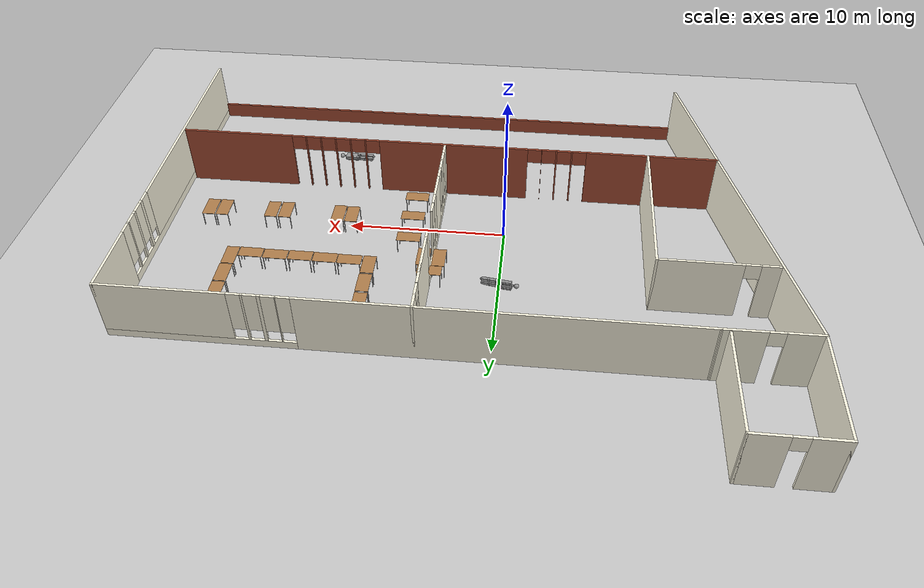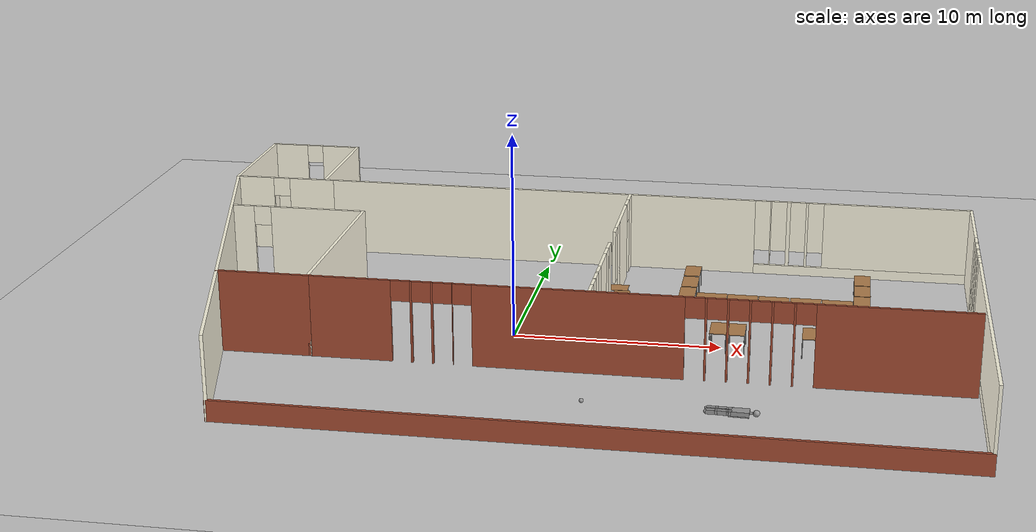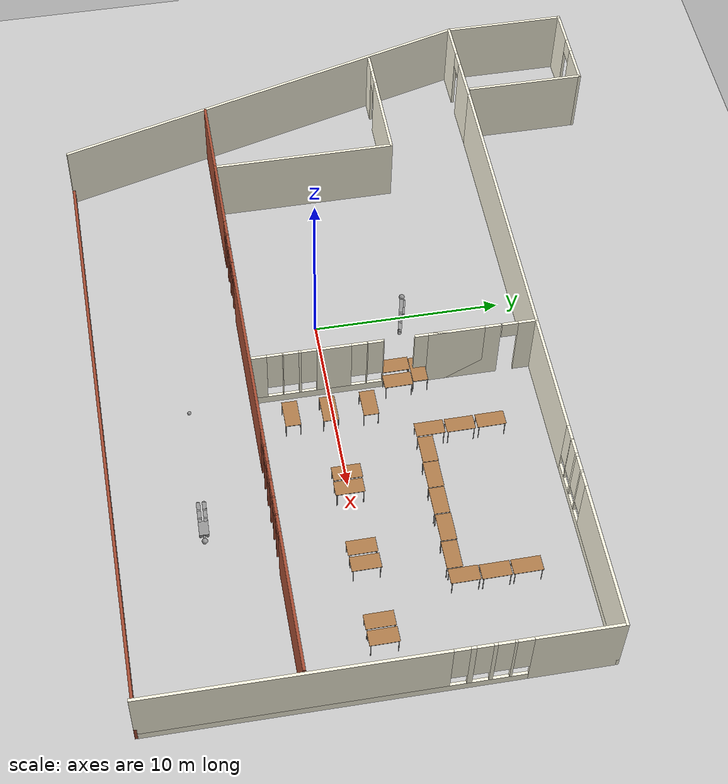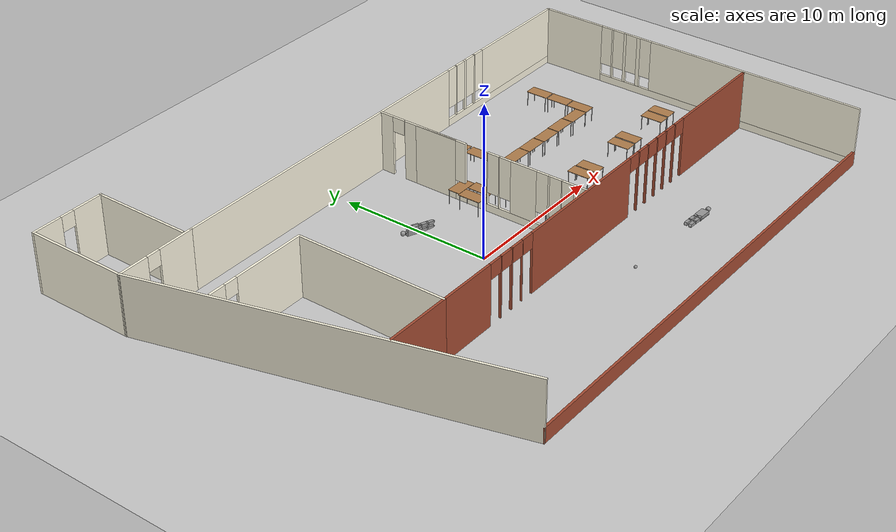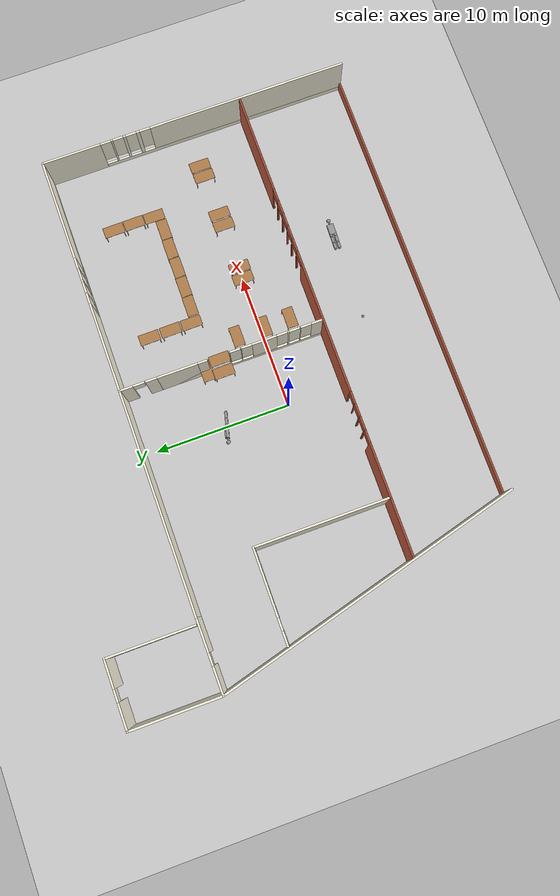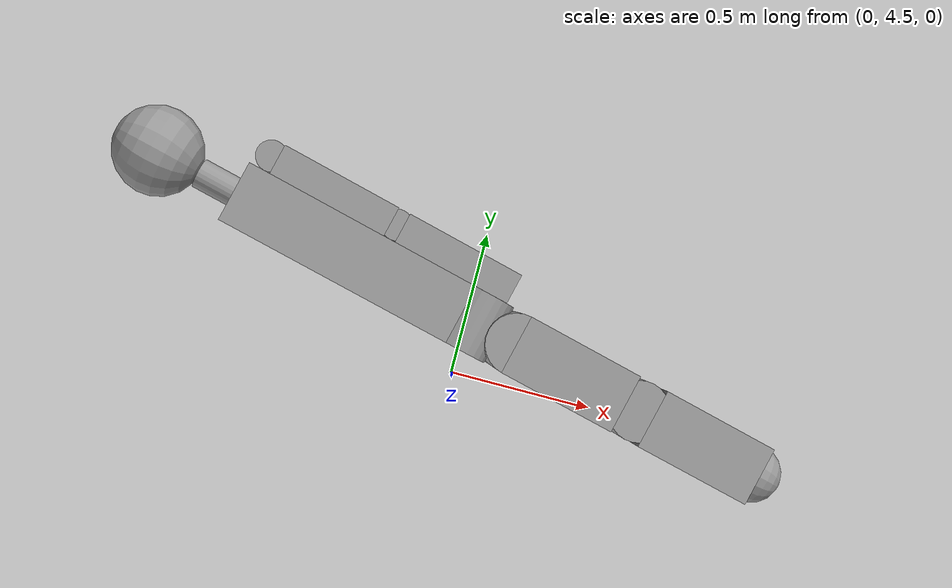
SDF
<sdf version="1.6">
 <world name="default">
  <light name="sun" type="directional">
   <pose>0 0 10 0 -0 0</pose>
   <diffuse>0.8 0.8 0.8 1</diffuse>
   <specular>0.2 0.2 0.2 1</specular>
   <attenuation>
    <range>1000</range>
    <constant>0.9</constant>
    <linear>0.01</linear>
    <quadratic>0.001</quadratic>
   </attenuation>
   <direction>-0.5 0.1 -0.9</direction>
  </light>
  <model name="ground_plane">
   <static>1</static>
   <link name="link">
    <collision name="collision">
     <geometry><plane><normal>0 0 1</normal><size>100 100</size></plane></geometry>
     <surface><friction><ode><mu>100</mu><mu2>50</mu2></ode></friction></surface>
    </collision>
    <visual name="visual">
     <cast_shadows>0</cast_shadows>
     <geometry><plane><normal>0 0 1</normal><size>100 100</size></plane></geometry>
     <material>
      <script><uri>file://media/materials/scripts/gazebo.material</uri><name>Gazebo/Grey</name></script>
     </material>
    </visual>
   </link>
  </model>
  <gravity>0 0 -9.8</gravity>
  <magnetic_field>6e-06 2.3e-05 -4.2e-05</magnetic_field>
  <atmosphere type="adiabatic"/>
  <physics name="default_physics" default="0" type="ode">
   <max_step_size>0.001</max_step_size>
   <real_time_factor>1</real_time_factor>
   <real_time_update_rate>1000</real_time_update_rate>
  </physics>
  <scene><ambient>0.4 0.4 0.4 1</ambient><background>0.7 0.7 0.7 1</background><shadows>1</shadows></scene>
  <spherical_coordinates>
   <surface_model>EARTH_WGS84</surface_model>
   <latitude_deg>0</latitude_deg>
   <longitude_deg>0</longitude_deg>
   <elevation>0</elevation>
   <heading_deg>0</heading_deg>
  </spherical_coordinates>
  <model name="myoffice">
   <pose>2.27474 2.6943 0.029402 0 -0 0</pose>
   <link name="Wall_0">
    <pose>2.68742 8.1604 0 0 -0 0</pose>
    <visual name="Wall_0_Visual_0">
     <pose>-5.55834 0 2 0 -0 0</pose>
     <geometry><box><size>22.8833 0.15 4</size></box></geometry>
     <material>
      <script><uri>file://media/materials/scripts/gazebo.material</uri><name>Gazebo/Grey</name></script>
      <ambient>1 0.980392 0.894118 1</ambient>
     </material>
     <meta><layer>0</layer></meta>
    </visual>
    <collision name="Wall_0_Collision_0">
     <geometry><box><size>22.8833 0.15 4</size></box></geometry>
     <pose>-5.55834 0 2 0 -0 0</pose>
    </collision>
    <visual name="Wall_0_Visual_1">
     <pose>11.4417 0 0.25 0 -0 0</pose>
     <geometry><box><size>11.1167 0.15 0.5</size></box></geometry>
     <material>
      <script><uri>file://media/materials/scripts/gazebo.material</uri><name>Gazebo/Grey</name></script>
      <ambient>1 0.980392 0.894118 1</ambient>
     </material>
     <meta><layer>0</layer></meta>
    </visual>
    <collision name="Wall_0_Collision_1">
     <geometry><box><size>11.1167 0.15 0.5</size></box></geometry>
     <pose>11.4417 0 0.25 0 -0 0</pose>
    </collision>
    <visual name="Wall_0_Visual_2">
     <pose>6.70786 0 2.25 0 -0 0</pose>
     <geometry><box><size>0.049085 0.15 3.5</size></box></geometry>
     <material>
      <script><uri>file://media/materials/scripts/gazebo.material</uri><name>Gazebo/Grey</name></script>
      <ambient>1 0.980392 0.894118 1</ambient>
     </material>
     <meta><layer>0</layer></meta>
    </visual>
    <collision name="Wall_0_Collision_2">
     <geometry><box><size>0.049085 0.15 3.5</size></box></geometry>
     <pose>6.70786 0 2.25 0 -0 0</pose>
    </collision>
    <visual name="Wall_0_Visual_3">
     <pose>7.6277 0 2.25 0 -0 0</pose>
     <geometry><box><size>0.190599 0.15 3.5</size></box></geometry>
     <material>
      <script><uri>file://media/materials/scripts/gazebo.material</uri><name>Gazebo/Grey</name></script>
      <ambient>1 0.980392 0.894118 1</ambient>
     </material>
     <meta><layer>0</layer></meta>
    </visual>
    <collision name="Wall_0_Collision_3">
     <geometry><box><size>0.190599 0.15 3.5</size></box></geometry>
     <pose>7.6277 0 2.25 0 -0 0</pose>
    </collision>
    <visual name="Wall_0_Visual_4">
     <pose>8.58292 0 2.25 0 -0 0</pose>
     <geometry><box><size>0.119842 0.15 3.5</size></box></geometry>
     <material>
      <script><uri>file://media/materials/scripts/gazebo.material</uri><name>Gazebo/Grey</name></script>
      <ambient>1 0.980392 0.894118 1</ambient>
     </material>
     <meta><layer>0</layer></meta>
    </visual>
    <collision name="Wall_0_Collision_4">
     <geometry><box><size>0.119842 0.15 3.5</size></box></geometry>
     <pose>8.58292 0 2.25 0 -0 0</pose>
    </collision>
    <visual name="Wall_0_Visual_5">
     <pose>13.2214 0 2.25 0 -0 0</pose>
     <geometry><box><size>7.55716 0.15 3.5</size></box></geometry>
     <material>
      <script><uri>file://media/materials/scripts/gazebo.material</uri><name>Gazebo/Grey</name></script>
      <ambient>1 0.980392 0.894118 1</ambient>
     </material>
     <meta><layer>0</layer></meta>
    </visual>
    <collision name="Wall_0_Collision_5">
     <geometry><box><size>7.55716 0.15 3.5</size></box></geometry>
     <pose>13.2214 0 2.25 0 -0 0</pose>
    </collision>
    <visual name="Wall_0_Visual_6">
     <pose>6.28331 0 2.65 0 -0 0</pose>
     <geometry><box><size>0.8 0.15 2.7</size></box></geometry>
     <material>
      <script><uri>file://media/materials/scripts/gazebo.material</uri><name>Gazebo/Grey</name></script>
      <ambient>1 0.980392 0.894118 1</ambient>
     </material>
     <meta><layer>0</layer></meta>
    </visual>
    <collision name="Wall_0_Collision_6">
     <geometry><box><size>0.8 0.15 2.7</size></box></geometry>
     <pose>6.28331 0 2.65 0 -0 0</pose>
    </collision>
    <visual name="Wall_0_Visual_7">
     <pose>7.1324 0 2.65 0 -0 0</pose>
     <geometry><box><size>0.8 0.15 2.7</size></box></geometry>
     <material>
      <script><uri>file://media/materials/scripts/gazebo.material</uri><name>Gazebo/Grey</name></script>
      <ambient>1 0.980392 0.894118 1</ambient>
     </material>
     <meta><layer>0</layer></meta>
    </visual>
    <collision name="Wall_0_Collision_7">
     <geometry><box><size>0.8 0.15 2.7</size></box></geometry>
     <pose>7.1324 0 2.65 0 -0 0</pose>
    </collision>
    <visual name="Wall_0_Visual_8">
     <pose>8.123 0 2.65 0 -0 0</pose>
     <geometry><box><size>0.8 0.15 2.7</size></box></geometry>
     <material>
      <script><uri>file://media/materials/scripts/gazebo.material</uri><name>Gazebo/Grey</name></script>
      <ambient>1 0.980392 0.894118 1</ambient>
     </material>
     <meta><layer>0</layer></meta>
    </visual>
    <collision name="Wall_0_Collision_8">
     <geometry><box><size>0.8 0.15 2.7</size></box></geometry>
     <pose>8.123 0 2.65 0 -0 0</pose>
    </collision>
    <visual name="Wall_0_Visual_9">
     <pose>9.04284 0 2.65 0 -0 0</pose>
     <geometry><box><size>0.8 0.15 2.7</size></box></geometry>
     <material>
      <script><uri>file://media/materials/scripts/gazebo.material</uri><name>Gazebo/Grey</name></script>
      <ambient>1 0.980392 0.894118 1</ambient>
     </material>
     <meta><layer>0</layer></meta>
    </visual>
    <collision name="Wall_0_Collision_9">
     <geometry><box><size>0.8 0.15 2.7</size></box></geometry>
     <pose>9.04284 0 2.65 0 -0 0</pose>
    </collision>
   </link>
   <link name="Wall_1">
    <pose>19.6124 -3.2646 0 0 0 -1.5708</pose>
    <visual name="Wall_1_Visual_0">
     <pose>-9.29214 0 2 0 -0 0</pose>
     <geometry><box><size>4.41572 0.15 4</size></box></geometry>
     <material>
      <script><uri>file://media/materials/scripts/gazebo.material</uri><name>Gazebo/Grey</name></script>
      <ambient>1 0.980392 0.894118 1</ambient>
     </material>
     <meta><layer>0</layer></meta>
    </visual>
    <collision name="Wall_1_Collision_0">
     <geometry><box><size>4.41572 0.15 4</size></box></geometry>
     <pose>-9.29214 0 2 0 -0 0</pose>
    </collision>
    <visual name="Wall_1_Visual_1">
     <pose>2.20786 0 0.25 0 -0 0</pose>
     <geometry><box><size>18.5843 0.15 0.5</size></box></geometry>
     <material>
      <script><uri>file://media/materials/scripts/gazebo.material</uri><name>Gazebo/Grey</name></script>
      <ambient>1 0.980392 0.894118 1</ambient>
     </material>
     <meta><layer>0</layer></meta>
    </visual>
    <collision name="Wall_1_Collision_1">
     <geometry><box><size>18.5843 0.15 0.5</size></box></geometry>
     <pose>2.20786 0 0.25 0 -0 0</pose>
    </collision>
    <visual name="Wall_1_Visual_2">
     <pose>-6.22436 0 2.25 0 -0 0</pose>
     <geometry><box><size>0.119842 0.15 3.5</size></box></geometry>
     <material>
      <script><uri>file://media/materials/scripts/gazebo.material</uri><name>Gazebo/Grey</name></script>
      <ambient>1 0.980392 0.894118 1</ambient>
     </material>
     <meta><layer>0</layer></meta>
    </visual>
    <collision name="Wall_1_Collision_2">
     <geometry><box><size>0.119842 0.15 3.5</size></box></geometry>
     <pose>-6.22436 0 2.25 0 -0 0</pose>
    </collision>
    <visual name="Wall_1_Visual_3">
     <pose>-5.26914 0 2.25 0 -0 0</pose>
     <geometry><box><size>0.190599 0.15 3.5</size></box></geometry>
     <material>
      <script><uri>file://media/materials/scripts/gazebo.material</uri><name>Gazebo/Grey</name></script>
      <ambient>1 0.980392 0.894118 1</ambient>
     </material>
     <meta><layer>0</layer></meta>
    </visual>
    <collision name="Wall_1_Collision_3">
     <geometry><box><size>0.190599 0.15 3.5</size></box></geometry>
     <pose>-5.26914 0 2.25 0 -0 0</pose>
    </collision>
    <visual name="Wall_1_Visual_4">
     <pose>-4.24316 0 2.25 0 -0 0</pose>
     <geometry><box><size>0.261356 0.15 3.5</size></box></geometry>
     <material>
      <script><uri>file://media/materials/scripts/gazebo.material</uri><name>Gazebo/Grey</name></script>
      <ambient>1 0.980392 0.894118 1</ambient>
     </material>
     <meta><layer>0</layer></meta>
    </visual>
    <collision name="Wall_1_Collision_4">
     <geometry><box><size>0.261356 0.15 3.5</size></box></geometry>
     <pose>-4.24316 0 2.25 0 -0 0</pose>
    </collision>
    <visual name="Wall_1_Visual_5">
     <pose>4.09376 0 2.25 0 -0 0</pose>
     <geometry><box><size>14.8125 0.15 3.5</size></box></geometry>
     <material>
      <script><uri>file://media/materials/scripts/gazebo.material</uri><name>Gazebo/Grey</name></script>
      <ambient>1 0.980392 0.894118 1</ambient>
     </material>
     <meta><layer>0</layer></meta>
    </visual>
    <collision name="Wall_1_Collision_5">
     <geometry><box><size>14.8125 0.15 3.5</size></box></geometry>
     <pose>4.09376 0 2.25 0 -0 0</pose>
    </collision>
    <visual name="Wall_1_Visual_6">
     <pose>-6.68428 0 2.65 0 -0 0</pose>
     <geometry><box><size>0.8 0.15 2.7</size></box></geometry>
     <material>
      <script><uri>file://media/materials/scripts/gazebo.material</uri><name>Gazebo/Grey</name></script>
      <ambient>1 0.980392 0.894118 1</ambient>
     </material>
     <meta><layer>0</layer></meta>
    </visual>
    <collision name="Wall_1_Collision_6">
     <geometry><box><size>0.8 0.15 2.7</size></box></geometry>
     <pose>-6.68428 0 2.65 0 -0 0</pose>
    </collision>
    <visual name="Wall_1_Visual_7">
     <pose>-5.76444 0 2.65 0 -0 0</pose>
     <geometry><box><size>0.8 0.15 2.7</size></box></geometry>
     <material>
      <script><uri>file://media/materials/scripts/gazebo.material</uri><name>Gazebo/Grey</name></script>
      <ambient>1 0.980392 0.894118 1</ambient>
     </material>
     <meta><layer>0</layer></meta>
    </visual>
    <collision name="Wall_1_Collision_7">
     <geometry><box><size>0.8 0.15 2.7</size></box></geometry>
     <pose>-5.76444 0 2.65 0 -0 0</pose>
    </collision>
    <visual name="Wall_1_Visual_8">
     <pose>-4.77384 0 2.65 0 -0 0</pose>
     <geometry><box><size>0.8 0.15 2.7</size></box></geometry>
     <material>
      <script><uri>file://media/materials/scripts/gazebo.material</uri><name>Gazebo/Grey</name></script>
      <ambient>1 0.980392 0.894118 1</ambient>
     </material>
     <meta><layer>0</layer></meta>
    </visual>
    <collision name="Wall_1_Collision_8">
     <geometry><box><size>0.8 0.15 2.7</size></box></geometry>
     <pose>-4.77384 0 2.65 0 -0 0</pose>
    </collision>
    <visual name="Wall_1_Visual_9">
     <pose>-3.71248 0 2.65 0 -0 0</pose>
     <geometry><box><size>0.8 0.15 2.7</size></box></geometry>
     <material>
      <script><uri>file://media/materials/scripts/gazebo.material</uri><name>Gazebo/Grey</name></script>
      <ambient>1 0.980392 0.894118 1</ambient>
     </material>
     <meta><layer>0</layer></meta>
    </visual>
    <collision name="Wall_1_Collision_9">
     <geometry><box><size>0.8 0.15 2.7</size></box></geometry>
     <pose>-3.71248 0 2.65 0 -0 0</pose>
    </collision>
   </link>
   <link name="Wall_11">
    <pose>-14.6336 3.0664 0 0 -0 0</pose>
    <visual name="Wall_11_Visual_0">
     <pose>-2.94452 0 2 0 -0 0</pose>
     <geometry><box><size>1.11096 0.15 4</size></box></geometry>
     <material>
      <script><uri>file://media/materials/scripts/gazebo.material</uri><name>Gazebo/Grey</name></script>
      <ambient>1 0.980392 0.894118 1</ambient>
     </material>
     <meta><layer>0</layer></meta>
    </visual>
    <collision name="Wall_11_Collision_0">
     <geometry><box><size>1.11096 0.15 4</size></box></geometry>
     <pose>-2.94452 0 2 0 -0 0</pose>
    </collision>
    <visual name="Wall_11_Visual_1">
     <pose>1.00548 0 2 0 -0 0</pose>
     <geometry><box><size>4.98904 0.15 4</size></box></geometry>
     <material>
      <script><uri>file://media/materials/scripts/gazebo.material</uri><name>Gazebo/Grey</name></script>
      <ambient>1 0.980392 0.894118 1</ambient>
     </material>
     <meta><layer>0</layer></meta>
    </visual>
    <collision name="Wall_11_Collision_1">
     <geometry><box><size>4.98904 0.15 4</size></box></geometry>
     <pose>1.00548 0 2 0 -0 0</pose>
    </collision>
    <visual name="Wall_11_Visual_2">
     <pose>-1.93904 0 3.5 0 -0 0</pose>
     <geometry><box><size>0.9 0.15 1</size></box></geometry>
     <material>
      <script><uri>file://media/materials/scripts/gazebo.material</uri><name>Gazebo/Grey</name></script>
      <ambient>1 0.980392 0.894118 1</ambient>
     </material>
     <meta><layer>0</layer></meta>
    </visual>
    <collision name="Wall_11_Collision_2">
     <geometry><box><size>0.9 0.15 1</size></box></geometry>
     <pose>-1.93904 0 3.5 0 -0 0</pose>
    </collision>
   </link>
   <link name="Wall_12">
    <collision name="Wall_12_Collision">
     <geometry><box><size>10 0.15 4</size></box></geometry>
     <pose>0 0 2 0 -0 0</pose>
    </collision>
    <visual name="Wall_12_Visual">
     <pose>0 0 2 0 -0 0</pose>
     <geometry><box><size>10 0.15 4</size></box></geometry>
     <material>
      <script><uri>file://media/materials/scripts/gazebo.material</uri><name>Gazebo/Grey</name></script>
      <ambient>1 0.980392 0.894118 1</ambient>
     </material>
     <meta><layer>0</layer></meta>
    </visual>
    <pose>-11.2086 -1.8586 0 0 0 -1.5708</pose>
   </link>
   <link name="Wall_13">
    <collision name="Wall_13_Collision">
     <geometry><box><size>4.5 0.15 4</size></box></geometry>
     <pose>0 0 2 0 -0 0</pose>
    </collision>
    <visual name="Wall_13_Visual">
     <pose>0 0 2 0 -0 0</pose>
     <geometry><box><size>4.5 0.15 4</size></box></geometry>
     <material>
      <script><uri>file://media/materials/scripts/gazebo.material</uri><name>Gazebo/Bricks</name></script>
      <ambient>1 0.980392 0.894118 1</ambient>
     </material>
     <meta><layer>0</layer></meta>
    </visual>
    <pose>-13.3836 -6.7836 0 0 -0 3.14159</pose>
   </link>
   <link name="Wall_15">
    <pose>4.09142 -6.7836 0 0 -0 0</pose>
    <visual name="Wall_15_Visual_0">
     <pose>-13.3623 0 2 0 -0 0</pose>
     <geometry><box><size>4.02537 0.15 4</size></box></geometry>
     <material>
      <script><uri>file://media/materials/scripts/gazebo.material</uri><name>Gazebo/Bricks</name></script>
      <ambient>1 0.980392 0.894118 1</ambient>
     </material>
     <meta><layer>0</layer></meta>
    </visual>
    <collision name="Wall_15_Collision_0">
     <geometry><box><size>4.02537 0.15 4</size></box></geometry>
     <pose>-13.3623 0 2 0 -0 0</pose>
    </collision>
    <visual name="Wall_15_Visual_1">
     <pose>-10.4043 0 2 0 -0 0</pose>
     <geometry><box><size>0.090664 0.15 4</size></box></geometry>
     <material>
      <script><uri>file://media/materials/scripts/gazebo.material</uri><name>Gazebo/Bricks</name></script>
      <ambient>1 0.980392 0.894118 1</ambient>
     </material>
     <meta><layer>0</layer></meta>
    </visual>
    <collision name="Wall_15_Collision_1">
     <geometry><box><size>0.090664 0.15 4</size></box></geometry>
     <pose>-10.4043 0 2 0 -0 0</pose>
    </collision>
    <visual name="Wall_15_Visual_2">
     <pose>-9.4137 0 2 0 -0 0</pose>
     <geometry><box><size>0.090534 0.15 4</size></box></geometry>
     <material>
      <script><uri>file://media/materials/scripts/gazebo.material</uri><name>Gazebo/Bricks</name></script>
      <ambient>1 0.980392 0.894118 1</ambient>
     </material>
     <meta><layer>0</layer></meta>
    </visual>
    <collision name="Wall_15_Collision_2">
     <geometry><box><size>0.090534 0.15 4</size></box></geometry>
     <pose>-9.4137 0 2 0 -0 0</pose>
    </collision>
    <visual name="Wall_15_Visual_3">
     <pose>-8.45851 0 2 0 -0 0</pose>
     <geometry><box><size>0.019842 0.15 4</size></box></geometry>
     <material>
      <script><uri>file://media/materials/scripts/gazebo.material</uri><name>Gazebo/Bricks</name></script>
      <ambient>1 0.980392 0.894118 1</ambient>
     </material>
     <meta><layer>0</layer></meta>
    </visual>
    <collision name="Wall_15_Collision_3">
     <geometry><box><size>0.019842 0.15 4</size></box></geometry>
     <pose>-8.45851 0 2 0 -0 0</pose>
    </collision>
    <visual name="Wall_15_Visual_4">
     <pose>-2.65643 0 2 0 -0 0</pose>
     <geometry><box><size>9.78432 0.15 4</size></box></geometry>
     <material>
      <script><uri>file://media/materials/scripts/gazebo.material</uri><name>Gazebo/Bricks</name></script>
      <ambient>1 0.980392 0.894118 1</ambient>
     </material>
     <meta><layer>0</layer></meta>
    </visual>
    <collision name="Wall_15_Collision_4">
     <geometry><box><size>9.78432 0.15 4</size></box></geometry>
     <pose>-2.65643 0 2 0 -0 0</pose>
    </collision>
    <visual name="Wall_15_Visual_5">
     <pose>3.18107 0 2 0 -0 0</pose>
     <geometry><box><size>0.090681 0.15 4</size></box></geometry>
     <material>
      <script><uri>file://media/materials/scripts/gazebo.material</uri><name>Gazebo/Bricks</name></script>
      <ambient>1 0.980392 0.894118 1</ambient>
     </material>
     <meta><layer>0</layer></meta>
    </visual>
    <collision name="Wall_15_Collision_5">
     <geometry><box><size>0.090681 0.15 4</size></box></geometry>
     <pose>3.18107 0 2 0 -0 0</pose>
    </collision>
    <visual name="Wall_15_Visual_6">
     <pose>4.17167 0 2 0 -0 0</pose>
     <geometry><box><size>0.090516 0.15 4</size></box></geometry>
     <material>
      <script><uri>file://media/materials/scripts/gazebo.material</uri><name>Gazebo/Bricks</name></script>
      <ambient>1 0.980392 0.894118 1</ambient>
     </material>
     <meta><layer>0</layer></meta>
    </visual>
    <collision name="Wall_15_Collision_6">
     <geometry><box><size>0.090516 0.15 4</size></box></geometry>
     <pose>4.17167 0 2 0 -0 0</pose>
    </collision>
    <visual name="Wall_15_Visual_7">
     <pose>5.16222 0 2 0 -0 0</pose>
     <geometry><box><size>0.090599 0.15 4</size></box></geometry>
     <material>
      <script><uri>file://media/materials/scripts/gazebo.material</uri><name>Gazebo/Bricks</name></script>
      <ambient>1 0.980392 0.894118 1</ambient>
     </material>
     <meta><layer>0</layer></meta>
    </visual>
    <collision name="Wall_15_Collision_7">
     <geometry><box><size>0.090599 0.15 4</size></box></geometry>
     <pose>5.16222 0 2 0 -0 0</pose>
    </collision>
    <visual name="Wall_15_Visual_8">
     <pose>6.15282 0 2 0 -0 0</pose>
     <geometry><box><size>0.090599 0.15 4</size></box></geometry>
     <material>
      <script><uri>file://media/materials/scripts/gazebo.material</uri><name>Gazebo/Bricks</name></script>
      <ambient>1 0.980392 0.894118 1</ambient>
     </material>
     <meta><layer>0</layer></meta>
    </visual>
    <collision name="Wall_15_Collision_8">
     <geometry><box><size>0.090599 0.15 4</size></box></geometry>
     <pose>6.15282 0 2 0 -0 0</pose>
    </collision>
    <visual name="Wall_15_Visual_9">
     <pose>7.14342 0 2 0 -0 0</pose>
     <geometry><box><size>0.090599 0.15 4</size></box></geometry>
     <material>
      <script><uri>file://media/materials/scripts/gazebo.material</uri><name>Gazebo/Bricks</name></script>
      <ambient>1 0.980392 0.894118 1</ambient>
     </material>
     <meta><layer>0</layer></meta>
    </visual>
    <collision name="Wall_15_Collision_9">
     <geometry><box><size>0.090599 0.15 4</size></box></geometry>
     <pose>7.14342 0 2 0 -0 0</pose>
    </collision>
    <visual name="Wall_15_Visual_10">
     <pose>11.7319 0 2 0 -0 0</pose>
     <geometry><box><size>7.28628 0.15 4</size></box></geometry>
     <material>
      <script><uri>file://media/materials/scripts/gazebo.material</uri><name>Gazebo/Bricks</name></script>
      <ambient>1 0.980392 0.894118 1</ambient>
     </material>
     <meta><layer>0</layer></meta>
    </visual>
    <collision name="Wall_15_Collision_10">
     <geometry><box><size>7.28628 0.15 4</size></box></geometry>
     <pose>11.7319 0 2 0 -0 0</pose>
    </collision>
    <visual name="Wall_15_Visual_11">
     <pose>-10.8996 0 3.5 0 -0 0</pose>
     <geometry><box><size>0.9 0.15 1</size></box></geometry>
     <material>
      <script><uri>file://media/materials/scripts/gazebo.material</uri><name>Gazebo/Bricks</name></script>
      <ambient>1 0.980392 0.894118 1</ambient>
     </material>
     <meta><layer>0</layer></meta>
    </visual>
    <collision name="Wall_15_Collision_11">
     <geometry><box><size>0.9 0.15 1</size></box></geometry>
     <pose>-10.8996 0 3.5 0 -0 0</pose>
    </collision>
    <visual name="Wall_15_Visual_12">
     <pose>-9.90897 0 3.5 0 -0 0</pose>
     <geometry><box><size>0.9 0.15 1</size></box></geometry>
     <material>
      <script><uri>file://media/materials/scripts/gazebo.material</uri><name>Gazebo/Bricks</name></script>
      <ambient>1 0.980392 0.894118 1</ambient>
     </material>
     <meta><layer>0</layer></meta>
    </visual>
    <collision name="Wall_15_Collision_12">
     <geometry><box><size>0.9 0.15 1</size></box></geometry>
     <pose>-9.90897 0 3.5 0 -0 0</pose>
    </collision>
    <visual name="Wall_15_Visual_13">
     <pose>-8.91843 0 3.5 0 -0 0</pose>
     <geometry><box><size>0.9 0.15 1</size></box></geometry>
     <material>
      <script><uri>file://media/materials/scripts/gazebo.material</uri><name>Gazebo/Bricks</name></script>
      <ambient>1 0.980392 0.894118 1</ambient>
     </material>
     <meta><layer>0</layer></meta>
    </visual>
    <collision name="Wall_15_Collision_13">
     <geometry><box><size>0.9 0.15 1</size></box></geometry>
     <pose>-8.91843 0 3.5 0 -0 0</pose>
    </collision>
    <visual name="Wall_15_Visual_14">
     <pose>-7.99859 0 3.5 0 -0 0</pose>
     <geometry><box><size>0.9 0.15 1</size></box></geometry>
     <material>
      <script><uri>file://media/materials/scripts/gazebo.material</uri><name>Gazebo/Bricks</name></script>
      <ambient>1 0.980392 0.894118 1</ambient>
     </material>
     <meta><layer>0</layer></meta>
    </visual>
    <collision name="Wall_15_Collision_14">
     <geometry><box><size>0.9 0.15 1</size></box></geometry>
     <pose>-7.99859 0 3.5 0 -0 0</pose>
    </collision>
    <visual name="Wall_15_Visual_15">
     <pose>2.68573 0 3.5 0 -0 0</pose>
     <geometry><box><size>0.9 0.15 1</size></box></geometry>
     <material>
      <script><uri>file://media/materials/scripts/gazebo.material</uri><name>Gazebo/Bricks</name></script>
      <ambient>1 0.980392 0.894118 1</ambient>
     </material>
     <meta><layer>0</layer></meta>
    </visual>
    <collision name="Wall_15_Collision_15">
     <geometry><box><size>0.9 0.15 1</size></box></geometry>
     <pose>2.68573 0 3.5 0 -0 0</pose>
    </collision>
    <visual name="Wall_15_Visual_16">
     <pose>3.67641 0 3.5 0 -0 0</pose>
     <geometry><box><size>0.9 0.15 1</size></box></geometry>
     <material>
      <script><uri>file://media/materials/scripts/gazebo.material</uri><name>Gazebo/Bricks</name></script>
      <ambient>1 0.980392 0.894118 1</ambient>
     </material>
     <meta><layer>0</layer></meta>
    </visual>
    <collision name="Wall_15_Collision_16">
     <geometry><box><size>0.9 0.15 1</size></box></geometry>
     <pose>3.67641 0 3.5 0 -0 0</pose>
    </collision>
    <visual name="Wall_15_Visual_17">
     <pose>4.66692 0 3.5 0 -0 0</pose>
     <geometry><box><size>0.9 0.15 1</size></box></geometry>
     <material>
      <script><uri>file://media/materials/scripts/gazebo.material</uri><name>Gazebo/Bricks</name></script>
      <ambient>1 0.980392 0.894118 1</ambient>
     </material>
     <meta><layer>0</layer></meta>
    </visual>
    <collision name="Wall_15_Collision_17">
     <geometry><box><size>0.9 0.15 1</size></box></geometry>
     <pose>4.66692 0 3.5 0 -0 0</pose>
    </collision>
    <visual name="Wall_15_Visual_18">
     <pose>5.65752 0 3.5 0 -0 0</pose>
     <geometry><box><size>0.9 0.15 1</size></box></geometry>
     <material>
      <script><uri>file://media/materials/scripts/gazebo.material</uri><name>Gazebo/Bricks</name></script>
      <ambient>1 0.980392 0.894118 1</ambient>
     </material>
     <meta><layer>0</layer></meta>
    </visual>
    <collision name="Wall_15_Collision_18">
     <geometry><box><size>0.9 0.15 1</size></box></geometry>
     <pose>5.65752 0 3.5 0 -0 0</pose>
    </collision>
    <visual name="Wall_15_Visual_19">
     <pose>6.64812 0 3.5 0 -0 0</pose>
     <geometry><box><size>0.9 0.15 1</size></box></geometry>
     <material>
      <script><uri>file://media/materials/scripts/gazebo.material</uri><name>Gazebo/Bricks</name></script>
      <ambient>1 0.980392 0.894118 1</ambient>
     </material>
     <meta><layer>0</layer></meta>
    </visual>
    <collision name="Wall_15_Collision_19">
     <geometry><box><size>0.9 0.15 1</size></box></geometry>
     <pose>6.64812 0 3.5 0 -0 0</pose>
    </collision>
    <visual name="Wall_15_Visual_20">
     <pose>7.63872 0 3.5 0 -0 0</pose>
     <geometry><box><size>0.9 0.15 1</size></box></geometry>
     <material>
      <script><uri>file://media/materials/scripts/gazebo.material</uri><name>Gazebo/Bricks</name></script>
      <ambient>1 0.980392 0.894118 1</ambient>
     </material>
     <meta><layer>0</layer></meta>
    </visual>
    <collision name="Wall_15_Collision_20">
     <geometry><box><size>0.9 0.15 1</size></box></geometry>
     <pose>7.63872 0 3.5 0 -0 0</pose>
    </collision>
   </link>
   <link name="Wall_17">
    <pose>1.96542 0.7354 0 0 0 -1.5708</pose>
    <visual name="Wall_17_Visual_0">
     <pose>-6.97993 0 2 0 -0 0</pose>
     <geometry><box><size>1.04014 0.15 4</size></box></geometry>
     <material>
      <script><uri>file://media/materials/scripts/gazebo.material</uri><name>Gazebo/Grey</name></script>
      <ambient>1 0.980392 0.894118 1</ambient>
     </material>
     <meta><layer>0</layer></meta>
    </visual>
    <collision name="Wall_17_Collision_0">
     <geometry><box><size>1.04014 0.15 4</size></box></geometry>
     <pose>-6.97993 0 2 0 -0 0</pose>
    </collision>
    <visual name="Wall_17_Visual_1">
     <pose>-3.64988 0 2 0 -0 0</pose>
     <geometry><box><size>3.81997 0.15 4</size></box></geometry>
     <material>
      <script><uri>file://media/materials/scripts/gazebo.material</uri><name>Gazebo/Grey</name></script>
      <ambient>1 0.980392 0.894118 1</ambient>
     </material>
     <meta><layer>0</layer></meta>
    </visual>
    <collision name="Wall_17_Collision_1">
     <geometry><box><size>3.81997 0.15 4</size></box></geometry>
     <pose>-3.64988 0 2 0 -0 0</pose>
    </collision>
    <visual name="Wall_17_Visual_2">
     <pose>-3.22533 0 2 0 -0 0</pose>
     <geometry><box><size>2.97088 0.15 4</size></box></geometry>
     <material>
      <script><uri>file://media/materials/scripts/gazebo.material</uri><name>Gazebo/Grey</name></script>
      <ambient>1 0.980392 0.894118 1</ambient>
     </material>
     <meta><layer>0</layer></meta>
    </visual>
    <collision name="Wall_17_Collision_2">
     <geometry><box><size>2.97088 0.15 4</size></box></geometry>
     <pose>-3.22533 0 2 0 -0 0</pose>
    </collision>
    <visual name="Wall_17_Visual_3">
     <pose>2.88005 0 0.25 0 -0 0</pose>
     <geometry><box><size>9.23989 0.15 0.5</size></box></geometry>
     <material>
      <script><uri>file://media/materials/scripts/gazebo.material</uri><name>Gazebo/Grey</name></script>
      <ambient>1 0.980392 0.894118 1</ambient>
     </material>
     <meta><layer>0</layer></meta>
    </visual>
    <collision name="Wall_17_Collision_3">
     <geometry><box><size>9.23989 0.15 0.5</size></box></geometry>
     <pose>2.88005 0 0.25 0 -0 0</pose>
    </collision>
    <visual name="Wall_17_Visual_4">
     <pose>2.88005 0 0.25 0 -0 0</pose>
     <geometry><box><size>9.23989 0.15 0.5</size></box></geometry>
     <material>
      <script><uri>file://media/materials/scripts/gazebo.material</uri><name>Gazebo/Grey</name></script>
      <ambient>1 0.980392 0.894118 1</ambient>
     </material>
     <meta><layer>0</layer></meta>
    </visual>
    <collision name="Wall_17_Collision_4">
     <geometry><box><size>9.23989 0.15 0.5</size></box></geometry>
     <pose>2.88005 0 0.25 0 -0 0</pose>
    </collision>
    <visual name="Wall_17_Visual_5">
     <pose>0.570547 0 2.25 0 -0 0</pose>
     <geometry><box><size>0.049085 0.15 3.5</size></box></geometry>
     <material>
      <script><uri>file://media/materials/scripts/gazebo.material</uri><name>Gazebo/Grey</name></script>
      <ambient>1 0.980392 0.894118 1</ambient>
     </material>
     <meta><layer>0</layer></meta>
    </visual>
    <collision name="Wall_17_Collision_5">
     <geometry><box><size>0.049085 0.15 3.5</size></box></geometry>
     <pose>0.570547 0 2.25 0 -0 0</pose>
    </collision>
    <visual name="Wall_17_Visual_6">
     <pose>1.41963 0 2.25 0 -0 0</pose>
     <geometry><box><size>0.049085 0.15 3.5</size></box></geometry>
     <material>
      <script><uri>file://media/materials/scripts/gazebo.material</uri><name>Gazebo/Grey</name></script>
      <ambient>1 0.980392 0.894118 1</ambient>
     </material>
     <meta><layer>0</layer></meta>
    </visual>
    <collision name="Wall_17_Collision_6">
     <geometry><box><size>0.049085 0.15 3.5</size></box></geometry>
     <pose>1.41963 0 2.25 0 -0 0</pose>
    </collision>
    <visual name="Wall_17_Visual_7">
     <pose>3.15318 0 2.25 0 -0 0</pose>
     <geometry><box><size>1.81801 0.15 3.5</size></box></geometry>
     <material>
      <script><uri>file://media/materials/scripts/gazebo.material</uri><name>Gazebo/Grey</name></script>
      <ambient>1 0.980392 0.894118 1</ambient>
     </material>
     <meta><layer>0</layer></meta>
    </visual>
    <collision name="Wall_17_Collision_7">
     <geometry><box><size>1.81801 0.15 3.5</size></box></geometry>
     <pose>3.15318 0 2.25 0 -0 0</pose>
    </collision>
    <visual name="Wall_17_Visual_8">
     <pose>4.92211 0 2.25 0 -0 0</pose>
     <geometry><box><size>0.119842 0.15 3.5</size></box></geometry>
     <material>
      <script><uri>file://media/materials/scripts/gazebo.material</uri><name>Gazebo/Grey</name></script>
      <ambient>1 0.980392 0.894118 1</ambient>
     </material>
     <meta><layer>0</layer></meta>
    </visual>
    <collision name="Wall_17_Collision_8">
     <geometry><box><size>0.119842 0.15 3.5</size></box></geometry>
     <pose>4.92211 0 2.25 0 -0 0</pose>
    </collision>
    <visual name="Wall_17_Visual_9">
     <pose>5.80657 0 2.25 0 -0 0</pose>
     <geometry><box><size>0.049085 0.15 3.5</size></box></geometry>
     <material>
      <script><uri>file://media/materials/scripts/gazebo.material</uri><name>Gazebo/Grey</name></script>
      <ambient>1 0.980392 0.894118 1</ambient>
     </material>
     <meta><layer>0</layer></meta>
    </visual>
    <collision name="Wall_17_Collision_9">
     <geometry><box><size>0.049085 0.15 3.5</size></box></geometry>
     <pose>5.80657 0 2.25 0 -0 0</pose>
    </collision>
    <visual name="Wall_17_Visual_10">
     <pose>7.06556 0 2.25 0 -0 0</pose>
     <geometry><box><size>0.868888 0.15 3.5</size></box></geometry>
     <material>
      <script><uri>file://media/materials/scripts/gazebo.material</uri><name>Gazebo/Grey</name></script>
      <ambient>1 0.980392 0.894118 1</ambient>
     </material>
     <meta><layer>0</layer></meta>
    </visual>
    <collision name="Wall_17_Collision_10">
     <geometry><box><size>0.868888 0.15 3.5</size></box></geometry>
     <pose>7.06556 0 2.25 0 -0 0</pose>
    </collision>
    <visual name="Wall_17_Visual_11">
     <pose>0.570547 0 2.25 0 -0 0</pose>
     <geometry><box><size>0.049085 0.15 3.5</size></box></geometry>
     <material>
      <script><uri>file://media/materials/scripts/gazebo.material</uri><name>Gazebo/Grey</name></script>
      <ambient>1 0.980392 0.894118 1</ambient>
     </material>
     <meta><layer>0</layer></meta>
    </visual>
    <collision name="Wall_17_Collision_11">
     <geometry><box><size>0.049085 0.15 3.5</size></box></geometry>
     <pose>0.570547 0 2.25 0 -0 0</pose>
    </collision>
    <visual name="Wall_17_Visual_12">
     <pose>1.41963 0 2.25 0 -0 0</pose>
     <geometry><box><size>0.049085 0.15 3.5</size></box></geometry>
     <material>
      <script><uri>file://media/materials/scripts/gazebo.material</uri><name>Gazebo/Grey</name></script>
      <ambient>1 0.980392 0.894118 1</ambient>
     </material>
     <meta><layer>0</layer></meta>
    </visual>
    <collision name="Wall_17_Collision_12">
     <geometry><box><size>0.049085 0.15 3.5</size></box></geometry>
     <pose>1.41963 0 2.25 0 -0 0</pose>
    </collision>
    <visual name="Wall_17_Visual_13">
     <pose>3.15318 0 2.25 0 -0 0</pose>
     <geometry><box><size>1.81801 0.15 3.5</size></box></geometry>
     <material>
      <script><uri>file://media/materials/scripts/gazebo.material</uri><name>Gazebo/Grey</name></script>
      <ambient>1 0.980392 0.894118 1</ambient>
     </material>
     <meta><layer>0</layer></meta>
    </visual>
    <collision name="Wall_17_Collision_13">
     <geometry><box><size>1.81801 0.15 3.5</size></box></geometry>
     <pose>3.15318 0 2.25 0 -0 0</pose>
    </collision>
    <visual name="Wall_17_Visual_14">
     <pose>4.92211 0 2.25 0 -0 0</pose>
     <geometry><box><size>0.119842 0.15 3.5</size></box></geometry>
     <material>
      <script><uri>file://media/materials/scripts/gazebo.material</uri><name>Gazebo/Grey</name></script>
      <ambient>1 0.980392 0.894118 1</ambient>
     </material>
     <meta><layer>0</layer></meta>
    </visual>
    <collision name="Wall_17_Collision_14">
     <geometry><box><size>0.119842 0.15 3.5</size></box></geometry>
     <pose>4.92211 0 2.25 0 -0 0</pose>
    </collision>
    <visual name="Wall_17_Visual_15">
     <pose>5.80657 0 2.25 0 -0 0</pose>
     <geometry><box><size>0.049085 0.15 3.5</size></box></geometry>
     <material>
      <script><uri>file://media/materials/scripts/gazebo.material</uri><name>Gazebo/Grey</name></script>
      <ambient>1 0.980392 0.894118 1</ambient>
     </material>
     <meta><layer>0</layer></meta>
    </visual>
    <collision name="Wall_17_Collision_15">
     <geometry><box><size>0.049085 0.15 3.5</size></box></geometry>
     <pose>5.80657 0 2.25 0 -0 0</pose>
    </collision>
    <visual name="Wall_17_Visual_16">
     <pose>7.06556 0 2.25 0 -0 0</pose>
     <geometry><box><size>0.868888 0.15 3.5</size></box></geometry>
     <material>
      <script><uri>file://media/materials/scripts/gazebo.material</uri><name>Gazebo/Grey</name></script>
      <ambient>1 0.980392 0.894118 1</ambient>
     </material>
     <meta><layer>0</layer></meta>
    </visual>
    <collision name="Wall_17_Collision_16">
     <geometry><box><size>0.868888 0.15 3.5</size></box></geometry>
     <pose>7.06556 0 2.25 0 -0 0</pose>
    </collision>
    <visual name="Wall_17_Visual_17">
     <pose>-1.38592 0 2.65 0 -0 0</pose>
     <geometry><box><size>0.707939 0.15 2.7</size></box></geometry>
     <material>
      <script><uri>file://media/materials/scripts/gazebo.material</uri><name>Gazebo/Grey</name></script>
      <ambient>1 0.980392 0.894118 1</ambient>
     </material>
     <meta><layer>0</layer></meta>
    </visual>
    <collision name="Wall_17_Collision_17">
     <geometry><box><size>0.707939 0.15 2.7</size></box></geometry>
     <pose>-1.38592 0 2.65 0 -0 0</pose>
    </collision>
    <visual name="Wall_17_Visual_18">
     <pose>-1.38592 0 2.65 0 -0 0</pose>
     <geometry><box><size>0.707939 0.15 2.7</size></box></geometry>
     <material>
      <script><uri>file://media/materials/scripts/gazebo.material</uri><name>Gazebo/Grey</name></script>
      <ambient>1 0.980392 0.894118 1</ambient>
     </material>
     <meta><layer>0</layer></meta>
    </visual>
    <collision name="Wall_17_Collision_18">
     <geometry><box><size>0.707939 0.15 2.7</size></box></geometry>
     <pose>-1.38592 0 2.65 0 -0 0</pose>
    </collision>
    <visual name="Wall_17_Visual_19">
     <pose>0.99509 0 2.65 0 -0 0</pose>
     <geometry><box><size>0.8 0.15 2.7</size></box></geometry>
     <material>
      <script><uri>file://media/materials/scripts/gazebo.material</uri><name>Gazebo/Grey</name></script>
      <ambient>1 0.980392 0.894118 1</ambient>
     </material>
     <meta><layer>0</layer></meta>
    </visual>
    <collision name="Wall_17_Collision_19">
     <geometry><box><size>0.8 0.15 2.7</size></box></geometry>
     <pose>0.99509 0 2.65 0 -0 0</pose>
    </collision>
    <visual name="Wall_17_Visual_20">
     <pose>1.84417 0 2.65 0 -0 0</pose>
     <geometry><box><size>0.8 0.15 2.7</size></box></geometry>
     <material>
      <script><uri>file://media/materials/scripts/gazebo.material</uri><name>Gazebo/Grey</name></script>
      <ambient>1 0.980392 0.894118 1</ambient>
     </material>
     <meta><layer>0</layer></meta>
    </visual>
    <collision name="Wall_17_Collision_20">
     <geometry><box><size>0.8 0.15 2.7</size></box></geometry>
     <pose>1.84417 0 2.65 0 -0 0</pose>
    </collision>
    <visual name="Wall_17_Visual_21">
     <pose>4.46219 0 2.65 0 -0 0</pose>
     <geometry><box><size>0.8 0.15 2.7</size></box></geometry>
     <material>
      <script><uri>file://media/materials/scripts/gazebo.material</uri><name>Gazebo/Grey</name></script>
      <ambient>1 0.980392 0.894118 1</ambient>
     </material>
     <meta><layer>0</layer></meta>
    </visual>
    <collision name="Wall_17_Collision_21">
     <geometry><box><size>0.8 0.15 2.7</size></box></geometry>
     <pose>4.46219 0 2.65 0 -0 0</pose>
    </collision>
    <visual name="Wall_17_Visual_22">
     <pose>5.38203 0 2.65 0 -0 0</pose>
     <geometry><box><size>0.8 0.15 2.7</size></box></geometry>
     <material>
      <script><uri>file://media/materials/scripts/gazebo.material</uri><name>Gazebo/Grey</name></script>
      <ambient>1 0.980392 0.894118 1</ambient>
     </material>
     <meta><layer>0</layer></meta>
    </visual>
    <collision name="Wall_17_Collision_22">
     <geometry><box><size>0.8 0.15 2.7</size></box></geometry>
     <pose>5.38203 0 2.65 0 -0 0</pose>
    </collision>
    <visual name="Wall_17_Visual_23">
     <pose>6.23111 0 2.65 0 -0 0</pose>
     <geometry><box><size>0.8 0.15 2.7</size></box></geometry>
     <material>
      <script><uri>file://media/materials/scripts/gazebo.material</uri><name>Gazebo/Grey</name></script>
      <ambient>1 0.980392 0.894118 1</ambient>
     </material>
     <meta><layer>0</layer></meta>
    </visual>
    <collision name="Wall_17_Collision_23">
     <geometry><box><size>0.8 0.15 2.7</size></box></geometry>
     <pose>6.23111 0 2.65 0 -0 0</pose>
    </collision>
    <visual name="Wall_17_Visual_24">
     <pose>0.99509 0 2.65 0 -0 0</pose>
     <geometry><box><size>0.8 0.15 2.7</size></box></geometry>
     <material>
      <script><uri>file://media/materials/scripts/gazebo.material</uri><name>Gazebo/Grey</name></script>
      <ambient>1 0.980392 0.894118 1</ambient>
     </material>
     <meta><layer>0</layer></meta>
    </visual>
    <collision name="Wall_17_Collision_24">
     <geometry><box><size>0.8 0.15 2.7</size></box></geometry>
     <pose>0.99509 0 2.65 0 -0 0</pose>
    </collision>
    <visual name="Wall_17_Visual_25">
     <pose>1.84417 0 2.65 0 -0 0</pose>
     <geometry><box><size>0.8 0.15 2.7</size></box></geometry>
     <material>
      <script><uri>file://media/materials/scripts/gazebo.material</uri><name>Gazebo/Grey</name></script>
      <ambient>1 0.980392 0.894118 1</ambient>
     </material>
     <meta><layer>0</layer></meta>
    </visual>
    <collision name="Wall_17_Collision_25">
     <geometry><box><size>0.8 0.15 2.7</size></box></geometry>
     <pose>1.84417 0 2.65 0 -0 0</pose>
    </collision>
    <visual name="Wall_17_Visual_26">
     <pose>4.46219 0 2.65 0 -0 0</pose>
     <geometry><box><size>0.8 0.15 2.7</size></box></geometry>
     <material>
      <script><uri>file://media/materials/scripts/gazebo.material</uri><name>Gazebo/Grey</name></script>
      <ambient>1 0.980392 0.894118 1</ambient>
     </material>
     <meta><layer>0</layer></meta>
    </visual>
    <collision name="Wall_17_Collision_26">
     <geometry><box><size>0.8 0.15 2.7</size></box></geometry>
     <pose>4.46219 0 2.65 0 -0 0</pose>
    </collision>
    <visual name="Wall_17_Visual_27">
     <pose>5.38203 0 2.65 0 -0 0</pose>
     <geometry><box><size>0.8 0.15 2.7</size></box></geometry>
     <material>
      <script><uri>file://media/materials/scripts/gazebo.material</uri><name>Gazebo/Grey</name></script>
      <ambient>1 0.980392 0.894118 1</ambient>
     </material>
     <meta><layer>0</layer></meta>
    </visual>
    <collision name="Wall_17_Collision_27">
     <geometry><box><size>0.8 0.15 2.7</size></box></geometry>
     <pose>5.38203 0 2.65 0 -0 0</pose>
    </collision>
    <visual name="Wall_17_Visual_28">
     <pose>6.23111 0 2.65 0 -0 0</pose>
     <geometry><box><size>0.8 0.15 2.7</size></box></geometry>
     <material>
      <script><uri>file://media/materials/scripts/gazebo.material</uri><name>Gazebo/Grey</name></script>
      <ambient>1 0.980392 0.894118 1</ambient>
     </material>
     <meta><layer>0</layer></meta>
    </visual>
    <collision name="Wall_17_Collision_28">
     <geometry><box><size>0.8 0.15 2.7</size></box></geometry>
     <pose>6.23111 0 2.65 0 -0 0</pose>
    </collision>
    <visual name="Wall_17_Visual_29">
     <pose>-6.03532 0 3.5 0 -0 0</pose>
     <geometry><box><size>0.849085 0.15 1</size></box></geometry>
     <material>
      <script><uri>file://media/materials/scripts/gazebo.material</uri><name>Gazebo/Grey</name></script>
      <ambient>1 0.980392 0.894118 1</ambient>
     </material>
     <meta><layer>0</layer></meta>
    </visual>
    <collision name="Wall_17_Collision_29">
     <geometry><box><size>0.849085 0.15 1</size></box></geometry>
     <pose>-6.03532 0 3.5 0 -0 0</pose>
    </collision>
   </link>
   <link name="Wall_2">
    <collision name="Wall_2_Collision">
     <geometry><box><size>33.25 0.15 1</size></box></geometry>
     <pose>0 0 0.5 0 -0 0</pose>
    </collision>
    <visual name="Wall_2_Visual">
     <pose>0 0 0.5 0 -0 0</pose>
     <geometry><box><size>33.25 0.15 1</size></box></geometry>
     <material>
      <script><uri>file://media/materials/scripts/gazebo.material</uri><name>Gazebo/Bricks</name></script>
      <ambient>1 0.980392 0.894118 1</ambient>
     </material>
     <meta><layer>0</layer></meta>
    </visual>
    <pose>3.06242 -14.6896 0 0 -0 3.14159</pose>
   </link>
   <link name="Wall_21">
    <pose>-16.9166 8.1334 0 0 0 -3.13151</pose>
    <visual name="Wall_21_Visual_0">
     <pose>-1.49066 0 2 0 -0 0</pose>
     <geometry><box><size>2.52694 0.15 4</size></box></geometry>
     <material>
      <script><uri>file://media/materials/scripts/gazebo.material</uri><name>Gazebo/Grey</name></script>
      <ambient>1 0.980392 0.894118 1</ambient>
     </material>
     <meta><layer>0</layer></meta>
    </visual>
    <collision name="Wall_21_Collision_0">
     <geometry><box><size>2.52694 0.15 4</size></box></geometry>
     <pose>-1.49066 0 2 0 -0 0</pose>
    </collision>
    <visual name="Wall_21_Visual_1">
     <pose>1.71347 0 2 0 -0 0</pose>
     <geometry><box><size>2.08133 0.15 4</size></box></geometry>
     <material>
      <script><uri>file://media/materials/scripts/gazebo.material</uri><name>Gazebo/Grey</name></script>
      <ambient>1 0.980392 0.894118 1</ambient>
     </material>
     <meta><layer>0</layer></meta>
    </visual>
    <collision name="Wall_21_Collision_1">
     <geometry><box><size>2.08133 0.15 4</size></box></geometry>
     <pose>1.71347 0 2 0 -0 0</pose>
    </collision>
    <visual name="Wall_21_Visual_2">
     <pose>0.222807 0 3.5 0 -0 0</pose>
     <geometry><box><size>0.9 0.15 1</size></box></geometry>
     <material>
      <script><uri>file://media/materials/scripts/gazebo.material</uri><name>Gazebo/Grey</name></script>
      <ambient>1 0.980392 0.894118 1</ambient>
     </material>
     <meta><layer>0</layer></meta>
    </visual>
    <collision name="Wall_21_Collision_2">
     <geometry><box><size>0.9 0.15 1</size></box></geometry>
     <pose>0.222807 0 3.5 0 -0 0</pose>
    </collision>
   </link>
   <link name="Wall_3">
    <collision name="Wall_3_Collision">
     <geometry><box><size>23.75 0.15 4</size></box></geometry>
     <pose>0 0 2 0 -0 0</pose>
    </collision>
    <visual name="Wall_3_Visual">
     <pose>0 0 2 0 -0 0</pose>
     <geometry><box><size>23.75 0.15 4</size></box></geometry>
     <material>
      <script><uri>file://media/materials/scripts/gazebo.material</uri><name>Gazebo/Grey</name></script>
      <ambient>1 0.980392 0.894118 1</ambient>
     </material>
     <meta><layer>0</layer></meta>
    </visual>
    <pose>-16.5416 -3.2916 0 0 -0 1.83259</pose>
   </link>
   <link name="Wall_4">
    <collision name="Wall_4_Collision">
     <geometry><box><size>6.75 0.15 4</size></box></geometry>
     <pose>0 0 2 0 -0 0</pose>
    </collision>
    <visual name="Wall_4_Visual">
     <pose>0 0 2 0 -0 0</pose>
     <geometry><box><size>6.75 0.15 4</size></box></geometry>
     <material>
      <script><uri>file://media/materials/scripts/gazebo.material</uri><name>Gazebo/Grey</name></script>
      <ambient>1 0.980392 0.894118 1</ambient>
     </material>
     <meta><layer>0</layer></meta>
    </visual>
    <pose>-19.5956 11.4064 0 0 -0 1.5708</pose>
   </link>
   <link name="Wall_5">
    <pose>-17.1516 14.7064 0 0 -0 0</pose>
    <visual name="Wall_5_Visual_0">
     <pose>-1.51347 0 2 0 -0 0</pose>
     <geometry><box><size>2.01124 0.15 4</size></box></geometry>
     <material>
      <script><uri>file://media/materials/scripts/gazebo.material</uri><name>Gazebo/Grey</name></script>
      <ambient>1 0.980392 0.894118 1</ambient>
     </material>
     <meta><layer>0</layer></meta>
    </visual>
    <collision name="Wall_5_Collision_0">
     <geometry><box><size>2.01124 0.15 4</size></box></geometry>
     <pose>-1.51347 0 2 0 -0 0</pose>
    </collision>
    <visual name="Wall_5_Visual_1">
     <pose>1.45562 0 2 0 -0 0</pose>
     <geometry><box><size>2.12694 0.15 4</size></box></geometry>
     <material>
      <script><uri>file://media/materials/scripts/gazebo.material</uri><name>Gazebo/Grey</name></script>
      <ambient>1 0.980392 0.894118 1</ambient>
     </material>
     <meta><layer>0</layer></meta>
    </visual>
    <collision name="Wall_5_Collision_1">
     <geometry><box><size>2.12694 0.15 4</size></box></geometry>
     <pose>1.45562 0 2 0 -0 0</pose>
    </collision>
    <visual name="Wall_5_Visual_2">
     <pose>-0.057852 0 3.5 0 -0 0</pose>
     <geometry><box><size>0.9 0.15 1</size></box></geometry>
     <material>
      <script><uri>file://media/materials/scripts/gazebo.material</uri><name>Gazebo/Grey</name></script>
      <ambient>1 0.980392 0.894118 1</ambient>
     </material>
     <meta><layer>0</layer></meta>
    </visual>
    <collision name="Wall_5_Collision_2">
     <geometry><box><size>0.9 0.15 1</size></box></geometry>
     <pose>-0.057852 0 3.5 0 -0 0</pose>
    </collision>
   </link>
   <link name="Wall_6">
    <collision name="Wall_6_Collision">
     <geometry><box><size>6.5 0.15 4</size></box></geometry>
     <pose>0 0 2 0 -0 0</pose>
    </collision>
    <visual name="Wall_6_Visual">
     <pose>0 0 2 0 -0 0</pose>
     <geometry><box><size>6.5 0.15 4</size></box></geometry>
     <material>
      <script><uri>file://media/materials/scripts/gazebo.material</uri><name>Gazebo/Grey</name></script>
      <ambient>1 0.980392 0.894118 1</ambient>
     </material>
     <meta><layer>0</layer></meta>
    </visual>
    <pose>-14.7076 11.5314 0 0 0 -1.5708</pose>
   </link>
   <static>1</static>
  </model>
  <model name="table">
   <static>1</static>
   <link name="link">
    <collision name="surface">
     <pose>0 0 1 0 -0 0</pose>
     <geometry><box><size>1.5 0.8 0.03</size></box></geometry>
     <surface><friction><ode><mu>0.6</mu><mu2>0.6</mu2></ode></friction></surface>
    </collision>
    <visual name="visual1">
     <pose>0 0 1 0 -0 0</pose>
     <geometry><box><size>1.5 0.8 0.03</size></box></geometry>
     <material>
      <script><uri>file://media/materials/scripts/gazebo.material</uri><name>Gazebo/Wood</name></script>
     </material>
    </visual>
    <collision name="front_left_leg">
     <pose>0.68 0.38 0.5 0 -0 0</pose>
     <geometry><cylinder><radius>0.02</radius><length>1</length></cylinder></geometry>
    </collision>
    <visual name="front_left_leg">
     <pose>0.68 0.38 0.5 0 -0 0</pose>
     <geometry><cylinder><radius>0.02</radius><length>1</length></cylinder></geometry>
     <material>
      <script><uri>file://media/materials/scripts/gazebo.material</uri><name>Gazebo/Grey</name></script>
     </material>
    </visual>
    <collision name="front_right_leg">
     <pose>0.68 -0.38 0.5 0 -0 0</pose>
     <geometry><cylinder><radius>0.02</radius><length>1</length></cylinder></geometry>
    </collision>
    <visual name="front_right_leg">
     <pose>0.68 -0.38 0.5 0 -0 0</pose>
     <geometry><cylinder><radius>0.02</radius><length>1</length></cylinder></geometry>
     <material>
      <script><uri>file://media/materials/scripts/gazebo.material</uri><name>Gazebo/Grey</name></script>
     </material>
    </visual>
    <collision name="back_right_leg">
     <pose>-0.68 -0.38 0.5 0 -0 0</pose>
     <geometry><cylinder><radius>0.02</radius><length>1</length></cylinder></geometry>
    </collision>
    <visual name="back_right_leg">
     <pose>-0.68 -0.38 0.5 0 -0 0</pose>
     <geometry><cylinder><radius>0.02</radius><length>1</length></cylinder></geometry>
     <material>
      <script><uri>file://media/materials/scripts/gazebo.material</uri><name>Gazebo/Grey</name></script>
     </material>
    </visual>
    <collision name="back_left_leg">
     <pose>-0.68 0.38 0.5 0 -0 0</pose>
     <geometry><cylinder><radius>0.02</radius><length>1</length></cylinder></geometry>
    </collision>
    <visual name="back_left_leg">
     <pose>-0.68 0.38 0.5 0 -0 0</pose>
     <geometry><cylinder><radius>0.02</radius><length>1</length></cylinder></geometry>
     <material>
      <script><uri>file://media/materials/scripts/gazebo.material</uri><name>Gazebo/Grey</name></script>
     </material>
    </visual>
   </link>
   <pose>9.1747 4.28247 0 0 -0 0</pose>
  </model>
  <model name="table_clone">
   <static>1</static>
   <link name="link">
    <collision name="surface">
     <pose>0 0 1 0 -0 0</pose>
     <geometry><box><size>1.5 0.8 0.03</size></box></geometry>
     <surface><friction><ode><mu>0.6</mu><mu2>0.6</mu2></ode></friction></surface>
    </collision>
    <visual name="visual1">
     <pose>0 0 1 0 -0 0</pose>
     <geometry><box><size>1.5 0.8 0.03</size></box></geometry>
     <material>
      <script><uri>file://media/materials/scripts/gazebo.material</uri><name>Gazebo/Wood</name></script>
     </material>
    </visual>
    <collision name="front_left_leg">
     <pose>0.68 0.38 0.5 0 -0 0</pose>
     <geometry><cylinder><radius>0.02</radius><length>1</length></cylinder></geometry>
    </collision>
    <visual name="front_left_leg">
     <pose>0.68 0.38 0.5 0 -0 0</pose>
     <geometry><cylinder><radius>0.02</radius><length>1</length></cylinder></geometry>
     <material>
      <script><uri>file://media/materials/scripts/gazebo.material</uri><name>Gazebo/Grey</name></script>
     </material>
    </visual>
    <collision name="front_right_leg">
     <pose>0.68 -0.38 0.5 0 -0 0</pose>
     <geometry><cylinder><radius>0.02</radius><length>1</length></cylinder></geometry>
    </collision>
    <visual name="front_right_leg">
     <pose>0.68 -0.38 0.5 0 -0 0</pose>
     <geometry><cylinder><radius>0.02</radius><length>1</length></cylinder></geometry>
     <material>
      <script><uri>file://media/materials/scripts/gazebo.material</uri><name>Gazebo/Grey</name></script>
     </material>
    </visual>
    <collision name="back_right_leg">
     <pose>-0.68 -0.38 0.5 0 -0 0</pose>
     <geometry><cylinder><radius>0.02</radius><length>1</length></cylinder></geometry>
    </collision>
    <visual name="back_right_leg">
     <pose>-0.68 -0.38 0.5 0 -0 0</pose>
     <geometry><cylinder><radius>0.02</radius><length>1</length></cylinder></geometry>
     <material>
      <script><uri>file://media/materials/scripts/gazebo.material</uri><name>Gazebo/Grey</name></script>
     </material>
    </visual>
    <collision name="back_left_leg">
     <pose>-0.68 0.38 0.5 0 -0 0</pose>
     <geometry><cylinder><radius>0.02</radius><length>1</length></cylinder></geometry>
    </collision>
    <visual name="back_left_leg">
     <pose>-0.68 0.38 0.5 0 -0 0</pose>
     <geometry><cylinder><radius>0.02</radius><length>1</length></cylinder></geometry>
     <material>
      <script><uri>file://media/materials/scripts/gazebo.material</uri><name>Gazebo/Grey</name></script>
     </material>
    </visual>
   </link>
   <pose>10.7045 4.25971 0 0 -0 0</pose>
  </model>
  <model name="table_clone_0">
   <static>1</static>
   <link name="link">
    <collision name="surface">
     <pose>0 0 1 0 -0 0</pose>
     <geometry><box><size>1.5 0.8 0.03</size></box></geometry>
     <surface><friction><ode><mu>0.6</mu><mu2>0.6</mu2></ode></friction></surface>
    </collision>
    <visual name="visual1">
     <pose>0 0 1 0 -0 0</pose>
     <geometry><box><size>1.5 0.8 0.03</size></box></geometry>
     <material>
      <script><uri>file://media/materials/scripts/gazebo.material</uri><name>Gazebo/Wood</name></script>
     </material>
    </visual>
    <collision name="front_left_leg">
     <pose>0.68 0.38 0.5 0 -0 0</pose>
     <geometry><cylinder><radius>0.02</radius><length>1</length></cylinder></geometry>
    </collision>
    <visual name="front_left_leg">
     <pose>0.68 0.38 0.5 0 -0 0</pose>
     <geometry><cylinder><radius>0.02</radius><length>1</length></cylinder></geometry>
     <material>
      <script><uri>file://media/materials/scripts/gazebo.material</uri><name>Gazebo/Grey</name></script>
     </material>
    </visual>
    <collision name="front_right_leg">
     <pose>0.68 -0.38 0.5 0 -0 0</pose>
     <geometry><cylinder><radius>0.02</radius><length>1</length></cylinder></geometry>
    </collision>
    <visual name="front_right_leg">
     <pose>0.68 -0.38 0.5 0 -0 0</pose>
     <geometry><cylinder><radius>0.02</radius><length>1</length></cylinder></geometry>
     <material>
      <script><uri>file://media/materials/scripts/gazebo.material</uri><name>Gazebo/Grey</name></script>
     </material>
    </visual>
    <collision name="back_right_leg">
     <pose>-0.68 -0.38 0.5 0 -0 0</pose>
     <geometry><cylinder><radius>0.02</radius><length>1</length></cylinder></geometry>
    </collision>
    <visual name="back_right_leg">
     <pose>-0.68 -0.38 0.5 0 -0 0</pose>
     <geometry><cylinder><radius>0.02</radius><length>1</length></cylinder></geometry>
     <material>
      <script><uri>file://media/materials/scripts/gazebo.material</uri><name>Gazebo/Grey</name></script>
     </material>
    </visual>
    <collision name="back_left_leg">
     <pose>-0.68 0.38 0.5 0 -0 0</pose>
     <geometry><cylinder><radius>0.02</radius><length>1</length></cylinder></geometry>
    </collision>
    <visual name="back_left_leg">
     <pose>-0.68 0.38 0.5 0 -0 0</pose>
     <geometry><cylinder><radius>0.02</radius><length>1</length></cylinder></geometry>
     <material>
      <script><uri>file://media/materials/scripts/gazebo.material</uri><name>Gazebo/Grey</name></script>
     </material>
    </visual>
   </link>
   <pose>12.2451 4.23712 0 0 -0 0</pose>
  </model>
  <model name="table_clone_1">
   <static>1</static>
   <link name="link">
    <collision name="surface">
     <pose>0 0 1 0 -0 0</pose>
     <geometry><box><size>1.5 0.8 0.03</size></box></geometry>
     <surface><friction><ode><mu>0.6</mu><mu2>0.6</mu2></ode></friction></surface>
    </collision>
    <visual name="visual1">
     <pose>0 0 1 0 -0 0</pose>
     <geometry><box><size>1.5 0.8 0.03</size></box></geometry>
     <material>
      <script><uri>file://media/materials/scripts/gazebo.material</uri><name>Gazebo/Wood</name></script>
     </material>
    </visual>
    <collision name="front_left_leg">
     <pose>0.68 0.38 0.5 0 -0 0</pose>
     <geometry><cylinder><radius>0.02</radius><length>1</length></cylinder></geometry>
    </collision>
    <visual name="front_left_leg">
     <pose>0.68 0.38 0.5 0 -0 0</pose>
     <geometry><cylinder><radius>0.02</radius><length>1</length></cylinder></geometry>
     <material>
      <script><uri>file://media/materials/scripts/gazebo.material</uri><name>Gazebo/Grey</name></script>
     </material>
    </visual>
    <collision name="front_right_leg">
     <pose>0.68 -0.38 0.5 0 -0 0</pose>
     <geometry><cylinder><radius>0.02</radius><length>1</length></cylinder></geometry>
    </collision>
    <visual name="front_right_leg">
     <pose>0.68 -0.38 0.5 0 -0 0</pose>
     <geometry><cylinder><radius>0.02</radius><length>1</length></cylinder></geometry>
     <material>
      <script><uri>file://media/materials/scripts/gazebo.material</uri><name>Gazebo/Grey</name></script>
     </material>
    </visual>
    <collision name="back_right_leg">
     <pose>-0.68 -0.38 0.5 0 -0 0</pose>
     <geometry><cylinder><radius>0.02</radius><length>1</length></cylinder></geometry>
    </collision>
    <visual name="back_right_leg">
     <pose>-0.68 -0.38 0.5 0 -0 0</pose>
     <geometry><cylinder><radius>0.02</radius><length>1</length></cylinder></geometry>
     <material>
      <script><uri>file://media/materials/scripts/gazebo.material</uri><name>Gazebo/Grey</name></script>
     </material>
    </visual>
    <collision name="back_left_leg">
     <pose>-0.68 0.38 0.5 0 -0 0</pose>
     <geometry><cylinder><radius>0.02</radius><length>1</length></cylinder></geometry>
    </collision>
    <visual name="back_left_leg">
     <pose>-0.68 0.38 0.5 0 -0 0</pose>
     <geometry><cylinder><radius>0.02</radius><length>1</length></cylinder></geometry>
     <material>
      <script><uri>file://media/materials/scripts/gazebo.material</uri><name>Gazebo/Grey</name></script>
     </material>
    </visual>
   </link>
   <pose>13.8016 4.2539 0 0 -0 0</pose>
  </model>
  <model name="table_clone_2">
   <static>1</static>
   <link name="link">
    <collision name="surface">
     <pose>0 0 1 0 -0 0</pose>
     <geometry><box><size>1.5 0.8 0.03</size></box></geometry>
     <surface><friction><ode><mu>0.6</mu><mu2>0.6</mu2></ode></friction></surface>
    </collision>
    <visual name="visual1">
     <pose>0 0 1 0 -0 0</pose>
     <geometry><box><size>1.5 0.8 0.03</size></box></geometry>
     <material>
      <script><uri>file://media/materials/scripts/gazebo.material</uri><name>Gazebo/Wood</name></script>
     </material>
    </visual>
    <collision name="front_left_leg">
     <pose>0.68 0.38 0.5 0 -0 0</pose>
     <geometry><cylinder><radius>0.02</radius><length>1</length></cylinder></geometry>
    </collision>
    <visual name="front_left_leg">
     <pose>0.68 0.38 0.5 0 -0 0</pose>
     <geometry><cylinder><radius>0.02</radius><length>1</length></cylinder></geometry>
     <material>
      <script><uri>file://media/materials/scripts/gazebo.material</uri><name>Gazebo/Grey</name></script>
     </material>
    </visual>
    <collision name="front_right_leg">
     <pose>0.68 -0.38 0.5 0 -0 0</pose>
     <geometry><cylinder><radius>0.02</radius><length>1</length></cylinder></geometry>
    </collision>
    <visual name="front_right_leg">
     <pose>0.68 -0.38 0.5 0 -0 0</pose>
     <geometry><cylinder><radius>0.02</radius><length>1</length></cylinder></geometry>
     <material>
      <script><uri>file://media/materials/scripts/gazebo.material</uri><name>Gazebo/Grey</name></script>
     </material>
    </visual>
    <collision name="back_right_leg">
     <pose>-0.68 -0.38 0.5 0 -0 0</pose>
     <geometry><cylinder><radius>0.02</radius><length>1</length></cylinder></geometry>
    </collision>
    <visual name="back_right_leg">
     <pose>-0.68 -0.38 0.5 0 -0 0</pose>
     <geometry><cylinder><radius>0.02</radius><length>1</length></cylinder></geometry>
     <material>
      <script><uri>file://media/materials/scripts/gazebo.material</uri><name>Gazebo/Grey</name></script>
     </material>
    </visual>
    <collision name="back_left_leg">
     <pose>-0.68 0.38 0.5 0 -0 0</pose>
     <geometry><cylinder><radius>0.02</radius><length>1</length></cylinder></geometry>
    </collision>
    <visual name="back_left_leg">
     <pose>-0.68 0.38 0.5 0 -0 0</pose>
     <geometry><cylinder><radius>0.02</radius><length>1</length></cylinder></geometry>
     <material>
      <script><uri>file://media/materials/scripts/gazebo.material</uri><name>Gazebo/Grey</name></script>
     </material>
    </visual>
   </link>
   <pose>15.3509 4.22138 0 0 -0 0</pose>
  </model>
  <model name="table_clone_3">
   <static>1</static>
   <link name="link">
    <collision name="surface">
     <pose>0 0 1 0 -0 0</pose>
     <geometry><box><size>1.5 0.8 0.03</size></box></geometry>
     <surface><friction><ode><mu>0.6</mu><mu2>0.6</mu2></ode></friction></surface>
    </collision>
    <visual name="visual1">
     <pose>0 0 1 0 -0 0</pose>
     <geometry><box><size>1.5 0.8 0.03</size></box></geometry>
     <material>
      <script><uri>file://media/materials/scripts/gazebo.material</uri><name>Gazebo/Wood</name></script>
     </material>
    </visual>
    <collision name="front_left_leg">
     <pose>0.68 0.38 0.5 0 -0 0</pose>
     <geometry><cylinder><radius>0.02</radius><length>1</length></cylinder></geometry>
    </collision>
    <visual name="front_left_leg">
     <pose>0.68 0.38 0.5 0 -0 0</pose>
     <geometry><cylinder><radius>0.02</radius><length>1</length></cylinder></geometry>
     <material>
      <script><uri>file://media/materials/scripts/gazebo.material</uri><name>Gazebo/Grey</name></script>
     </material>
    </visual>
    <collision name="front_right_leg">
     <pose>0.68 -0.38 0.5 0 -0 0</pose>
     <geometry><cylinder><radius>0.02</radius><length>1</length></cylinder></geometry>
    </collision>
    <visual name="front_right_leg">
     <pose>0.68 -0.38 0.5 0 -0 0</pose>
     <geometry><cylinder><radius>0.02</radius><length>1</length></cylinder></geometry>
     <material>
      <script><uri>file://media/materials/scripts/gazebo.material</uri><name>Gazebo/Grey</name></script>
     </material>
    </visual>
    <collision name="back_right_leg">
     <pose>-0.68 -0.38 0.5 0 -0 0</pose>
     <geometry><cylinder><radius>0.02</radius><length>1</length></cylinder></geometry>
    </collision>
    <visual name="back_right_leg">
     <pose>-0.68 -0.38 0.5 0 -0 0</pose>
     <geometry><cylinder><radius>0.02</radius><length>1</length></cylinder></geometry>
     <material>
      <script><uri>file://media/materials/scripts/gazebo.material</uri><name>Gazebo/Grey</name></script>
     </material>
    </visual>
    <collision name="back_left_leg">
     <pose>-0.68 0.38 0.5 0 -0 0</pose>
     <geometry><cylinder><radius>0.02</radius><length>1</length></cylinder></geometry>
    </collision>
    <visual name="back_left_leg">
     <pose>-0.68 0.38 0.5 0 -0 0</pose>
     <geometry><cylinder><radius>0.02</radius><length>1</length></cylinder></geometry>
     <material>
      <script><uri>file://media/materials/scripts/gazebo.material</uri><name>Gazebo/Grey</name></script>
     </material>
    </visual>
   </link>
   <pose>7.94216 4.62597 0 0 0 -1.56261</pose>
  </model>
  <model name="table_clone_3_clone">
   <static>1</static>
   <link name="link">
    <collision name="surface">
     <pose>0 0 1 0 -0 0</pose>
     <geometry><box><size>1.5 0.8 0.03</size></box></geometry>
     <surface><friction><ode><mu>0.6</mu><mu2>0.6</mu2></ode></friction></surface>
    </collision>
    <visual name="visual1">
     <pose>0 0 1 0 -0 0</pose>
     <geometry><box><size>1.5 0.8 0.03</size></box></geometry>
     <material>
      <script><uri>file://media/materials/scripts/gazebo.material</uri><name>Gazebo/Wood</name></script>
     </material>
    </visual>
    <collision name="front_left_leg">
     <pose>0.68 0.38 0.5 0 -0 0</pose>
     <geometry><cylinder><radius>0.02</radius><length>1</length></cylinder></geometry>
    </collision>
    <visual name="front_left_leg">
     <pose>0.68 0.38 0.5 0 -0 0</pose>
     <geometry><cylinder><radius>0.02</radius><length>1</length></cylinder></geometry>
     <material>
      <script><uri>file://media/materials/scripts/gazebo.material</uri><name>Gazebo/Grey</name></script>
     </material>
    </visual>
    <collision name="front_right_leg">
     <pose>0.68 -0.38 0.5 0 -0 0</pose>
     <geometry><cylinder><radius>0.02</radius><length>1</length></cylinder></geometry>
    </collision>
    <visual name="front_right_leg">
     <pose>0.68 -0.38 0.5 0 -0 0</pose>
     <geometry><cylinder><radius>0.02</radius><length>1</length></cylinder></geometry>
     <material>
      <script><uri>file://media/materials/scripts/gazebo.material</uri><name>Gazebo/Grey</name></script>
     </material>
    </visual>
    <collision name="back_right_leg">
     <pose>-0.68 -0.38 0.5 0 -0 0</pose>
     <geometry><cylinder><radius>0.02</radius><length>1</length></cylinder></geometry>
    </collision>
    <visual name="back_right_leg">
     <pose>-0.68 -0.38 0.5 0 -0 0</pose>
     <geometry><cylinder><radius>0.02</radius><length>1</length></cylinder></geometry>
     <material>
      <script><uri>file://media/materials/scripts/gazebo.material</uri><name>Gazebo/Grey</name></script>
     </material>
    </visual>
    <collision name="back_left_leg">
     <pose>-0.68 0.38 0.5 0 -0 0</pose>
     <geometry><cylinder><radius>0.02</radius><length>1</length></cylinder></geometry>
    </collision>
    <visual name="back_left_leg">
     <pose>-0.68 0.38 0.5 0 -0 0</pose>
     <geometry><cylinder><radius>0.02</radius><length>1</length></cylinder></geometry>
     <material>
      <script><uri>file://media/materials/scripts/gazebo.material</uri><name>Gazebo/Grey</name></script>
     </material>
    </visual>
   </link>
   <pose>7.93938 6.21613 0 0 0 -1.56261</pose>
  </model>
  <model name="table_clone_3_clone_0">
   <static>1</static>
   <link name="link">
    <collision name="surface">
     <pose>0 0 1 0 -0 0</pose>
     <geometry><box><size>1.5 0.8 0.03</size></box></geometry>
     <surface><friction><ode><mu>0.6</mu><mu2>0.6</mu2></ode></friction></surface>
    </collision>
    <visual name="visual1">
     <pose>0 0 1 0 -0 0</pose>
     <geometry><box><size>1.5 0.8 0.03</size></box></geometry>
     <material>
      <script><uri>file://media/materials/scripts/gazebo.material</uri><name>Gazebo/Wood</name></script>
     </material>
    </visual>
    <collision name="front_left_leg">
     <pose>0.68 0.38 0.5 0 -0 0</pose>
     <geometry><cylinder><radius>0.02</radius><length>1</length></cylinder></geometry>
    </collision>
    <visual name="front_left_leg">
     <pose>0.68 0.38 0.5 0 -0 0</pose>
     <geometry><cylinder><radius>0.02</radius><length>1</length></cylinder></geometry>
     <material>
      <script><uri>file://media/materials/scripts/gazebo.material</uri><name>Gazebo/Grey</name></script>
     </material>
    </visual>
    <collision name="front_right_leg">
     <pose>0.68 -0.38 0.5 0 -0 0</pose>
     <geometry><cylinder><radius>0.02</radius><length>1</length></cylinder></geometry>
    </collision>
    <visual name="front_right_leg">
     <pose>0.68 -0.38 0.5 0 -0 0</pose>
     <geometry><cylinder><radius>0.02</radius><length>1</length></cylinder></geometry>
     <material>
      <script><uri>file://media/materials/scripts/gazebo.material</uri><name>Gazebo/Grey</name></script>
     </material>
    </visual>
    <collision name="back_right_leg">
     <pose>-0.68 -0.38 0.5 0 -0 0</pose>
     <geometry><cylinder><radius>0.02</radius><length>1</length></cylinder></geometry>
    </collision>
    <visual name="back_right_leg">
     <pose>-0.68 -0.38 0.5 0 -0 0</pose>
     <geometry><cylinder><radius>0.02</radius><length>1</length></cylinder></geometry>
     <material>
      <script><uri>file://media/materials/scripts/gazebo.material</uri><name>Gazebo/Grey</name></script>
     </material>
    </visual>
    <collision name="back_left_leg">
     <pose>-0.68 0.38 0.5 0 -0 0</pose>
     <geometry><cylinder><radius>0.02</radius><length>1</length></cylinder></geometry>
    </collision>
    <visual name="back_left_leg">
     <pose>-0.68 0.38 0.5 0 -0 0</pose>
     <geometry><cylinder><radius>0.02</radius><length>1</length></cylinder></geometry>
     <material>
      <script><uri>file://media/materials/scripts/gazebo.material</uri><name>Gazebo/Grey</name></script>
     </material>
    </visual>
   </link>
   <pose>7.91682 7.82934 0 0 0 -1.56261</pose>
  </model>
  <model name="table_clone_3_clone_1">
   <static>1</static>
   <link name="link">
    <collision name="surface">
     <pose>0 0 1 0 -0 0</pose>
     <geometry><box><size>1.5 0.8 0.03</size></box></geometry>
     <surface><friction><ode><mu>0.6</mu><mu2>0.6</mu2></ode></friction></surface>
    </collision>
    <visual name="visual1">
     <pose>0 0 1 0 -0 0</pose>
     <geometry><box><size>1.5 0.8 0.03</size></box></geometry>
     <material>
      <script><uri>file://media/materials/scripts/gazebo.material</uri><name>Gazebo/Wood</name></script>
     </material>
    </visual>
    <collision name="front_left_leg">
     <pose>0.68 0.38 0.5 0 -0 0</pose>
     <geometry><cylinder><radius>0.02</radius><length>1</length></cylinder></geometry>
    </collision>
    <visual name="front_left_leg">
     <pose>0.68 0.38 0.5 0 -0 0</pose>
     <geometry><cylinder><radius>0.02</radius><length>1</length></cylinder></geometry>
     <material>
      <script><uri>file://media/materials/scripts/gazebo.material</uri><name>Gazebo/Grey</name></script>
     </material>
    </visual>
    <collision name="front_right_leg">
     <pose>0.68 -0.38 0.5 0 -0 0</pose>
     <geometry><cylinder><radius>0.02</radius><length>1</length></cylinder></geometry>
    </collision>
    <visual name="front_right_leg">
     <pose>0.68 -0.38 0.5 0 -0 0</pose>
     <geometry><cylinder><radius>0.02</radius><length>1</length></cylinder></geometry>
     <material>
      <script><uri>file://media/materials/scripts/gazebo.material</uri><name>Gazebo/Grey</name></script>
     </material>
    </visual>
    <collision name="back_right_leg">
     <pose>-0.68 -0.38 0.5 0 -0 0</pose>
     <geometry><cylinder><radius>0.02</radius><length>1</length></cylinder></geometry>
    </collision>
    <visual name="back_right_leg">
     <pose>-0.68 -0.38 0.5 0 -0 0</pose>
     <geometry><cylinder><radius>0.02</radius><length>1</length></cylinder></geometry>
     <material>
      <script><uri>file://media/materials/scripts/gazebo.material</uri><name>Gazebo/Grey</name></script>
     </material>
    </visual>
    <collision name="back_left_leg">
     <pose>-0.68 0.38 0.5 0 -0 0</pose>
     <geometry><cylinder><radius>0.02</radius><length>1</length></cylinder></geometry>
    </collision>
    <visual name="back_left_leg">
     <pose>-0.68 0.38 0.5 0 -0 0</pose>
     <geometry><cylinder><radius>0.02</radius><length>1</length></cylinder></geometry>
     <material>
      <script><uri>file://media/materials/scripts/gazebo.material</uri><name>Gazebo/Grey</name></script>
     </material>
    </visual>
   </link>
   <pose>16.5431 4.59479 0 0 0 -1.56261</pose>
  </model>
  <model name="table_clone_3_clone_2">
   <static>1</static>
   <link name="link">
    <collision name="surface">
     <pose>0 0 1 0 -0 0</pose>
     <geometry><box><size>1.5 0.8 0.03</size></box></geometry>
     <surface><friction><ode><mu>0.6</mu><mu2>0.6</mu2></ode></friction></surface>
    </collision>
    <visual name="visual1">
     <pose>0 0 1 0 -0 0</pose>
     <geometry><box><size>1.5 0.8 0.03</size></box></geometry>
     <material>
      <script><uri>file://media/materials/scripts/gazebo.material</uri><name>Gazebo/Wood</name></script>
     </material>
    </visual>
    <collision name="front_left_leg">
     <pose>0.68 0.38 0.5 0 -0 0</pose>
     <geometry><cylinder><radius>0.02</radius><length>1</length></cylinder></geometry>
    </collision>
    <visual name="front_left_leg">
     <pose>0.68 0.38 0.5 0 -0 0</pose>
     <geometry><cylinder><radius>0.02</radius><length>1</length></cylinder></geometry>
     <material>
      <script><uri>file://media/materials/scripts/gazebo.material</uri><name>Gazebo/Grey</name></script>
     </material>
    </visual>
    <collision name="front_right_leg">
     <pose>0.68 -0.38 0.5 0 -0 0</pose>
     <geometry><cylinder><radius>0.02</radius><length>1</length></cylinder></geometry>
    </collision>
    <visual name="front_right_leg">
     <pose>0.68 -0.38 0.5 0 -0 0</pose>
     <geometry><cylinder><radius>0.02</radius><length>1</length></cylinder></geometry>
     <material>
      <script><uri>file://media/materials/scripts/gazebo.material</uri><name>Gazebo/Grey</name></script>
     </material>
    </visual>
    <collision name="back_right_leg">
     <pose>-0.68 -0.38 0.5 0 -0 0</pose>
     <geometry><cylinder><radius>0.02</radius><length>1</length></cylinder></geometry>
    </collision>
    <visual name="back_right_leg">
     <pose>-0.68 -0.38 0.5 0 -0 0</pose>
     <geometry><cylinder><radius>0.02</radius><length>1</length></cylinder></geometry>
     <material>
      <script><uri>file://media/materials/scripts/gazebo.material</uri><name>Gazebo/Grey</name></script>
     </material>
    </visual>
    <collision name="back_left_leg">
     <pose>-0.68 0.38 0.5 0 -0 0</pose>
     <geometry><cylinder><radius>0.02</radius><length>1</length></cylinder></geometry>
    </collision>
    <visual name="back_left_leg">
     <pose>-0.68 0.38 0.5 0 -0 0</pose>
     <geometry><cylinder><radius>0.02</radius><length>1</length></cylinder></geometry>
     <material>
      <script><uri>file://media/materials/scripts/gazebo.material</uri><name>Gazebo/Grey</name></script>
     </material>
    </visual>
   </link>
   <pose>16.5502 6.14759 0 0 0 -1.56261</pose>
  </model>
  <model name="table_clone_3_clone_3">
   <static>1</static>
   <link name="link">
    <collision name="surface">
     <pose>0 0 1 0 -0 0</pose>
     <geometry><box><size>1.5 0.8 0.03</size></box></geometry>
     <surface><friction><ode><mu>0.6</mu><mu2>0.6</mu2></ode></friction></surface>
    </collision>
    <visual name="visual1">
     <pose>0 0 1 0 -0 0</pose>
     <geometry><box><size>1.5 0.8 0.03</size></box></geometry>
     <material>
      <script><uri>file://media/materials/scripts/gazebo.material</uri><name>Gazebo/Wood</name></script>
     </material>
    </visual>
    <collision name="front_left_leg">
     <pose>0.68 0.38 0.5 0 -0 0</pose>
     <geometry><cylinder><radius>0.02</radius><length>1</length></cylinder></geometry>
    </collision>
    <visual name="front_left_leg">
     <pose>0.68 0.38 0.5 0 -0 0</pose>
     <geometry><cylinder><radius>0.02</radius><length>1</length></cylinder></geometry>
     <material>
      <script><uri>file://media/materials/scripts/gazebo.material</uri><name>Gazebo/Grey</name></script>
     </material>
    </visual>
    <collision name="front_right_leg">
     <pose>0.68 -0.38 0.5 0 -0 0</pose>
     <geometry><cylinder><radius>0.02</radius><length>1</length></cylinder></geometry>
    </collision>
    <visual name="front_right_leg">
     <pose>0.68 -0.38 0.5 0 -0 0</pose>
     <geometry><cylinder><radius>0.02</radius><length>1</length></cylinder></geometry>
     <material>
      <script><uri>file://media/materials/scripts/gazebo.material</uri><name>Gazebo/Grey</name></script>
     </material>
    </visual>
    <collision name="back_right_leg">
     <pose>-0.68 -0.38 0.5 0 -0 0</pose>
     <geometry><cylinder><radius>0.02</radius><length>1</length></cylinder></geometry>
    </collision>
    <visual name="back_right_leg">
     <pose>-0.68 -0.38 0.5 0 -0 0</pose>
     <geometry><cylinder><radius>0.02</radius><length>1</length></cylinder></geometry>
     <material>
      <script><uri>file://media/materials/scripts/gazebo.material</uri><name>Gazebo/Grey</name></script>
     </material>
    </visual>
    <collision name="back_left_leg">
     <pose>-0.68 0.38 0.5 0 -0 0</pose>
     <geometry><cylinder><radius>0.02</radius><length>1</length></cylinder></geometry>
    </collision>
    <visual name="back_left_leg">
     <pose>-0.68 0.38 0.5 0 -0 0</pose>
     <geometry><cylinder><radius>0.02</radius><length>1</length></cylinder></geometry>
     <material>
      <script><uri>file://media/materials/scripts/gazebo.material</uri><name>Gazebo/Grey</name></script>
     </material>
    </visual>
   </link>
   <pose>16.5327 7.71091 0 0 0 -1.56261</pose>
  </model>
  <model name="table_clone_3_clone_4">
   <static>1</static>
   <link name="link">
    <collision name="surface">
     <pose>0 0 1 0 -0 0</pose>
     <geometry><box><size>1.5 0.8 0.03</size></box></geometry>
     <surface><friction><ode><mu>0.6</mu><mu2>0.6</mu2></ode></friction></surface>
    </collision>
    <visual name="visual1">
     <pose>0 0 1 0 -0 0</pose>
     <geometry><box><size>1.5 0.8 0.03</size></box></geometry>
     <material>
      <script><uri>file://media/materials/scripts/gazebo.material</uri><name>Gazebo/Wood</name></script>
     </material>
    </visual>
    <collision name="front_left_leg">
     <pose>0.68 0.38 0.5 0 -0 0</pose>
     <geometry><cylinder><radius>0.02</radius><length>1</length></cylinder></geometry>
    </collision>
    <visual name="front_left_leg">
     <pose>0.68 0.38 0.5 0 -0 0</pose>
     <geometry><cylinder><radius>0.02</radius><length>1</length></cylinder></geometry>
     <material>
      <script><uri>file://media/materials/scripts/gazebo.material</uri><name>Gazebo/Grey</name></script>
     </material>
    </visual>
    <collision name="front_right_leg">
     <pose>0.68 -0.38 0.5 0 -0 0</pose>
     <geometry><cylinder><radius>0.02</radius><length>1</length></cylinder></geometry>
    </collision>
    <visual name="front_right_leg">
     <pose>0.68 -0.38 0.5 0 -0 0</pose>
     <geometry><cylinder><radius>0.02</radius><length>1</length></cylinder></geometry>
     <material>
      <script><uri>file://media/materials/scripts/gazebo.material</uri><name>Gazebo/Grey</name></script>
     </material>
    </visual>
    <collision name="back_right_leg">
     <pose>-0.68 -0.38 0.5 0 -0 0</pose>
     <geometry><cylinder><radius>0.02</radius><length>1</length></cylinder></geometry>
    </collision>
    <visual name="back_right_leg">
     <pose>-0.68 -0.38 0.5 0 -0 0</pose>
     <geometry><cylinder><radius>0.02</radius><length>1</length></cylinder></geometry>
     <material>
      <script><uri>file://media/materials/scripts/gazebo.material</uri><name>Gazebo/Grey</name></script>
     </material>
    </visual>
    <collision name="back_left_leg">
     <pose>-0.68 0.38 0.5 0 -0 0</pose>
     <geometry><cylinder><radius>0.02</radius><length>1</length></cylinder></geometry>
    </collision>
    <visual name="back_left_leg">
     <pose>-0.68 0.38 0.5 0 -0 0</pose>
     <geometry><cylinder><radius>0.02</radius><length>1</length></cylinder></geometry>
     <material>
      <script><uri>file://media/materials/scripts/gazebo.material</uri><name>Gazebo/Grey</name></script>
     </material>
    </visual>
   </link>
   <pose>19.1611 0.108929 0 0 0 -1.56261</pose>
  </model>
  <model name="table_clone_3_clone_5">
   <static>1</static>
   <link name="link">
    <collision name="surface">
     <pose>0 0 1 0 -0 0</pose>
     <geometry><box><size>1.5 0.8 0.03</size></box></geometry>
     <surface><friction><ode><mu>0.6</mu><mu2>0.6</mu2></ode></friction></surface>
    </collision>
    <visual name="visual1">
     <pose>0 0 1 0 -0 0</pose>
     <geometry><box><size>1.5 0.8 0.03</size></box></geometry>
     <material>
      <script><uri>file://media/materials/scripts/gazebo.material</uri><name>Gazebo/Wood</name></script>
     </material>
    </visual>
    <collision name="front_left_leg">
     <pose>0.68 0.38 0.5 0 -0 0</pose>
     <geometry><cylinder><radius>0.02</radius><length>1</length></cylinder></geometry>
    </collision>
    <visual name="front_left_leg">
     <pose>0.68 0.38 0.5 0 -0 0</pose>
     <geometry><cylinder><radius>0.02</radius><length>1</length></cylinder></geometry>
     <material>
      <script><uri>file://media/materials/scripts/gazebo.material</uri><name>Gazebo/Grey</name></script>
     </material>
    </visual>
    <collision name="front_right_leg">
     <pose>0.68 -0.38 0.5 0 -0 0</pose>
     <geometry><cylinder><radius>0.02</radius><length>1</length></cylinder></geometry>
    </collision>
    <visual name="front_right_leg">
     <pose>0.68 -0.38 0.5 0 -0 0</pose>
     <geometry><cylinder><radius>0.02</radius><length>1</length></cylinder></geometry>
     <material>
      <script><uri>file://media/materials/scripts/gazebo.material</uri><name>Gazebo/Grey</name></script>
     </material>
    </visual>
    <collision name="back_right_leg">
     <pose>-0.68 -0.38 0.5 0 -0 0</pose>
     <geometry><cylinder><radius>0.02</radius><length>1</length></cylinder></geometry>
    </collision>
    <visual name="back_right_leg">
     <pose>-0.68 -0.38 0.5 0 -0 0</pose>
     <geometry><cylinder><radius>0.02</radius><length>1</length></cylinder></geometry>
     <material>
      <script><uri>file://media/materials/scripts/gazebo.material</uri><name>Gazebo/Grey</name></script>
     </material>
    </visual>
    <collision name="back_left_leg">
     <pose>-0.68 0.38 0.5 0 -0 0</pose>
     <geometry><cylinder><radius>0.02</radius><length>1</length></cylinder></geometry>
    </collision>
    <visual name="back_left_leg">
     <pose>-0.68 0.38 0.5 0 -0 0</pose>
     <geometry><cylinder><radius>0.02</radius><length>1</length></cylinder></geometry>
     <material>
      <script><uri>file://media/materials/scripts/gazebo.material</uri><name>Gazebo/Grey</name></script>
     </material>
    </visual>
   </link>
   <pose>18.2838 0.084938 0 0 0 -1.56261</pose>
  </model>
  <model name="table_clone_3_clone_6">
   <static>1</static>
   <link name="link">
    <collision name="surface">
     <pose>0 0 1 0 -0 0</pose>
     <geometry><box><size>1.5 0.8 0.03</size></box></geometry>
     <surface><friction><ode><mu>0.6</mu><mu2>0.6</mu2></ode></friction></surface>
    </collision>
    <visual name="visual1">
     <pose>0 0 1 0 -0 0</pose>
     <geometry><box><size>1.5 0.8 0.03</size></box></geometry>
     <material>
      <script><uri>file://media/materials/scripts/gazebo.material</uri><name>Gazebo/Wood</name></script>
     </material>
    </visual>
    <collision name="front_left_leg">
     <pose>0.68 0.38 0.5 0 -0 0</pose>
     <geometry><cylinder><radius>0.02</radius><length>1</length></cylinder></geometry>
    </collision>
    <visual name="front_left_leg">
     <pose>0.68 0.38 0.5 0 -0 0</pose>
     <geometry><cylinder><radius>0.02</radius><length>1</length></cylinder></geometry>
     <material>
      <script><uri>file://media/materials/scripts/gazebo.material</uri><name>Gazebo/Grey</name></script>
     </material>
    </visual>
    <collision name="front_right_leg">
     <pose>0.68 -0.38 0.5 0 -0 0</pose>
     <geometry><cylinder><radius>0.02</radius><length>1</length></cylinder></geometry>
    </collision>
    <visual name="front_right_leg">
     <pose>0.68 -0.38 0.5 0 -0 0</pose>
     <geometry><cylinder><radius>0.02</radius><length>1</length></cylinder></geometry>
     <material>
      <script><uri>file://media/materials/scripts/gazebo.material</uri><name>Gazebo/Grey</name></script>
     </material>
    </visual>
    <collision name="back_right_leg">
     <pose>-0.68 -0.38 0.5 0 -0 0</pose>
     <geometry><cylinder><radius>0.02</radius><length>1</length></cylinder></geometry>
    </collision>
    <visual name="back_right_leg">
     <pose>-0.68 -0.38 0.5 0 -0 0</pose>
     <geometry><cylinder><radius>0.02</radius><length>1</length></cylinder></geometry>
     <material>
      <script><uri>file://media/materials/scripts/gazebo.material</uri><name>Gazebo/Grey</name></script>
     </material>
    </visual>
    <collision name="back_left_leg">
     <pose>-0.68 0.38 0.5 0 -0 0</pose>
     <geometry><cylinder><radius>0.02</radius><length>1</length></cylinder></geometry>
    </collision>
    <visual name="back_left_leg">
     <pose>-0.68 0.38 0.5 0 -0 0</pose>
     <geometry><cylinder><radius>0.02</radius><length>1</length></cylinder></geometry>
     <material>
      <script><uri>file://media/materials/scripts/gazebo.material</uri><name>Gazebo/Grey</name></script>
     </material>
    </visual>
   </link>
   <pose>15.1035 -0.016075 0 0 0 -1.56261</pose>
  </model>
  <model name="table_clone_3_clone_7">
   <static>1</static>
   <link name="link">
    <collision name="surface">
     <pose>0 0 1 0 -0 0</pose>
     <geometry><box><size>1.5 0.8 0.03</size></box></geometry>
     <surface><friction><ode><mu>0.6</mu><mu2>0.6</mu2></ode></friction></surface>
    </collision>
    <visual name="visual1">
     <pose>0 0 1 0 -0 0</pose>
     <geometry><box><size>1.5 0.8 0.03</size></box></geometry>
     <material>
      <script><uri>file://media/materials/scripts/gazebo.material</uri><name>Gazebo/Wood</name></script>
     </material>
    </visual>
    <collision name="front_left_leg">
     <pose>0.68 0.38 0.5 0 -0 0</pose>
     <geometry><cylinder><radius>0.02</radius><length>1</length></cylinder></geometry>
    </collision>
    <visual name="front_left_leg">
     <pose>0.68 0.38 0.5 0 -0 0</pose>
     <geometry><cylinder><radius>0.02</radius><length>1</length></cylinder></geometry>
     <material>
      <script><uri>file://media/materials/scripts/gazebo.material</uri><name>Gazebo/Grey</name></script>
     </material>
    </visual>
    <collision name="front_right_leg">
     <pose>0.68 -0.38 0.5 0 -0 0</pose>
     <geometry><cylinder><radius>0.02</radius><length>1</length></cylinder></geometry>
    </collision>
    <visual name="front_right_leg">
     <pose>0.68 -0.38 0.5 0 -0 0</pose>
     <geometry><cylinder><radius>0.02</radius><length>1</length></cylinder></geometry>
     <material>
      <script><uri>file://media/materials/scripts/gazebo.material</uri><name>Gazebo/Grey</name></script>
     </material>
    </visual>
    <collision name="back_right_leg">
     <pose>-0.68 -0.38 0.5 0 -0 0</pose>
     <geometry><cylinder><radius>0.02</radius><length>1</length></cylinder></geometry>
    </collision>
    <visual name="back_right_leg">
     <pose>-0.68 -0.38 0.5 0 -0 0</pose>
     <geometry><cylinder><radius>0.02</radius><length>1</length></cylinder></geometry>
     <material>
      <script><uri>file://media/materials/scripts/gazebo.material</uri><name>Gazebo/Grey</name></script>
     </material>
    </visual>
    <collision name="back_left_leg">
     <pose>-0.68 0.38 0.5 0 -0 0</pose>
     <geometry><cylinder><radius>0.02</radius><length>1</length></cylinder></geometry>
    </collision>
    <visual name="back_left_leg">
     <pose>-0.68 0.38 0.5 0 -0 0</pose>
     <geometry><cylinder><radius>0.02</radius><length>1</length></cylinder></geometry>
     <material>
      <script><uri>file://media/materials/scripts/gazebo.material</uri><name>Gazebo/Grey</name></script>
     </material>
    </visual>
   </link>
   <pose>14.2009 -0.040363 0 0 0 -1.56261</pose>
  </model>
  <model name="table_clone_3_clone_8">
   <static>1</static>
   <link name="link">
    <collision name="surface">
     <pose>0 0 1 0 -0 0</pose>
     <geometry><box><size>1.5 0.8 0.03</size></box></geometry>
     <surface><friction><ode><mu>0.6</mu><mu2>0.6</mu2></ode></friction></surface>
    </collision>
    <visual name="visual1">
     <pose>0 0 1 0 -0 0</pose>
     <geometry><box><size>1.5 0.8 0.03</size></box></geometry>
     <material>
      <script><uri>file://media/materials/scripts/gazebo.material</uri><name>Gazebo/Wood</name></script>
     </material>
    </visual>
    <collision name="front_left_leg">
     <pose>0.68 0.38 0.5 0 -0 0</pose>
     <geometry><cylinder><radius>0.02</radius><length>1</length></cylinder></geometry>
    </collision>
    <visual name="front_left_leg">
     <pose>0.68 0.38 0.5 0 -0 0</pose>
     <geometry><cylinder><radius>0.02</radius><length>1</length></cylinder></geometry>
     <material>
      <script><uri>file://media/materials/scripts/gazebo.material</uri><name>Gazebo/Grey</name></script>
     </material>
    </visual>
    <collision name="front_right_leg">
     <pose>0.68 -0.38 0.5 0 -0 0</pose>
     <geometry><cylinder><radius>0.02</radius><length>1</length></cylinder></geometry>
    </collision>
    <visual name="front_right_leg">
     <pose>0.68 -0.38 0.5 0 -0 0</pose>
     <geometry><cylinder><radius>0.02</radius><length>1</length></cylinder></geometry>
     <material>
      <script><uri>file://media/materials/scripts/gazebo.material</uri><name>Gazebo/Grey</name></script>
     </material>
    </visual>
    <collision name="back_right_leg">
     <pose>-0.68 -0.38 0.5 0 -0 0</pose>
     <geometry><cylinder><radius>0.02</radius><length>1</length></cylinder></geometry>
    </collision>
    <visual name="back_right_leg">
     <pose>-0.68 -0.38 0.5 0 -0 0</pose>
     <geometry><cylinder><radius>0.02</radius><length>1</length></cylinder></geometry>
     <material>
      <script><uri>file://media/materials/scripts/gazebo.material</uri><name>Gazebo/Grey</name></script>
     </material>
    </visual>
    <collision name="back_left_leg">
     <pose>-0.68 0.38 0.5 0 -0 0</pose>
     <geometry><cylinder><radius>0.02</radius><length>1</length></cylinder></geometry>
    </collision>
    <visual name="back_left_leg">
     <pose>-0.68 0.38 0.5 0 -0 0</pose>
     <geometry><cylinder><radius>0.02</radius><length>1</length></cylinder></geometry>
     <material>
      <script><uri>file://media/materials/scripts/gazebo.material</uri><name>Gazebo/Grey</name></script>
     </material>
    </visual>
   </link>
   <pose>10.7347 -0.051072 0 0 0 -1.56261</pose>
  </model>
  <model name="table_clone_3_clone_9">
   <static>1</static>
   <link name="link">
    <collision name="surface">
     <pose>0 0 1 0 -0 0</pose>
     <geometry><box><size>1.5 0.8 0.03</size></box></geometry>
     <surface><friction><ode><mu>0.6</mu><mu2>0.6</mu2></ode></friction></surface>
    </collision>
    <visual name="visual1">
     <pose>0 0 1 0 -0 0</pose>
     <geometry><box><size>1.5 0.8 0.03</size></box></geometry>
     <material>
      <script><uri>file://media/materials/scripts/gazebo.material</uri><name>Gazebo/Wood</name></script>
     </material>
    </visual>
    <collision name="front_left_leg">
     <pose>0.68 0.38 0.5 0 -0 0</pose>
     <geometry><cylinder><radius>0.02</radius><length>1</length></cylinder></geometry>
    </collision>
    <visual name="front_left_leg">
     <pose>0.68 0.38 0.5 0 -0 0</pose>
     <geometry><cylinder><radius>0.02</radius><length>1</length></cylinder></geometry>
     <material>
      <script><uri>file://media/materials/scripts/gazebo.material</uri><name>Gazebo/Grey</name></script>
     </material>
    </visual>
    <collision name="front_right_leg">
     <pose>0.68 -0.38 0.5 0 -0 0</pose>
     <geometry><cylinder><radius>0.02</radius><length>1</length></cylinder></geometry>
    </collision>
    <visual name="front_right_leg">
     <pose>0.68 -0.38 0.5 0 -0 0</pose>
     <geometry><cylinder><radius>0.02</radius><length>1</length></cylinder></geometry>
     <material>
      <script><uri>file://media/materials/scripts/gazebo.material</uri><name>Gazebo/Grey</name></script>
     </material>
    </visual>
    <collision name="back_right_leg">
     <pose>-0.68 -0.38 0.5 0 -0 0</pose>
     <geometry><cylinder><radius>0.02</radius><length>1</length></cylinder></geometry>
    </collision>
    <visual name="back_right_leg">
     <pose>-0.68 -0.38 0.5 0 -0 0</pose>
     <geometry><cylinder><radius>0.02</radius><length>1</length></cylinder></geometry>
     <material>
      <script><uri>file://media/materials/scripts/gazebo.material</uri><name>Gazebo/Grey</name></script>
     </material>
    </visual>
    <collision name="back_left_leg">
     <pose>-0.68 0.38 0.5 0 -0 0</pose>
     <geometry><cylinder><radius>0.02</radius><length>1</length></cylinder></geometry>
    </collision>
    <visual name="back_left_leg">
     <pose>-0.68 0.38 0.5 0 -0 0</pose>
     <geometry><cylinder><radius>0.02</radius><length>1</length></cylinder></geometry>
     <material>
      <script><uri>file://media/materials/scripts/gazebo.material</uri><name>Gazebo/Grey</name></script>
     </material>
    </visual>
   </link>
   <pose>9.86319 -0.016888 0 0 0 -1.56261</pose>
  </model>
  <model name="table_clone_4">
   <static>1</static>
   <link name="link">
    <collision name="surface">
     <pose>0 0 1 0 -0 0</pose>
     <geometry><box><size>1.5 0.8 0.03</size></box></geometry>
     <surface><friction><ode><mu>0.6</mu><mu2>0.6</mu2></ode></friction></surface>
    </collision>
    <visual name="visual1">
     <pose>0 0 1 0 -0 0</pose>
     <geometry><box><size>1.5 0.8 0.03</size></box></geometry>
     <material>
      <script><uri>file://media/materials/scripts/gazebo.material</uri><name>Gazebo/Wood</name></script>
     </material>
    </visual>
    <collision name="front_left_leg">
     <pose>0.68 0.38 0.5 0 -0 0</pose>
     <geometry><cylinder><radius>0.02</radius><length>1</length></cylinder></geometry>
    </collision>
    <visual name="front_left_leg">
     <pose>0.68 0.38 0.5 0 -0 0</pose>
     <geometry><cylinder><radius>0.02</radius><length>1</length></cylinder></geometry>
     <material>
      <script><uri>file://media/materials/scripts/gazebo.material</uri><name>Gazebo/Grey</name></script>
     </material>
    </visual>
    <collision name="front_right_leg">
     <pose>0.68 -0.38 0.5 0 -0 0</pose>
     <geometry><cylinder><radius>0.02</radius><length>1</length></cylinder></geometry>
    </collision>
    <visual name="front_right_leg">
     <pose>0.68 -0.38 0.5 0 -0 0</pose>
     <geometry><cylinder><radius>0.02</radius><length>1</length></cylinder></geometry>
     <material>
      <script><uri>file://media/materials/scripts/gazebo.material</uri><name>Gazebo/Grey</name></script>
     </material>
    </visual>
    <collision name="back_right_leg">
     <pose>-0.68 -0.38 0.5 0 -0 0</pose>
     <geometry><cylinder><radius>0.02</radius><length>1</length></cylinder></geometry>
    </collision>
    <visual name="back_right_leg">
     <pose>-0.68 -0.38 0.5 0 -0 0</pose>
     <geometry><cylinder><radius>0.02</radius><length>1</length></cylinder></geometry>
     <material>
      <script><uri>file://media/materials/scripts/gazebo.material</uri><name>Gazebo/Grey</name></script>
     </material>
    </visual>
    <collision name="back_left_leg">
     <pose>-0.68 0.38 0.5 0 -0 0</pose>
     <geometry><cylinder><radius>0.02</radius><length>1</length></cylinder></geometry>
    </collision>
    <visual name="back_left_leg">
     <pose>-0.68 0.38 0.5 0 -0 0</pose>
     <geometry><cylinder><radius>0.02</radius><length>1</length></cylinder></geometry>
     <material>
      <script><uri>file://media/materials/scripts/gazebo.material</uri><name>Gazebo/Grey</name></script>
     </material>
    </visual>
   </link>
   <pose>5.89886 -2.22809 0 0 -0 0</pose>
  </model>
  <model name="table_clone_5">
   <static>1</static>
   <link name="link">
    <collision name="surface">
     <pose>0 0 1 0 -0 0</pose>
     <geometry><box><size>1.5 0.8 0.03</size></box></geometry>
     <surface><friction><ode><mu>0.6</mu><mu2>0.6</mu2></ode></friction></surface>
    </collision>
    <visual name="visual1">
     <pose>0 0 1 0 -0 0</pose>
     <geometry><box><size>1.5 0.8 0.03</size></box></geometry>
     <material>
      <script><uri>file://media/materials/scripts/gazebo.material</uri><name>Gazebo/Wood</name></script>
     </material>
    </visual>
    <collision name="front_left_leg">
     <pose>0.68 0.38 0.5 0 -0 0</pose>
     <geometry><cylinder><radius>0.02</radius><length>1</length></cylinder></geometry>
    </collision>
    <visual name="front_left_leg">
     <pose>0.68 0.38 0.5 0 -0 0</pose>
     <geometry><cylinder><radius>0.02</radius><length>1</length></cylinder></geometry>
     <material>
      <script><uri>file://media/materials/scripts/gazebo.material</uri><name>Gazebo/Grey</name></script>
     </material>
    </visual>
    <collision name="front_right_leg">
     <pose>0.68 -0.38 0.5 0 -0 0</pose>
     <geometry><cylinder><radius>0.02</radius><length>1</length></cylinder></geometry>
    </collision>
    <visual name="front_right_leg">
     <pose>0.68 -0.38 0.5 0 -0 0</pose>
     <geometry><cylinder><radius>0.02</radius><length>1</length></cylinder></geometry>
     <material>
      <script><uri>file://media/materials/scripts/gazebo.material</uri><name>Gazebo/Grey</name></script>
     </material>
    </visual>
    <collision name="back_right_leg">
     <pose>-0.68 -0.38 0.5 0 -0 0</pose>
     <geometry><cylinder><radius>0.02</radius><length>1</length></cylinder></geometry>
    </collision>
    <visual name="back_right_leg">
     <pose>-0.68 -0.38 0.5 0 -0 0</pose>
     <geometry><cylinder><radius>0.02</radius><length>1</length></cylinder></geometry>
     <material>
      <script><uri>file://media/materials/scripts/gazebo.material</uri><name>Gazebo/Grey</name></script>
     </material>
    </visual>
    <collision name="back_left_leg">
     <pose>-0.68 0.38 0.5 0 -0 0</pose>
     <geometry><cylinder><radius>0.02</radius><length>1</length></cylinder></geometry>
    </collision>
    <visual name="back_left_leg">
     <pose>-0.68 0.38 0.5 0 -0 0</pose>
     <geometry><cylinder><radius>0.02</radius><length>1</length></cylinder></geometry>
     <material>
      <script><uri>file://media/materials/scripts/gazebo.material</uri><name>Gazebo/Grey</name></script>
     </material>
    </visual>
   </link>
   <pose>5.90615 -0.258997 0 0 -0 0</pose>
  </model>
  <model name="table_clone_6">
   <static>1</static>
   <link name="link">
    <collision name="surface">
     <pose>0 0 1 0 -0 0</pose>
     <geometry><box><size>1.5 0.8 0.03</size></box></geometry>
     <surface><friction><ode><mu>0.6</mu><mu2>0.6</mu2></ode></friction></surface>
    </collision>
    <visual name="visual1">
     <pose>0 0 1 0 -0 0</pose>
     <geometry><box><size>1.5 0.8 0.03</size></box></geometry>
     <material>
      <script><uri>file://media/materials/scripts/gazebo.material</uri><name>Gazebo/Wood</name></script>
     </material>
    </visual>
    <collision name="front_left_leg">
     <pose>0.68 0.38 0.5 0 -0 0</pose>
     <geometry><cylinder><radius>0.02</radius><length>1</length></cylinder></geometry>
    </collision>
    <visual name="front_left_leg">
     <pose>0.68 0.38 0.5 0 -0 0</pose>
     <geometry><cylinder><radius>0.02</radius><length>1</length></cylinder></geometry>
     <material>
      <script><uri>file://media/materials/scripts/gazebo.material</uri><name>Gazebo/Grey</name></script>
     </material>
    </visual>
    <collision name="front_right_leg">
     <pose>0.68 -0.38 0.5 0 -0 0</pose>
     <geometry><cylinder><radius>0.02</radius><length>1</length></cylinder></geometry>
    </collision>
    <visual name="front_right_leg">
     <pose>0.68 -0.38 0.5 0 -0 0</pose>
     <geometry><cylinder><radius>0.02</radius><length>1</length></cylinder></geometry>
     <material>
      <script><uri>file://media/materials/scripts/gazebo.material</uri><name>Gazebo/Grey</name></script>
     </material>
    </visual>
    <collision name="back_right_leg">
     <pose>-0.68 -0.38 0.5 0 -0 0</pose>
     <geometry><cylinder><radius>0.02</radius><length>1</length></cylinder></geometry>
    </collision>
    <visual name="back_right_leg">
     <pose>-0.68 -0.38 0.5 0 -0 0</pose>
     <geometry><cylinder><radius>0.02</radius><length>1</length></cylinder></geometry>
     <material>
      <script><uri>file://media/materials/scripts/gazebo.material</uri><name>Gazebo/Grey</name></script>
     </material>
    </visual>
    <collision name="back_left_leg">
     <pose>-0.68 0.38 0.5 0 -0 0</pose>
     <geometry><cylinder><radius>0.02</radius><length>1</length></cylinder></geometry>
    </collision>
    <visual name="back_left_leg">
     <pose>-0.68 0.38 0.5 0 -0 0</pose>
     <geometry><cylinder><radius>0.02</radius><length>1</length></cylinder></geometry>
     <material>
      <script><uri>file://media/materials/scripts/gazebo.material</uri><name>Gazebo/Grey</name></script>
     </material>
    </visual>
   </link>
   <pose>5.88642 1.84646 0 0 -0 0</pose>
  </model>
  <model name="table_clone_3_clone_8_clone">
   <static>1</static>
   <link name="link">
    <collision name="surface">
     <pose>0 0 1 0 -0 0</pose>
     <geometry><box><size>1.5 0.8 0.03</size></box></geometry>
     <surface><friction><ode><mu>0.6</mu><mu2>0.6</mu2></ode></friction></surface>
    </collision>
    <visual name="visual1">
     <pose>0 0 1 0 -0 0</pose>
     <geometry><box><size>1.5 0.8 0.03</size></box></geometry>
     <material>
      <script><uri>file://media/materials/scripts/gazebo.material</uri><name>Gazebo/Wood</name></script>
     </material>
    </visual>
    <collision name="front_left_leg">
     <pose>0.68 0.38 0.5 0 -0 0</pose>
     <geometry><cylinder><radius>0.02</radius><length>1</length></cylinder></geometry>
    </collision>
    <visual name="front_left_leg">
     <pose>0.68 0.38 0.5 0 -0 0</pose>
     <geometry><cylinder><radius>0.02</radius><length>1</length></cylinder></geometry>
     <material>
      <script><uri>file://media/materials/scripts/gazebo.material</uri><name>Gazebo/Grey</name></script>
     </material>
    </visual>
    <collision name="front_right_leg">
     <pose>0.68 -0.38 0.5 0 -0 0</pose>
     <geometry><cylinder><radius>0.02</radius><length>1</length></cylinder></geometry>
    </collision>
    <visual name="front_right_leg">
     <pose>0.68 -0.38 0.5 0 -0 0</pose>
     <geometry><cylinder><radius>0.02</radius><length>1</length></cylinder></geometry>
     <material>
      <script><uri>file://media/materials/scripts/gazebo.material</uri><name>Gazebo/Grey</name></script>
     </material>
    </visual>
    <collision name="back_right_leg">
     <pose>-0.68 -0.38 0.5 0 -0 0</pose>
     <geometry><cylinder><radius>0.02</radius><length>1</length></cylinder></geometry>
    </collision>
    <visual name="back_right_leg">
     <pose>-0.68 -0.38 0.5 0 -0 0</pose>
     <geometry><cylinder><radius>0.02</radius><length>1</length></cylinder></geometry>
     <material>
      <script><uri>file://media/materials/scripts/gazebo.material</uri><name>Gazebo/Grey</name></script>
     </material>
    </visual>
    <collision name="back_left_leg">
     <pose>-0.68 0.38 0.5 0 -0 0</pose>
     <geometry><cylinder><radius>0.02</radius><length>1</length></cylinder></geometry>
    </collision>
    <visual name="back_left_leg">
     <pose>-0.68 0.38 0.5 0 -0 0</pose>
     <geometry><cylinder><radius>0.02</radius><length>1</length></cylinder></geometry>
     <material>
      <script><uri>file://media/materials/scripts/gazebo.material</uri><name>Gazebo/Grey</name></script>
     </material>
    </visual>
   </link>
   <pose>4.7121 3.5876 0 0 0 -1.56261</pose>
  </model>
  <model name="table_clone_3_clone_8_clone_0">
   <static>1</static>
   <link name="link">
    <collision name="surface">
     <pose>0 0 1 0 -0 0</pose>
     <geometry><box><size>1.5 0.8 0.03</size></box></geometry>
     <surface><friction><ode><mu>0.6</mu><mu2>0.6</mu2></ode></friction></surface>
    </collision>
    <visual name="visual1">
     <pose>0 0 1 0 -0 0</pose>
     <geometry><box><size>1.5 0.8 0.03</size></box></geometry>
     <material>
      <script><uri>file://media/materials/scripts/gazebo.material</uri><name>Gazebo/Wood</name></script>
     </material>
    </visual>
    <collision name="front_left_leg">
     <pose>0.68 0.38 0.5 0 -0 0</pose>
     <geometry><cylinder><radius>0.02</radius><length>1</length></cylinder></geometry>
    </collision>
    <visual name="front_left_leg">
     <pose>0.68 0.38 0.5 0 -0 0</pose>
     <geometry><cylinder><radius>0.02</radius><length>1</length></cylinder></geometry>
     <material>
      <script><uri>file://media/materials/scripts/gazebo.material</uri><name>Gazebo/Grey</name></script>
     </material>
    </visual>
    <collision name="front_right_leg">
     <pose>0.68 -0.38 0.5 0 -0 0</pose>
     <geometry><cylinder><radius>0.02</radius><length>1</length></cylinder></geometry>
    </collision>
    <visual name="front_right_leg">
     <pose>0.68 -0.38 0.5 0 -0 0</pose>
     <geometry><cylinder><radius>0.02</radius><length>1</length></cylinder></geometry>
     <material>
      <script><uri>file://media/materials/scripts/gazebo.material</uri><name>Gazebo/Grey</name></script>
     </material>
    </visual>
    <collision name="back_right_leg">
     <pose>-0.68 -0.38 0.5 0 -0 0</pose>
     <geometry><cylinder><radius>0.02</radius><length>1</length></cylinder></geometry>
    </collision>
    <visual name="back_right_leg">
     <pose>-0.68 -0.38 0.5 0 -0 0</pose>
     <geometry><cylinder><radius>0.02</radius><length>1</length></cylinder></geometry>
     <material>
      <script><uri>file://media/materials/scripts/gazebo.material</uri><name>Gazebo/Grey</name></script>
     </material>
    </visual>
    <collision name="back_left_leg">
     <pose>-0.68 0.38 0.5 0 -0 0</pose>
     <geometry><cylinder><radius>0.02</radius><length>1</length></cylinder></geometry>
    </collision>
    <visual name="back_left_leg">
     <pose>-0.68 0.38 0.5 0 -0 0</pose>
     <geometry><cylinder><radius>0.02</radius><length>1</length></cylinder></geometry>
     <material>
      <script><uri>file://media/materials/scripts/gazebo.material</uri><name>Gazebo/Grey</name></script>
     </material>
    </visual>
   </link>
   <pose>3.7455 3.59658 0 0 0 -1.56261</pose>
  </model>
  <model name="table_clone_7">
   <static>1</static>
   <link name="link">
    <collision name="surface">
     <pose>0 0 1 0 -0 0</pose>
     <geometry><box><size>1.5 0.8 0.03</size></box></geometry>
     <surface><friction><ode><mu>0.6</mu><mu2>0.6</mu2></ode></friction></surface>
    </collision>
    <visual name="visual1">
     <pose>0 0 1 0 -0 0</pose>
     <geometry><box><size>1.5 0.8 0.03</size></box></geometry>
     <material>
      <script><uri>file://media/materials/scripts/gazebo.material</uri><name>Gazebo/Wood</name></script>
     </material>
    </visual>
    <collision name="front_left_leg">
     <pose>0.68 0.38 0.5 0 -0 0</pose>
     <geometry><cylinder><radius>0.02</radius><length>1</length></cylinder></geometry>
    </collision>
    <visual name="front_left_leg">
     <pose>0.68 0.38 0.5 0 -0 0</pose>
     <geometry><cylinder><radius>0.02</radius><length>1</length></cylinder></geometry>
     <material>
      <script><uri>file://media/materials/scripts/gazebo.material</uri><name>Gazebo/Grey</name></script>
     </material>
    </visual>
    <collision name="front_right_leg">
     <pose>0.68 -0.38 0.5 0 -0 0</pose>
     <geometry><cylinder><radius>0.02</radius><length>1</length></cylinder></geometry>
    </collision>
    <visual name="front_right_leg">
     <pose>0.68 -0.38 0.5 0 -0 0</pose>
     <geometry><cylinder><radius>0.02</radius><length>1</length></cylinder></geometry>
     <material>
      <script><uri>file://media/materials/scripts/gazebo.material</uri><name>Gazebo/Grey</name></script>
     </material>
    </visual>
    <collision name="back_right_leg">
     <pose>-0.68 -0.38 0.5 0 -0 0</pose>
     <geometry><cylinder><radius>0.02</radius><length>1</length></cylinder></geometry>
    </collision>
    <visual name="back_right_leg">
     <pose>-0.68 -0.38 0.5 0 -0 0</pose>
     <geometry><cylinder><radius>0.02</radius><length>1</length></cylinder></geometry>
     <material>
      <script><uri>file://media/materials/scripts/gazebo.material</uri><name>Gazebo/Grey</name></script>
     </material>
    </visual>
    <collision name="back_left_leg">
     <pose>-0.68 0.38 0.5 0 -0 0</pose>
     <geometry><cylinder><radius>0.02</radius><length>1</length></cylinder></geometry>
    </collision>
    <visual name="back_left_leg">
     <pose>-0.68 0.38 0.5 0 -0 0</pose>
     <geometry><cylinder><radius>0.02</radius><length>1</length></cylinder></geometry>
     <material>
      <script><uri>file://media/materials/scripts/gazebo.material</uri><name>Gazebo/Grey</name></script>
     </material>
    </visual>
   </link>
   <pose>4.19879 4.76877 0 0 -0 0</pose>
  </model>
  <model name="humanoid">
   <link name="link_0_clone">
    <pose>-0.052164 -0.150027 -0.86239 0 -0 0</pose>
    <inertial>
     <mass>1</mass>
     <inertia>
      <ixx>0.166667</ixx>
      <ixy>0</ixy>
      <ixz>0</ixz>
      <iyy>0.166667</iyy>
      <iyz>0</iyz>
      <izz>0.166667</izz>
     </inertia>
    </inertial>
    <visual name="visual">
     <geometry><box><size>0.2 0.2 0.4</size></box></geometry>
     <material>
      <lighting>1</lighting>
      <script><uri>file://media/materials/scripts/gazebo.material</uri><name>Gazebo/Grey</name></script>
      <shader type="pixel"><normal_map>__default__</normal_map></shader>
      <ambient>0.3 0.3 0.3 1</ambient>
      <diffuse>0.7 0.7 0.7 1</diffuse>
      <specular>0.01 0.01 0.01 1</specular>
      <emissive>0 0 0 1</emissive>
     </material>
    </visual>
    <collision name="collision">
     <geometry><box><size>0.2 0.2 0.4</size></box></geometry>
     <surface>
      <friction>
       <ode><mu>1</mu><mu2>1</mu2><fdir1>0 0 0</fdir1><slip1>0</slip1><slip2>0</slip2></ode>
       <torsional>
        <coefficient>1</coefficient>
        <patch_radius>0</patch_radius>
        <surface_radius>0</surface_radius>
        <use_patch_radius>1</use_patch_radius>
        <ode><slip>0</slip></ode>
       </torsional>
      </friction>
      <bounce><restitution_coefficient>0</restitution_coefficient><threshold>1e+06</threshold></bounce>
      <contact>
       <collide_without_contact>0</collide_without_contact>
       <collide_without_contact_bitmask>1</collide_without_contact_bitmask>
       <collide_bitmask>1</collide_bitmask>
       <ode>
        <soft_cfm>0</soft_cfm>
        <soft_erp>0.2</soft_erp>
        <kp>1e+13</kp>
        <kd>1</kd>
        <max_vel>0.01</max_vel>
        <min_depth>0</min_depth>
       </ode>
       <bullet>
        <split_impulse>1</split_impulse>
        <split_impulse_penetration_threshold>-0.01</split_impulse_penetration_threshold>
        <soft_cfm>0</soft_cfm>
        <soft_erp>0.2</soft_erp>
        <kp>1e+13</kp>
        <kd>1</kd>
       </bullet>
      </contact>
     </surface>
    </collision>
   </link>
   <link name="link_0_clone_clone">
    <pose>-0.052164 0.149982 -0.86239 0 -0 0</pose>
    <inertial>
     <mass>1</mass>
     <inertia>
      <ixx>0.166667</ixx>
      <ixy>0</ixy>
      <ixz>0</ixz>
      <iyy>0.166667</iyy>
      <iyz>0</iyz>
      <izz>0.166667</izz>
     </inertia>
    </inertial>
    <visual name="visual">
     <geometry><box><size>0.2 0.2 0.4</size></box></geometry>
     <material>
      <lighting>1</lighting>
      <script><uri>file://media/materials/scripts/gazebo.material</uri><name>Gazebo/Grey</name></script>
      <shader type="pixel"><normal_map>__default__</normal_map></shader>
      <ambient>0.3 0.3 0.3 1</ambient>
      <diffuse>0.7 0.7 0.7 1</diffuse>
      <specular>0.01 0.01 0.01 1</specular>
      <emissive>0 0 0 1</emissive>
     </material>
    </visual>
    <collision name="collision">
     <geometry><box><size>0.2 0.2 0.4</size></box></geometry>
     <surface>
      <friction>
       <ode><mu>1</mu><mu2>1</mu2><fdir1>0 0 0</fdir1><slip1>0</slip1><slip2>0</slip2></ode>
       <torsional>
        <coefficient>1</coefficient>
        <patch_radius>0</patch_radius>
        <surface_radius>0</surface_radius>
        <use_patch_radius>1</use_patch_radius>
        <ode><slip>0</slip></ode>
       </torsional>
      </friction>
      <bounce><restitution_coefficient>0</restitution_coefficient><threshold>1e+06</threshold></bounce>
      <contact>
       <collide_without_contact>0</collide_without_contact>
       <collide_without_contact_bitmask>1</collide_without_contact_bitmask>
       <collide_bitmask>1</collide_bitmask>
       <ode>
        <soft_cfm>0</soft_cfm>
        <soft_erp>0.2</soft_erp>
        <kp>1e+13</kp>
        <kd>1</kd>
        <max_vel>0.01</max_vel>
        <min_depth>0</min_depth>
       </ode>
       <bullet>
        <split_impulse>1</split_impulse>
        <split_impulse_penetration_threshold>-0.01</split_impulse_penetration_threshold>
        <soft_cfm>0</soft_cfm>
        <soft_erp>0.2</soft_erp>
        <kp>1e+13</kp>
        <kd>1</kd>
       </bullet>
      </contact>
     </surface>
    </collision>
   </link>
   <link name="link_0_clone_clone_0">
    <pose>-0.052164 -0.150003 -0.36239 0 -0 0</pose>
    <inertial>
     <mass>1</mass>
     <inertia>
      <ixx>0.166667</ixx>
      <ixy>0</ixy>
      <ixz>0</ixz>
      <iyy>0.166667</iyy>
      <iyz>0</iyz>
      <izz>0.166667</izz>
     </inertia>
    </inertial>
    <visual name="visual">
     <geometry><box><size>0.2 0.2 0.4</size></box></geometry>
     <material>
      <lighting>1</lighting>
      <script><uri>file://media/materials/scripts/gazebo.material</uri><name>Gazebo/Grey</name></script>
      <shader type="pixel"><normal_map>__default__</normal_map></shader>
      <ambient>0.3 0.3 0.3 1</ambient>
      <diffuse>0.7 0.7 0.7 1</diffuse>
      <specular>0.01 0.01 0.01 1</specular>
      <emissive>0 0 0 1</emissive>
     </material>
    </visual>
    <collision name="collision">
     <geometry><box><size>0.2 0.2 0.4</size></box></geometry>
     <surface>
      <friction>
       <ode><mu>1</mu><mu2>1</mu2><fdir1>0 0 0</fdir1><slip1>0</slip1><slip2>0</slip2></ode>
       <torsional>
        <coefficient>1</coefficient>
        <patch_radius>0</patch_radius>
        <surface_radius>0</surface_radius>
        <use_patch_radius>1</use_patch_radius>
        <ode><slip>0</slip></ode>
       </torsional>
      </friction>
      <bounce><restitution_coefficient>0</restitution_coefficient><threshold>1e+06</threshold></bounce>
      <contact>
       <collide_without_contact>0</collide_without_contact>
       <collide_without_contact_bitmask>1</collide_without_contact_bitmask>
       <collide_bitmask>1</collide_bitmask>
       <ode>
        <soft_cfm>0</soft_cfm>
        <soft_erp>0.2</soft_erp>
        <kp>1e+13</kp>
        <kd>1</kd>
        <max_vel>0.01</max_vel>
        <min_depth>0</min_depth>
       </ode>
       <bullet>
        <split_impulse>1</split_impulse>
        <split_impulse_penetration_threshold>-0.01</split_impulse_penetration_threshold>
        <soft_cfm>0</soft_cfm>
        <soft_erp>0.2</soft_erp>
        <kp>1e+13</kp>
        <kd>1</kd>
       </bullet>
      </contact>
     </surface>
    </collision>
   </link>
   <link name="link_0_clone_clone_0_clone">
    <pose>0.097822 0.199959 0.127605 0 -0 0</pose>
    <inertial>
     <mass>1</mass>
     <inertia>
      <ixx>0.166667</ixx>
      <ixy>0</ixy>
      <ixz>0</ixz>
      <iyy>0.166667</iyy>
      <iyz>0</iyz>
      <izz>0.166667</izz>
     </inertia>
    </inertial>
    <visual name="visual">
     <geometry><box><size>0.1 0.1 0.4</size></box></geometry>
     <material>
      <lighting>1</lighting>
      <script><uri>file://media/materials/scripts/gazebo.material</uri><name>Gazebo/Grey</name></script>
      <shader type="pixel"><normal_map>__default__</normal_map></shader>
      <ambient>0.3 0.3 0.3 1</ambient>
      <diffuse>0.7 0.7 0.7 1</diffuse>
      <specular>0.01 0.01 0.01 1</specular>
      <emissive>0 0 0 1</emissive>
     </material>
    </visual>
    <collision name="collision">
     <geometry><box><size>0.1 0.1 0.4</size></box></geometry>
     <surface>
      <friction>
       <ode><mu>1</mu><mu2>1</mu2><fdir1>0 0 0</fdir1><slip1>0</slip1><slip2>0</slip2></ode>
       <torsional>
        <coefficient>1</coefficient>
        <patch_radius>0</patch_radius>
        <surface_radius>0</surface_radius>
        <use_patch_radius>1</use_patch_radius>
        <ode><slip>0</slip></ode>
       </torsional>
      </friction>
      <bounce><restitution_coefficient>0</restitution_coefficient><threshold>1e+06</threshold></bounce>
      <contact>
       <collide_without_contact>0</collide_without_contact>
       <collide_without_contact_bitmask>1</collide_without_contact_bitmask>
       <collide_bitmask>1</collide_bitmask>
       <ode>
        <soft_cfm>0</soft_cfm>
        <soft_erp>0.2</soft_erp>
        <kp>1e+13</kp>
        <kd>1</kd>
        <max_vel>0.01</max_vel>
        <min_depth>0</min_depth>
       </ode>
       <bullet>
        <split_impulse>1</split_impulse>
        <split_impulse_penetration_threshold>-0.01</split_impulse_penetration_threshold>
        <soft_cfm>0</soft_cfm>
        <soft_erp>0.2</soft_erp>
        <kp>1e+13</kp>
        <kd>1</kd>
       </bullet>
      </contact>
     </surface>
    </collision>
   </link>
   <link name="link_0_clone_clone_0_clone_clone">
    <pose>0.097822 -0.200031 0.127605 0 -0 0</pose>
    <inertial>
     <mass>1</mass>
     <inertia>
      <ixx>0.166667</ixx>
      <ixy>0</ixy>
      <ixz>0</ixz>
      <iyy>0.166667</iyy>
      <iyz>0</iyz>
      <izz>0.166667</izz>
     </inertia>
    </inertial>
    <visual name="visual">
     <geometry><box><size>0.1 0.1 0.4</size></box></geometry>
     <material>
      <lighting>1</lighting>
      <script><uri>file://media/materials/scripts/gazebo.material</uri><name>Gazebo/Grey</name></script>
      <shader type="pixel"><normal_map>__default__</normal_map></shader>
      <ambient>0.3 0.3 0.3 1</ambient>
      <diffuse>0.7 0.7 0.7 1</diffuse>
      <specular>0.01 0.01 0.01 1</specular>
      <emissive>0 0 0 1</emissive>
     </material>
    </visual>
    <collision name="collision">
     <geometry><box><size>0.1 0.1 0.4</size></box></geometry>
     <surface>
      <friction>
       <ode><mu>1</mu><mu2>1</mu2><fdir1>0 0 0</fdir1><slip1>0</slip1><slip2>0</slip2></ode>
       <torsional>
        <coefficient>1</coefficient>
        <patch_radius>0</patch_radius>
        <surface_radius>0</surface_radius>
        <use_patch_radius>1</use_patch_radius>
        <ode><slip>0</slip></ode>
       </torsional>
      </friction>
      <bounce><restitution_coefficient>0</restitution_coefficient><threshold>1e+06</threshold></bounce>
      <contact>
       <collide_without_contact>0</collide_without_contact>
       <collide_without_contact_bitmask>1</collide_without_contact_bitmask>
       <collide_bitmask>1</collide_bitmask>
       <ode>
        <soft_cfm>0</soft_cfm>
        <soft_erp>0.2</soft_erp>
        <kp>1e+13</kp>
        <kd>1</kd>
        <max_vel>0.01</max_vel>
        <min_depth>0</min_depth>
       </ode>
       <bullet>
        <split_impulse>1</split_impulse>
        <split_impulse_penetration_threshold>-0.01</split_impulse_penetration_threshold>
        <soft_cfm>0</soft_cfm>
        <soft_erp>0.2</soft_erp>
        <kp>1e+13</kp>
        <kd>1</kd>
       </bullet>
      </contact>
     </surface>
    </collision>
   </link>
   <link name="link_0_clone_clone_0_clone_clone_0">
    <pose>0.097822 0.199981 0.567605 0 -0 0</pose>
    <inertial>
     <mass>1</mass>
     <inertia>
      <ixx>0.166667</ixx>
      <ixy>0</ixy>
      <ixz>0</ixz>
      <iyy>0.166667</iyy>
      <iyz>0</iyz>
      <izz>0.166667</izz>
     </inertia>
    </inertial>
    <visual name="visual">
     <geometry><box><size>0.1 0.1 0.4</size></box></geometry>
     <material>
      <lighting>1</lighting>
      <script><uri>file://media/materials/scripts/gazebo.material</uri><name>Gazebo/Grey</name></script>
      <shader type="pixel"><normal_map>__default__</normal_map></shader>
      <ambient>0.3 0.3 0.3 1</ambient>
      <diffuse>0.7 0.7 0.7 1</diffuse>
      <specular>0.01 0.01 0.01 1</specular>
      <emissive>0 0 0 1</emissive>
     </material>
    </visual>
    <collision name="collision">
     <geometry><box><size>0.1 0.1 0.4</size></box></geometry>
     <surface>
      <friction>
       <ode><mu>1</mu><mu2>1</mu2><fdir1>0 0 0</fdir1><slip1>0</slip1><slip2>0</slip2></ode>
       <torsional>
        <coefficient>1</coefficient>
        <patch_radius>0</patch_radius>
        <surface_radius>0</surface_radius>
        <use_patch_radius>1</use_patch_radius>
        <ode><slip>0</slip></ode>
       </torsional>
      </friction>
      <bounce><restitution_coefficient>0</restitution_coefficient><threshold>1e+06</threshold></bounce>
      <contact>
       <collide_without_contact>0</collide_without_contact>
       <collide_without_contact_bitmask>1</collide_without_contact_bitmask>
       <collide_bitmask>1</collide_bitmask>
       <ode>
        <soft_cfm>0</soft_cfm>
        <soft_erp>0.2</soft_erp>
        <kp>1e+13</kp>
        <kd>1</kd>
        <max_vel>0.01</max_vel>
        <min_depth>0</min_depth>
       </ode>
       <bullet>
        <split_impulse>1</split_impulse>
        <split_impulse_penetration_threshold>-0.01</split_impulse_penetration_threshold>
        <soft_cfm>0</soft_cfm>
        <soft_erp>0.2</soft_erp>
        <kp>1e+13</kp>
        <kd>1</kd>
       </bullet>
      </contact>
     </surface>
    </collision>
   </link>
   <link name="link_0_clone_clone_0_clone_clone_1">
    <pose>0.097822 -0.20001 0.567605 0 -0 0</pose>
    <inertial>
     <mass>1</mass>
     <inertia>
      <ixx>0.166667</ixx>
      <ixy>0</ixy>
      <ixz>0</ixz>
      <iyy>0.166667</iyy>
      <iyz>0</iyz>
      <izz>0.166667</izz>
     </inertia>
    </inertial>
    <visual name="visual">
     <geometry><box><size>0.1 0.1 0.4</size></box></geometry>
     <material>
      <lighting>1</lighting>
      <script><uri>file://media/materials/scripts/gazebo.material</uri><name>Gazebo/Grey</name></script>
      <shader type="pixel"><normal_map>__default__</normal_map></shader>
      <ambient>0.3 0.3 0.3 1</ambient>
      <diffuse>0.7 0.7 0.7 1</diffuse>
      <specular>0.01 0.01 0.01 1</specular>
      <emissive>0 0 0 1</emissive>
     </material>
    </visual>
    <collision name="collision">
     <geometry><box><size>0.1 0.1 0.4</size></box></geometry>
     <surface>
      <friction>
       <ode><mu>1</mu><mu2>1</mu2><fdir1>0 0 0</fdir1><slip1>0</slip1><slip2>0</slip2></ode>
       <torsional>
        <coefficient>1</coefficient>
        <patch_radius>0</patch_radius>
        <surface_radius>0</surface_radius>
        <use_patch_radius>1</use_patch_radius>
        <ode><slip>0</slip></ode>
       </torsional>
      </friction>
      <bounce><restitution_coefficient>0</restitution_coefficient><threshold>1e+06</threshold></bounce>
      <contact>
       <collide_without_contact>0</collide_without_contact>
       <collide_without_contact_bitmask>1</collide_without_contact_bitmask>
       <collide_bitmask>1</collide_bitmask>
       <ode>
        <soft_cfm>0</soft_cfm>
        <soft_erp>0.2</soft_erp>
        <kp>1e+13</kp>
        <kd>1</kd>
        <max_vel>0.01</max_vel>
        <min_depth>0</min_depth>
       </ode>
       <bullet>
        <split_impulse>1</split_impulse>
        <split_impulse_penetration_threshold>-0.01</split_impulse_penetration_threshold>
        <soft_cfm>0</soft_cfm>
        <soft_erp>0.2</soft_erp>
        <kp>1e+13</kp>
        <kd>1</kd>
       </bullet>
      </contact>
     </surface>
    </collision>
   </link>
   <link name="link_0_clone_clone_1">
    <pose>-0.052164 0.150006 -0.36239 0 -0 0</pose>
    <inertial>
     <mass>1</mass>
     <inertia>
      <ixx>0.166667</ixx>
      <ixy>0</ixy>
      <ixz>0</ixz>
      <iyy>0.166667</iyy>
      <iyz>0</iyz>
      <izz>0.166667</izz>
     </inertia>
    </inertial>
    <visual name="visual">
     <geometry><box><size>0.2 0.2 0.4</size></box></geometry>
     <material>
      <lighting>1</lighting>
      <script><uri>file://media/materials/scripts/gazebo.material</uri><name>Gazebo/Grey</name></script>
      <shader type="pixel"><normal_map>__default__</normal_map></shader>
      <ambient>0.3 0.3 0.3 1</ambient>
      <diffuse>0.7 0.7 0.7 1</diffuse>
      <specular>0.01 0.01 0.01 1</specular>
      <emissive>0 0 0 1</emissive>
     </material>
    </visual>
    <collision name="collision">
     <geometry><box><size>0.2 0.2 0.4</size></box></geometry>
     <surface>
      <friction>
       <ode><mu>1</mu><mu2>1</mu2><fdir1>0 0 0</fdir1><slip1>0</slip1><slip2>0</slip2></ode>
       <torsional>
        <coefficient>1</coefficient>
        <patch_radius>0</patch_radius>
        <surface_radius>0</surface_radius>
        <use_patch_radius>1</use_patch_radius>
        <ode><slip>0</slip></ode>
       </torsional>
      </friction>
      <bounce><restitution_coefficient>0</restitution_coefficient><threshold>1e+06</threshold></bounce>
      <contact>
       <collide_without_contact>0</collide_without_contact>
       <collide_without_contact_bitmask>1</collide_without_contact_bitmask>
       <collide_bitmask>1</collide_bitmask>
       <ode>
        <soft_cfm>0</soft_cfm>
        <soft_erp>0.2</soft_erp>
        <kp>1e+13</kp>
        <kd>1</kd>
        <max_vel>0.01</max_vel>
        <min_depth>0</min_depth>
       </ode>
       <bullet>
        <split_impulse>1</split_impulse>
        <split_impulse_penetration_threshold>-0.01</split_impulse_penetration_threshold>
        <soft_cfm>0</soft_cfm>
        <soft_erp>0.2</soft_erp>
        <kp>1e+13</kp>
        <kd>1</kd>
       </bullet>
      </contact>
     </surface>
    </collision>
   </link>
   <link name="link_1_clone">
    <pose>-0.052164 -0.150027 -1.06239 0 -0 0</pose>
    <inertial>
     <mass>1</mass>
     <inertia><ixx>0.1</ixx><ixy>0</ixy><ixz>0</ixz><iyy>0.1</iyy><iyz>0</iyz><izz>0.1</izz></inertia>
    </inertial>
    <visual name="visual">
     <geometry><sphere><radius>0.1</radius></sphere></geometry>
     <material>
      <lighting>1</lighting>
      <script><uri>file://media/materials/scripts/gazebo.material</uri><name>Gazebo/Grey</name></script>
      <shader type="pixel"><normal_map>__default__</normal_map></shader>
      <ambient>0.3 0.3 0.3 1</ambient>
      <diffuse>0.7 0.7 0.7 1</diffuse>
      <specular>0.01 0.01 0.01 1</specular>
      <emissive>0 0 0 1</emissive>
     </material>
    </visual>
    <collision name="collision">
     <geometry><sphere><radius>0.1</radius></sphere></geometry>
     <surface>
      <friction>
       <ode><mu>1</mu><mu2>1</mu2><fdir1>0 0 0</fdir1><slip1>0</slip1><slip2>0</slip2></ode>
       <torsional>
        <coefficient>1</coefficient>
        <patch_radius>0</patch_radius>
        <surface_radius>0</surface_radius>
        <use_patch_radius>1</use_patch_radius>
        <ode><slip>0</slip></ode>
       </torsional>
      </friction>
      <bounce><restitution_coefficient>0</restitution_coefficient><threshold>1e+06</threshold></bounce>
      <contact>
       <collide_without_contact>0</collide_without_contact>
       <collide_without_contact_bitmask>1</collide_without_contact_bitmask>
       <collide_bitmask>1</collide_bitmask>
       <ode>
        <soft_cfm>0</soft_cfm>
        <soft_erp>0.2</soft_erp>
        <kp>1e+13</kp>
        <kd>1</kd>
        <max_vel>0.01</max_vel>
        <min_depth>0</min_depth>
       </ode>
       <bullet>
        <split_impulse>1</split_impulse>
        <split_impulse_penetration_threshold>-0.01</split_impulse_penetration_threshold>
        <soft_cfm>0</soft_cfm>
        <soft_erp>0.2</soft_erp>
        <kp>1e+13</kp>
        <kd>1</kd>
       </bullet>
      </contact>
     </surface>
    </collision>
   </link>
   <link name="link_1_clone_clone">
    <pose>-0.052164 0.149982 -1.06239 0 -0 0</pose>
    <inertial>
     <mass>1</mass>
     <inertia><ixx>0.1</ixx><ixy>0</ixy><ixz>0</ixz><iyy>0.1</iyy><iyz>0</iyz><izz>0.1</izz></inertia>
    </inertial>
    <visual name="visual">
     <geometry><sphere><radius>0.1</radius></sphere></geometry>
     <material>
      <lighting>1</lighting>
      <script><uri>file://media/materials/scripts/gazebo.material</uri><name>Gazebo/Grey</name></script>
      <shader type="pixel"><normal_map>__default__</normal_map></shader>
      <ambient>0.3 0.3 0.3 1</ambient>
      <diffuse>0.7 0.7 0.7 1</diffuse>
      <specular>0.01 0.01 0.01 1</specular>
      <emissive>0 0 0 1</emissive>
     </material>
    </visual>
    <collision name="collision">
     <geometry><sphere><radius>0.1</radius></sphere></geometry>
     <surface>
      <friction>
       <ode><mu>1</mu><mu2>1</mu2><fdir1>0 0 0</fdir1><slip1>0</slip1><slip2>0</slip2></ode>
       <torsional>
        <coefficient>1</coefficient>
        <patch_radius>0</patch_radius>
        <surface_radius>0</surface_radius>
        <use_patch_radius>1</use_patch_radius>
        <ode><slip>0</slip></ode>
       </torsional>
      </friction>
      <bounce><restitution_coefficient>0</restitution_coefficient><threshold>1e+06</threshold></bounce>
      <contact>
       <collide_without_contact>0</collide_without_contact>
       <collide_without_contact_bitmask>1</collide_without_contact_bitmask>
       <collide_bitmask>1</collide_bitmask>
       <ode>
        <soft_cfm>0</soft_cfm>
        <soft_erp>0.2</soft_erp>
        <kp>1e+13</kp>
        <kd>1</kd>
        <max_vel>0.01</max_vel>
        <min_depth>0</min_depth>
       </ode>
       <bullet>
        <split_impulse>1</split_impulse>
        <split_impulse_penetration_threshold>-0.01</split_impulse_penetration_threshold>
        <soft_cfm>0</soft_cfm>
        <soft_erp>0.2</soft_erp>
        <kp>1e+13</kp>
        <kd>1</kd>
       </bullet>
      </contact>
     </surface>
    </collision>
   </link>
   <link name="link_1_clone_clone_clone">
    <pose>-0.052178 7e-06 1.13761 0 -0 0</pose>
    <inertial>
     <mass>1</mass>
     <inertia><ixx>0.1</ixx><ixy>0</ixy><ixz>0</ixz><iyy>0.1</iyy><iyz>0</iyz><izz>0.1</izz></inertia>
    </inertial>
    <visual name="visual">
     <geometry><sphere><radius>0.15</radius></sphere></geometry>
     <material>
      <lighting>1</lighting>
      <script><uri>file://media/materials/scripts/gazebo.material</uri><name>Gazebo/Grey</name></script>
      <shader type="pixel"><normal_map>__default__</normal_map></shader>
      <ambient>0.3 0.3 0.3 1</ambient>
      <diffuse>0.7 0.7 0.7 1</diffuse>
      <specular>0.01 0.01 0.01 1</specular>
      <emissive>0 0 0 1</emissive>
     </material>
    </visual>
    <collision name="collision">
     <geometry><sphere><radius>0.15</radius></sphere></geometry>
     <surface>
      <friction>
       <ode><mu>1</mu><mu2>1</mu2><fdir1>0 0 0</fdir1><slip1>0</slip1><slip2>0</slip2></ode>
       <torsional>
        <coefficient>1</coefficient>
        <patch_radius>0</patch_radius>
        <surface_radius>0</surface_radius>
        <use_patch_radius>1</use_patch_radius>
        <ode><slip>0</slip></ode>
       </torsional>
      </friction>
      <bounce><restitution_coefficient>0</restitution_coefficient><threshold>1e+06</threshold></bounce>
      <contact>
       <collide_without_contact>0</collide_without_contact>
       <collide_without_contact_bitmask>1</collide_without_contact_bitmask>
       <collide_bitmask>1</collide_bitmask>
       <ode>
        <soft_cfm>0</soft_cfm>
        <soft_erp>0.2</soft_erp>
        <kp>1e+13</kp>
        <kd>1</kd>
        <max_vel>0.01</max_vel>
        <min_depth>0</min_depth>
       </ode>
       <bullet>
        <split_impulse>1</split_impulse>
        <split_impulse_penetration_threshold>-0.01</split_impulse_penetration_threshold>
        <soft_cfm>0</soft_cfm>
        <soft_erp>0.2</soft_erp>
        <kp>1e+13</kp>
        <kd>1</kd>
       </bullet>
      </contact>
     </surface>
    </collision>
   </link>
   <link name="link_2_clone">
    <pose>-0.052164 -0.150003 -0.61239 1.5707 -0 0</pose>
    <inertial>
     <mass>1</mass>
     <inertia><ixx>0.145833</ixx><ixy>0</ixy><ixz>0</ixz><iyy>0.145833</iyy><iyz>0</iyz><izz>0.125</izz></inertia>
    </inertial>
    <visual name="visual">
     <geometry><cylinder><radius>0.1</radius><length>0.2</length></cylinder></geometry>
     <material>
      <lighting>1</lighting>
      <script><uri>file://media/materials/scripts/gazebo.material</uri><name>Gazebo/Grey</name></script>
      <shader type="pixel"><normal_map>__default__</normal_map></shader>
      <ambient>0.3 0.3 0.3 1</ambient>
      <diffuse>0.7 0.7 0.7 1</diffuse>
      <specular>0.01 0.01 0.01 1</specular>
      <emissive>0 0 0 1</emissive>
     </material>
    </visual>
    <collision name="collision">
     <geometry><cylinder><radius>0.1</radius><length>0.2</length></cylinder></geometry>
     <surface>
      <friction>
       <ode><mu>1</mu><mu2>1</mu2><fdir1>0 0 0</fdir1><slip1>0</slip1><slip2>0</slip2></ode>
       <torsional>
        <coefficient>1</coefficient>
        <patch_radius>0</patch_radius>
        <surface_radius>0</surface_radius>
        <use_patch_radius>1</use_patch_radius>
        <ode><slip>0</slip></ode>
       </torsional>
      </friction>
      <bounce><restitution_coefficient>0</restitution_coefficient><threshold>1e+06</threshold></bounce>
      <contact>
       <collide_without_contact>0</collide_without_contact>
       <collide_without_contact_bitmask>1</collide_without_contact_bitmask>
       <collide_bitmask>1</collide_bitmask>
       <ode>
        <soft_cfm>0</soft_cfm>
        <soft_erp>0.2</soft_erp>
        <kp>1e+13</kp>
        <kd>1</kd>
        <max_vel>0.01</max_vel>
        <min_depth>0</min_depth>
       </ode>
       <bullet>
        <split_impulse>1</split_impulse>
        <split_impulse_penetration_threshold>-0.01</split_impulse_penetration_threshold>
        <soft_cfm>0</soft_cfm>
        <soft_erp>0.2</soft_erp>
        <kp>1e+13</kp>
        <kd>1</kd>
       </bullet>
      </contact>
     </surface>
    </collision>
   </link>
   <link name="link_2_clone_clone">
    <pose>-0.052164 -0.149983 -0.16239 1.5707 -0 0</pose>
    <inertial>
     <mass>1</mass>
     <inertia><ixx>0.145833</ixx><ixy>0</ixy><ixz>0</ixz><iyy>0.145833</iyy><iyz>0</iyz><izz>0.125</izz></inertia>
    </inertial>
    <visual name="visual">
     <geometry><cylinder><radius>0.1</radius><length>0.2</length></cylinder></geometry>
     <material>
      <lighting>1</lighting>
      <script><uri>file://media/materials/scripts/gazebo.material</uri><name>Gazebo/Grey</name></script>
      <shader type="pixel"><normal_map>__default__</normal_map></shader>
      <ambient>0.3 0.3 0.3 1</ambient>
      <diffuse>0.7 0.7 0.7 1</diffuse>
      <specular>0.01 0.01 0.01 1</specular>
      <emissive>0 0 0 1</emissive>
     </material>
    </visual>
    <collision name="collision">
     <geometry><cylinder><radius>0.1</radius><length>0.2</length></cylinder></geometry>
     <surface>
      <friction>
       <ode><mu>1</mu><mu2>1</mu2><fdir1>0 0 0</fdir1><slip1>0</slip1><slip2>0</slip2></ode>
       <torsional>
        <coefficient>1</coefficient>
        <patch_radius>0</patch_radius>
        <surface_radius>0</surface_radius>
        <use_patch_radius>1</use_patch_radius>
        <ode><slip>0</slip></ode>
       </torsional>
      </friction>
      <bounce><restitution_coefficient>0</restitution_coefficient><threshold>1e+06</threshold></bounce>
      <contact>
       <collide_without_contact>0</collide_without_contact>
       <collide_without_contact_bitmask>1</collide_without_contact_bitmask>
       <collide_bitmask>1</collide_bitmask>
       <ode>
        <soft_cfm>0</soft_cfm>
        <soft_erp>0.2</soft_erp>
        <kp>1e+13</kp>
        <kd>1</kd>
        <max_vel>0.01</max_vel>
        <min_depth>0</min_depth>
       </ode>
       <bullet>
        <split_impulse>1</split_impulse>
        <split_impulse_penetration_threshold>-0.01</split_impulse_penetration_threshold>
        <soft_cfm>0</soft_cfm>
        <soft_erp>0.2</soft_erp>
        <kp>1e+13</kp>
        <kd>1</kd>
       </bullet>
      </contact>
     </surface>
    </collision>
   </link>
   <link name="link_2_clone_clone_2">
    <pose>0.097822 -0.20001 0.347605 1.5707 -0 0</pose>
    <inertial>
     <mass>1</mass>
     <inertia><ixx>0.145833</ixx><ixy>0</ixy><ixz>0</ixz><iyy>0.145833</iyy><iyz>0</iyz><izz>0.125</izz></inertia>
    </inertial>
    <visual name="visual">
     <geometry><cylinder><radius>0.05</radius><length>0.1</length></cylinder></geometry>
     <material>
      <lighting>1</lighting>
      <script><uri>file://media/materials/scripts/gazebo.material</uri><name>Gazebo/Grey</name></script>
      <shader type="pixel"><normal_map>__default__</normal_map></shader>
      <ambient>0.3 0.3 0.3 1</ambient>
      <diffuse>0.7 0.7 0.7 1</diffuse>
      <specular>0.01 0.01 0.01 1</specular>
      <emissive>0 0 0 1</emissive>
     </material>
    </visual>
    <collision name="collision">
     <geometry><cylinder><radius>0.05</radius><length>0.1</length></cylinder></geometry>
     <surface>
      <friction>
       <ode><mu>1</mu><mu2>1</mu2><fdir1>0 0 0</fdir1><slip1>0</slip1><slip2>0</slip2></ode>
       <torsional>
        <coefficient>1</coefficient>
        <patch_radius>0</patch_radius>
        <surface_radius>0</surface_radius>
        <use_patch_radius>1</use_patch_radius>
        <ode><slip>0</slip></ode>
       </torsional>
      </friction>
      <bounce><restitution_coefficient>0</restitution_coefficient><threshold>1e+06</threshold></bounce>
      <contact>
       <collide_without_contact>0</collide_without_contact>
       <collide_without_contact_bitmask>1</collide_without_contact_bitmask>
       <collide_bitmask>1</collide_bitmask>
       <ode>
        <soft_cfm>0</soft_cfm>
        <soft_erp>0.2</soft_erp>
        <kp>1e+13</kp>
        <kd>1</kd>
        <max_vel>0.01</max_vel>
        <min_depth>0</min_depth>
       </ode>
       <bullet>
        <split_impulse>1</split_impulse>
        <split_impulse_penetration_threshold>-0.01</split_impulse_penetration_threshold>
        <soft_cfm>0</soft_cfm>
        <soft_erp>0.2</soft_erp>
        <kp>1e+13</kp>
        <kd>1</kd>
       </bullet>
      </contact>
     </surface>
    </collision>
   </link>
   <link name="link_2_clone_clone_2_clone">
    <pose>0.097822 0.199981 0.347605 1.5707 -0 0</pose>
    <inertial>
     <mass>1</mass>
     <inertia><ixx>0.145833</ixx><ixy>0</ixy><ixz>0</ixz><iyy>0.145833</iyy><iyz>0</iyz><izz>0.125</izz></inertia>
    </inertial>
    <visual name="visual">
     <geometry><cylinder><radius>0.05</radius><length>0.1</length></cylinder></geometry>
     <material>
      <lighting>1</lighting>
      <script><uri>file://media/materials/scripts/gazebo.material</uri><name>Gazebo/Grey</name></script>
      <shader type="pixel"><normal_map>__default__</normal_map></shader>
      <ambient>0.3 0.3 0.3 1</ambient>
      <diffuse>0.7 0.7 0.7 1</diffuse>
      <specular>0.01 0.01 0.01 1</specular>
      <emissive>0 0 0 1</emissive>
     </material>
    </visual>
    <collision name="collision">
     <geometry><cylinder><radius>0.05</radius><length>0.1</length></cylinder></geometry>
     <surface>
      <friction>
       <ode><mu>1</mu><mu2>1</mu2><fdir1>0 0 0</fdir1><slip1>0</slip1><slip2>0</slip2></ode>
       <torsional>
        <coefficient>1</coefficient>
        <patch_radius>0</patch_radius>
        <surface_radius>0</surface_radius>
        <use_patch_radius>1</use_patch_radius>
        <ode><slip>0</slip></ode>
       </torsional>
      </friction>
      <bounce><restitution_coefficient>0</restitution_coefficient><threshold>1e+06</threshold></bounce>
      <contact>
       <collide_without_contact>0</collide_without_contact>
       <collide_without_contact_bitmask>1</collide_without_contact_bitmask>
       <collide_bitmask>1</collide_bitmask>
       <ode>
        <soft_cfm>0</soft_cfm>
        <soft_erp>0.2</soft_erp>
        <kp>1e+13</kp>
        <kd>1</kd>
        <max_vel>0.01</max_vel>
        <min_depth>0</min_depth>
       </ode>
       <bullet>
        <split_impulse>1</split_impulse>
        <split_impulse_penetration_threshold>-0.01</split_impulse_penetration_threshold>
        <soft_cfm>0</soft_cfm>
        <soft_erp>0.2</soft_erp>
        <kp>1e+13</kp>
        <kd>1</kd>
       </bullet>
      </contact>
     </surface>
    </collision>
   </link>
   <link name="link_2_clone_clone_2_clone_0">
    <pose>0.097822 0.200002 0.787605 1.5707 -0 0</pose>
    <inertial>
     <mass>1</mass>
     <inertia><ixx>0.145833</ixx><ixy>0</ixy><ixz>0</ixz><iyy>0.145833</iyy><iyz>0</iyz><izz>0.125</izz></inertia>
    </inertial>
    <visual name="visual">
     <geometry><cylinder><radius>0.05</radius><length>0.1</length></cylinder></geometry>
     <material>
      <lighting>1</lighting>
      <script><uri>file://media/materials/scripts/gazebo.material</uri><name>Gazebo/Grey</name></script>
      <shader type="pixel"><normal_map>__default__</normal_map></shader>
      <ambient>0.3 0.3 0.3 1</ambient>
      <diffuse>0.7 0.7 0.7 1</diffuse>
      <specular>0.01 0.01 0.01 1</specular>
      <emissive>0 0 0 1</emissive>
     </material>
    </visual>
    <collision name="collision">
     <geometry><cylinder><radius>0.05</radius><length>0.1</length></cylinder></geometry>
     <surface>
      <friction>
       <ode><mu>1</mu><mu2>1</mu2><fdir1>0 0 0</fdir1><slip1>0</slip1><slip2>0</slip2></ode>
       <torsional>
        <coefficient>1</coefficient>
        <patch_radius>0</patch_radius>
        <surface_radius>0</surface_radius>
        <use_patch_radius>1</use_patch_radius>
        <ode><slip>0</slip></ode>
       </torsional>
      </friction>
      <bounce><restitution_coefficient>0</restitution_coefficient><threshold>1e+06</threshold></bounce>
      <contact>
       <collide_without_contact>0</collide_without_contact>
       <collide_without_contact_bitmask>1</collide_without_contact_bitmask>
       <collide_bitmask>1</collide_bitmask>
       <ode>
        <soft_cfm>0</soft_cfm>
        <soft_erp>0.2</soft_erp>
        <kp>1e+13</kp>
        <kd>1</kd>
        <max_vel>0.01</max_vel>
        <min_depth>0</min_depth>
       </ode>
       <bullet>
        <split_impulse>1</split_impulse>
        <split_impulse_penetration_threshold>-0.01</split_impulse_penetration_threshold>
        <soft_cfm>0</soft_cfm>
        <soft_erp>0.2</soft_erp>
        <kp>1e+13</kp>
        <kd>1</kd>
       </bullet>
      </contact>
     </surface>
    </collision>
   </link>
   <link name="link_2_clone_clone_2_clone_1">
    <pose>0.097822 -0.199989 0.787605 1.5707 -0 0</pose>
    <inertial>
     <mass>1</mass>
     <inertia><ixx>0.145833</ixx><ixy>0</ixy><ixz>0</ixz><iyy>0.145833</iyy><iyz>0</iyz><izz>0.125</izz></inertia>
    </inertial>
    <visual name="visual">
     <geometry><cylinder><radius>0.05</radius><length>0.1</length></cylinder></geometry>
     <material>
      <lighting>1</lighting>
      <script><uri>file://media/materials/scripts/gazebo.material</uri><name>Gazebo/Grey</name></script>
      <shader type="pixel"><normal_map>__default__</normal_map></shader>
      <ambient>0.3 0.3 0.3 1</ambient>
      <diffuse>0.7 0.7 0.7 1</diffuse>
      <specular>0.01 0.01 0.01 1</specular>
      <emissive>0 0 0 1</emissive>
     </material>
    </visual>
    <collision name="collision">
     <geometry><cylinder><radius>0.05</radius><length>0.1</length></cylinder></geometry>
     <surface>
      <friction>
       <ode><mu>1</mu><mu2>1</mu2><fdir1>0 0 0</fdir1><slip1>0</slip1><slip2>0</slip2></ode>
       <torsional>
        <coefficient>1</coefficient>
        <patch_radius>0</patch_radius>
        <surface_radius>0</surface_radius>
        <use_patch_radius>1</use_patch_radius>
        <ode><slip>0</slip></ode>
       </torsional>
      </friction>
      <bounce><restitution_coefficient>0</restitution_coefficient><threshold>1e+06</threshold></bounce>
      <contact>
       <collide_without_contact>0</collide_without_contact>
       <collide_without_contact_bitmask>1</collide_without_contact_bitmask>
       <collide_bitmask>1</collide_bitmask>
       <ode>
        <soft_cfm>0</soft_cfm>
        <soft_erp>0.2</soft_erp>
        <kp>1e+13</kp>
        <kd>1</kd>
        <max_vel>0.01</max_vel>
        <min_depth>0</min_depth>
       </ode>
       <bullet>
        <split_impulse>1</split_impulse>
        <split_impulse_penetration_threshold>-0.01</split_impulse_penetration_threshold>
        <soft_cfm>0</soft_cfm>
        <soft_erp>0.2</soft_erp>
        <kp>1e+13</kp>
        <kd>1</kd>
       </bullet>
      </contact>
     </surface>
    </collision>
   </link>
   <link name="link_2_clone_clone_2_clone_1_clone">
    <pose>-0.052178 7e-06 0.91261 0 -0 0</pose>
    <inertial>
     <mass>1</mass>
     <inertia><ixx>0.145833</ixx><ixy>0</ixy><ixz>0</ixz><iyy>0.145833</iyy><iyz>0</iyz><izz>0.125</izz></inertia>
    </inertial>
    <visual name="visual">
     <geometry><cylinder><radius>0.05</radius><length>0.15</length></cylinder></geometry>
     <material>
      <lighting>1</lighting>
      <script><uri>file://media/materials/scripts/gazebo.material</uri><name>Gazebo/Grey</name></script>
      <shader type="pixel"><normal_map>__default__</normal_map></shader>
      <ambient>0.3 0.3 0.3 1</ambient>
      <diffuse>0.7 0.7 0.7 1</diffuse>
      <specular>0.01 0.01 0.01 1</specular>
      <emissive>0 0 0 1</emissive>
     </material>
    </visual>
    <collision name="collision">
     <geometry><cylinder><radius>0.05</radius><length>0.15</length></cylinder></geometry>
     <surface>
      <friction>
       <ode><mu>1</mu><mu2>1</mu2><fdir1>0 0 0</fdir1><slip1>0</slip1><slip2>0</slip2></ode>
       <torsional>
        <coefficient>1</coefficient>
        <patch_radius>0</patch_radius>
        <surface_radius>0</surface_radius>
        <use_patch_radius>1</use_patch_radius>
        <ode><slip>0</slip></ode>
       </torsional>
      </friction>
      <bounce><restitution_coefficient>0</restitution_coefficient><threshold>1e+06</threshold></bounce>
      <contact>
       <collide_without_contact>0</collide_without_contact>
       <collide_without_contact_bitmask>1</collide_without_contact_bitmask>
       <collide_bitmask>1</collide_bitmask>
       <ode>
        <soft_cfm>0</soft_cfm>
        <soft_erp>0.2</soft_erp>
        <kp>1e+13</kp>
        <kd>1</kd>
        <max_vel>0.01</max_vel>
        <min_depth>0</min_depth>
       </ode>
       <bullet>
        <split_impulse>1</split_impulse>
        <split_impulse_penetration_threshold>-0.01</split_impulse_penetration_threshold>
        <soft_cfm>0</soft_cfm>
        <soft_erp>0.2</soft_erp>
        <kp>1e+13</kp>
        <kd>1</kd>
       </bullet>
      </contact>
     </surface>
    </collision>
   </link>
   <link name="link_2_clone_clone_clone">
    <pose>-0.052164 0.149997 -0.16239 1.5707 -0 0</pose>
    <inertial>
     <mass>1</mass>
     <inertia><ixx>0.145833</ixx><ixy>0</ixy><ixz>0</ixz><iyy>0.145833</iyy><iyz>0</iyz><izz>0.125</izz></inertia>
    </inertial>
    <visual name="visual">
     <geometry><cylinder><radius>0.1</radius><length>0.2</length></cylinder></geometry>
     <material>
      <lighting>1</lighting>
      <script><uri>file://media/materials/scripts/gazebo.material</uri><name>Gazebo/Grey</name></script>
      <shader type="pixel"><normal_map>__default__</normal_map></shader>
      <ambient>0.3 0.3 0.3 1</ambient>
      <diffuse>0.7 0.7 0.7 1</diffuse>
      <specular>0.01 0.01 0.01 1</specular>
      <emissive>0 0 0 1</emissive>
     </material>
    </visual>
    <collision name="collision">
     <geometry><cylinder><radius>0.1</radius><length>0.2</length></cylinder></geometry>
     <surface>
      <friction>
       <ode><mu>1</mu><mu2>1</mu2><fdir1>0 0 0</fdir1><slip1>0</slip1><slip2>0</slip2></ode>
       <torsional>
        <coefficient>1</coefficient>
        <patch_radius>0</patch_radius>
        <surface_radius>0</surface_radius>
        <use_patch_radius>1</use_patch_radius>
        <ode><slip>0</slip></ode>
       </torsional>
      </friction>
      <bounce><restitution_coefficient>0</restitution_coefficient><threshold>1e+06</threshold></bounce>
      <contact>
       <collide_without_contact>0</collide_without_contact>
       <collide_without_contact_bitmask>1</collide_without_contact_bitmask>
       <collide_bitmask>1</collide_bitmask>
       <ode>
        <soft_cfm>0</soft_cfm>
        <soft_erp>0.2</soft_erp>
        <kp>1e+13</kp>
        <kd>1</kd>
        <max_vel>0.01</max_vel>
        <min_depth>0</min_depth>
       </ode>
       <bullet>
        <split_impulse>1</split_impulse>
        <split_impulse_penetration_threshold>-0.01</split_impulse_penetration_threshold>
        <soft_cfm>0</soft_cfm>
        <soft_erp>0.2</soft_erp>
        <kp>1e+13</kp>
        <kd>1</kd>
       </bullet>
      </contact>
     </surface>
    </collision>
   </link>
   <link name="link_2_clone_clone_clone_clone">
    <pose>-0.052164 0.150006 -0.61239 1.5707 -0 0</pose>
    <inertial>
     <mass>1</mass>
     <inertia><ixx>0.145833</ixx><ixy>0</ixy><ixz>0</ixz><iyy>0.145833</iyy><iyz>0</iyz><izz>0.125</izz></inertia>
    </inertial>
    <visual name="visual">
     <geometry><cylinder><radius>0.1</radius><length>0.2</length></cylinder></geometry>
     <material>
      <lighting>1</lighting>
      <script><uri>file://media/materials/scripts/gazebo.material</uri><name>Gazebo/Grey</name></script>
      <shader type="pixel"><normal_map>__default__</normal_map></shader>
      <ambient>0.3 0.3 0.3 1</ambient>
      <diffuse>0.7 0.7 0.7 1</diffuse>
      <specular>0.01 0.01 0.01 1</specular>
      <emissive>0 0 0 1</emissive>
     </material>
    </visual>
    <collision name="collision">
     <geometry><cylinder><radius>0.1</radius><length>0.2</length></cylinder></geometry>
     <surface>
      <friction>
       <ode><mu>1</mu><mu2>1</mu2><fdir1>0 0 0</fdir1><slip1>0</slip1><slip2>0</slip2></ode>
       <torsional>
        <coefficient>1</coefficient>
        <patch_radius>0</patch_radius>
        <surface_radius>0</surface_radius>
        <use_patch_radius>1</use_patch_radius>
        <ode><slip>0</slip></ode>
       </torsional>
      </friction>
      <bounce><restitution_coefficient>0</restitution_coefficient><threshold>1e+06</threshold></bounce>
      <contact>
       <collide_without_contact>0</collide_without_contact>
       <collide_without_contact_bitmask>1</collide_without_contact_bitmask>
       <collide_bitmask>1</collide_bitmask>
       <ode>
        <soft_cfm>0</soft_cfm>
        <soft_erp>0.2</soft_erp>
        <kp>1e+13</kp>
        <kd>1</kd>
        <max_vel>0.01</max_vel>
        <min_depth>0</min_depth>
       </ode>
       <bullet>
        <split_impulse>1</split_impulse>
        <split_impulse_penetration_threshold>-0.01</split_impulse_penetration_threshold>
        <soft_cfm>0</soft_cfm>
        <soft_erp>0.2</soft_erp>
        <kp>1e+13</kp>
        <kd>1</kd>
       </bullet>
      </contact>
     </surface>
    </collision>
   </link>
   <link name="link_2_clone_clone_clone_clone_0">
    <pose>-0.052178 -0.149983 -0.01239 1.5707 0 1.5707</pose>
    <inertial>
     <mass>1</mass>
     <inertia><ixx>0.145833</ixx><ixy>0</ixy><ixz>0</ixz><iyy>0.145833</iyy><iyz>0</iyz><izz>0.125</izz></inertia>
    </inertial>
    <visual name="visual">
     <geometry><cylinder><radius>0.1</radius><length>0.2</length></cylinder></geometry>
     <material>
      <lighting>1</lighting>
      <script><uri>file://media/materials/scripts/gazebo.material</uri><name>Gazebo/Grey</name></script>
      <shader type="pixel"><normal_map>__default__</normal_map></shader>
      <ambient>0.3 0.3 0.3 1</ambient>
      <diffuse>0.7 0.7 0.7 1</diffuse>
      <specular>0.01 0.01 0.01 1</specular>
      <emissive>0 0 0 1</emissive>
     </material>
    </visual>
    <collision name="collision">
     <geometry><cylinder><radius>0.1</radius><length>0.2</length></cylinder></geometry>
     <surface>
      <friction>
       <ode><mu>1</mu><mu2>1</mu2><fdir1>0 0 0</fdir1><slip1>0</slip1><slip2>0</slip2></ode>
       <torsional>
        <coefficient>1</coefficient>
        <patch_radius>0</patch_radius>
        <surface_radius>0</surface_radius>
        <use_patch_radius>1</use_patch_radius>
        <ode><slip>0</slip></ode>
       </torsional>
      </friction>
      <bounce><restitution_coefficient>0</restitution_coefficient><threshold>1e+06</threshold></bounce>
      <contact>
       <collide_without_contact>0</collide_without_contact>
       <collide_without_contact_bitmask>1</collide_without_contact_bitmask>
       <collide_bitmask>1</collide_bitmask>
       <ode>
        <soft_cfm>0</soft_cfm>
        <soft_erp>0.2</soft_erp>
        <kp>1e+13</kp>
        <kd>1</kd>
        <max_vel>0.01</max_vel>
        <min_depth>0</min_depth>
       </ode>
       <bullet>
        <split_impulse>1</split_impulse>
        <split_impulse_penetration_threshold>-0.01</split_impulse_penetration_threshold>
        <soft_cfm>0</soft_cfm>
        <soft_erp>0.2</soft_erp>
        <kp>1e+13</kp>
        <kd>1</kd>
       </bullet>
      </contact>
     </surface>
    </collision>
   </link>
   <link name="link_2_clone_clone_clone_clone_0_clone">
    <pose>-0.052178 0.149997 -0.01239 1.5707 0 1.5707</pose>
    <inertial>
     <mass>1</mass>
     <inertia><ixx>0.145833</ixx><ixy>0</ixy><ixz>0</ixz><iyy>0.145833</iyy><iyz>0</iyz><izz>0.125</izz></inertia>
    </inertial>
    <visual name="visual">
     <geometry><cylinder><radius>0.1</radius><length>0.2</length></cylinder></geometry>
     <material>
      <lighting>1</lighting>
      <script><uri>file://media/materials/scripts/gazebo.material</uri><name>Gazebo/Grey</name></script>
      <shader type="pixel"><normal_map>__default__</normal_map></shader>
      <ambient>0.3 0.3 0.3 1</ambient>
      <diffuse>0.7 0.7 0.7 1</diffuse>
      <specular>0.01 0.01 0.01 1</specular>
      <emissive>0 0 0 1</emissive>
     </material>
    </visual>
    <collision name="collision">
     <geometry><cylinder><radius>0.1</radius><length>0.2</length></cylinder></geometry>
     <surface>
      <friction>
       <ode><mu>1</mu><mu2>1</mu2><fdir1>0 0 0</fdir1><slip1>0</slip1><slip2>0</slip2></ode>
       <torsional>
        <coefficient>1</coefficient>
        <patch_radius>0</patch_radius>
        <surface_radius>0</surface_radius>
        <use_patch_radius>1</use_patch_radius>
        <ode><slip>0</slip></ode>
       </torsional>
      </friction>
      <bounce><restitution_coefficient>0</restitution_coefficient><threshold>1e+06</threshold></bounce>
      <contact>
       <collide_without_contact>0</collide_without_contact>
       <collide_without_contact_bitmask>1</collide_without_contact_bitmask>
       <collide_bitmask>1</collide_bitmask>
       <ode>
        <soft_cfm>0</soft_cfm>
        <soft_erp>0.2</soft_erp>
        <kp>1e+13</kp>
        <kd>1</kd>
        <max_vel>0.01</max_vel>
        <min_depth>0</min_depth>
       </ode>
       <bullet>
        <split_impulse>1</split_impulse>
        <split_impulse_penetration_threshold>-0.01</split_impulse_penetration_threshold>
        <soft_cfm>0</soft_cfm>
        <soft_erp>0.2</soft_erp>
        <kp>1e+13</kp>
        <kd>1</kd>
       </bullet>
      </contact>
     </surface>
    </collision>
   </link>
   <link name="link_4_clone">
    <pose>-0.052178 7e-06 0.43761 0 -0 0</pose>
    <inertial>
     <mass>1</mass>
     <inertia>
      <ixx>0.166667</ixx>
      <ixy>0</ixy>
      <ixz>0</ixz>
      <iyy>0.166667</iyy>
      <iyz>0</iyz>
      <izz>0.166667</izz>
     </inertia>
    </inertial>
    <visual name="visual">
     <geometry><box><size>0.2 0.5 0.8</size></box></geometry>
     <material>
      <lighting>1</lighting>
      <script><uri>file://media/materials/scripts/gazebo.material</uri><name>Gazebo/Grey</name></script>
      <shader type="pixel"><normal_map>__default__</normal_map></shader>
      <ambient>0.3 0.3 0.3 1</ambient>
      <diffuse>0.7 0.7 0.7 1</diffuse>
      <specular>0.01 0.01 0.01 1</specular>
      <emissive>0 0 0 1</emissive>
     </material>
    </visual>
    <collision name="collision">
     <geometry><box><size>0.2 0.5 0.8</size></box></geometry>
     <surface>
      <friction>
       <ode><mu>1</mu><mu2>1</mu2><fdir1>0 0 0</fdir1><slip1>0</slip1><slip2>0</slip2></ode>
       <torsional>
        <coefficient>1</coefficient>
        <patch_radius>0</patch_radius>
        <surface_radius>0</surface_radius>
        <use_patch_radius>1</use_patch_radius>
        <ode><slip>0</slip></ode>
       </torsional>
      </friction>
      <bounce><restitution_coefficient>0</restitution_coefficient><threshold>1e+06</threshold></bounce>
      <contact>
       <collide_without_contact>0</collide_without_contact>
       <collide_without_contact_bitmask>1</collide_without_contact_bitmask>
       <collide_bitmask>1</collide_bitmask>
       <ode>
        <soft_cfm>0</soft_cfm>
        <soft_erp>0.2</soft_erp>
        <kp>1e+13</kp>
        <kd>1</kd>
        <max_vel>0.01</max_vel>
        <min_depth>0</min_depth>
       </ode>
       <bullet>
        <split_impulse>1</split_impulse>
        <split_impulse_penetration_threshold>-0.01</split_impulse_penetration_threshold>
        <soft_cfm>0</soft_cfm>
        <soft_erp>0.2</soft_erp>
        <kp>1e+13</kp>
        <kd>1</kd>
       </bullet>
      </contact>
     </surface>
    </collision>
   </link>
   <joint name="link_0_clone_JOINT_28" type="fixed">
    <parent>link_0_clone</parent>
    <child>link_1_clone</child>
    <physics>
     <ode><limit><cfm>0</cfm><erp>0.2</erp></limit><suspension><cfm>0</cfm><erp>0.2</erp></suspension></ode>
    </physics>
   </joint>
   <joint name="link_0_clone_clone_0_JOINT_24" type="revolute">
    <parent>link_0_clone_clone_0</parent>
    <child>link_2_clone</child>
    <axis>
     <xyz>0 0 1</xyz>
     <use_parent_model_frame>0</use_parent_model_frame>
     <limit><lower>-1.5707</lower><upper>0.1</upper><effort>-1</effort><velocity>-1</velocity></limit>
     <dynamics>
      <spring_reference>0</spring_reference>
      <spring_stiffness>0</spring_stiffness>
      <damping>0</damping>
      <friction>0</friction>
     </dynamics>
    </axis>
    <physics>
     <ode><limit><cfm>0</cfm><erp>0.2</erp></limit><suspension><cfm>0</cfm><erp>0.2</erp></suspension></ode>
    </physics>
   </joint>
   <joint name="link_0_clone_clone_0_clone_clone_0_JOINT_13" type="revolute">
    <parent>link_0_clone_clone_0_clone_clone_0</parent>
    <child>link_2_clone_clone_2_clone</child>
    <axis>
     <xyz>0 0 1</xyz>
     <use_parent_model_frame>0</use_parent_model_frame>
     <limit><lower>0.1</lower><upper>1.5707</upper><effort>-1</effort><velocity>-1</velocity></limit>
     <dynamics>
      <spring_reference>0</spring_reference>
      <spring_stiffness>0</spring_stiffness>
      <damping>0</damping>
      <friction>0</friction>
     </dynamics>
    </axis>
    <physics>
     <ode><limit><cfm>0</cfm><erp>0.2</erp></limit><suspension><cfm>0</cfm><erp>0.2</erp></suspension></ode>
    </physics>
   </joint>
   <joint name="link_0_clone_clone_0_clone_clone_1_JOINT_14" type="revolute">
    <parent>link_0_clone_clone_0_clone_clone_1</parent>
    <child>link_2_clone_clone_2</child>
    <axis>
     <xyz>0 0 1</xyz>
     <use_parent_model_frame>0</use_parent_model_frame>
     <limit><lower>0.1</lower><upper>1.5707</upper><effort>-1</effort><velocity>-1</velocity></limit>
     <dynamics>
      <spring_reference>0</spring_reference>
      <spring_stiffness>0</spring_stiffness>
      <damping>0</damping>
      <friction>0</friction>
     </dynamics>
    </axis>
    <physics>
     <ode><limit><cfm>0</cfm><erp>0.2</erp></limit><suspension><cfm>0</cfm><erp>0.2</erp></suspension></ode>
    </physics>
   </joint>
   <joint name="link_0_clone_clone_1_JOINT_23" type="revolute">
    <parent>link_0_clone_clone_1</parent>
    <child>link_2_clone_clone_clone_clone</child>
    <axis>
     <xyz>0 0 1</xyz>
     <use_parent_model_frame>0</use_parent_model_frame>
     <limit><lower>-1.5707</lower><upper>0.1</upper><effort>-1</effort><velocity>-1</velocity></limit>
     <dynamics>
      <spring_reference>0</spring_reference>
      <spring_stiffness>0</spring_stiffness>
      <damping>0</damping>
      <friction>0</friction>
     </dynamics>
    </axis>
    <physics>
     <ode><limit><cfm>0</cfm><erp>0.2</erp></limit><suspension><cfm>0</cfm><erp>0.2</erp></suspension></ode>
    </physics>
   </joint>
   <joint name="link_0_clone_clone_JOINT_27" type="fixed">
    <parent>link_0_clone_clone</parent>
    <child>link_1_clone_clone</child>
    <physics>
     <ode><limit><cfm>0</cfm><erp>0.2</erp></limit><suspension><cfm>0</cfm><erp>0.2</erp></suspension></ode>
    </physics>
   </joint>
   <joint name="link_2_clone_JOINT_26" type="fixed">
    <parent>link_2_clone</parent>
    <child>link_0_clone</child>
    <physics>
     <ode><limit><cfm>0</cfm><erp>0.2</erp></limit><suspension><cfm>0</cfm><erp>0.2</erp></suspension></ode>
    </physics>
   </joint>
   <joint name="link_2_clone_clone_2_JOINT_15" type="fixed">
    <parent>link_2_clone_clone_2</parent>
    <child>link_0_clone_clone_0_clone_clone</child>
    <physics>
     <ode><limit><cfm>0</cfm><erp>0.2</erp></limit><suspension><cfm>0</cfm><erp>0.2</erp></suspension></ode>
    </physics>
   </joint>
   <joint name="link_2_clone_clone_2_clone_0_JOINT_12" type="fixed">
    <parent>link_2_clone_clone_2_clone_0</parent>
    <child>link_0_clone_clone_0_clone_clone_0</child>
    <physics>
     <ode><limit><cfm>0</cfm><erp>0.2</erp></limit><suspension><cfm>0</cfm><erp>0.2</erp></suspension></ode>
    </physics>
   </joint>
   <joint name="link_2_clone_clone_2_clone_1_JOINT_11" type="fixed">
    <parent>link_2_clone_clone_2_clone_1</parent>
    <child>link_0_clone_clone_0_clone_clone_1</child>
    <physics>
     <ode><limit><cfm>0</cfm><erp>0.2</erp></limit><suspension><cfm>0</cfm><erp>0.2</erp></suspension></ode>
    </physics>
   </joint>
   <joint name="link_2_clone_clone_2_clone_1_clone_JOINT_6" type="revolute">
    <parent>link_2_clone_clone_2_clone_1_clone</parent>
    <child>link_1_clone_clone_clone</child>
    <axis>
     <xyz>0 1 0</xyz>
     <use_parent_model_frame>0</use_parent_model_frame>
     <limit><lower>-1</lower><upper>1</upper><effort>-1</effort><velocity>-1</velocity></limit>
     <dynamics>
      <spring_reference>0</spring_reference>
      <spring_stiffness>0</spring_stiffness>
      <damping>0</damping>
      <friction>0</friction>
     </dynamics>
    </axis>
    <physics>
     <ode><limit><cfm>0</cfm><erp>0.2</erp></limit><suspension><cfm>0</cfm><erp>0.2</erp></suspension></ode>
    </physics>
   </joint>
   <joint name="link_2_clone_clone_2_clone_JOINT_16" type="fixed">
    <parent>link_2_clone_clone_2_clone</parent>
    <child>link_0_clone_clone_0_clone</child>
    <physics>
     <ode><limit><cfm>0</cfm><erp>0.2</erp></limit><suspension><cfm>0</cfm><erp>0.2</erp></suspension></ode>
    </physics>
   </joint>
   <joint name="link_2_clone_clone_JOINT_22" type="fixed">
    <parent>link_2_clone_clone</parent>
    <child>link_0_clone_clone_0</child>
    <physics>
     <ode><limit><cfm>0</cfm><erp>0.2</erp></limit><suspension><cfm>0</cfm><erp>0.2</erp></suspension></ode>
    </physics>
   </joint>
   <joint name="link_2_clone_clone_clone_JOINT_21" type="fixed">
    <parent>link_2_clone_clone_clone</parent>
    <child>link_0_clone_clone_1</child>
    <physics>
     <ode><limit><cfm>0</cfm><erp>0.2</erp></limit><suspension><cfm>0</cfm><erp>0.2</erp></suspension></ode>
    </physics>
   </joint>
   <joint name="link_2_clone_clone_clone_clone_0_JOINT_20" type="revolute">
    <parent>link_2_clone_clone_clone_clone_0</parent>
    <child>link_2_clone_clone</child>
    <axis>
     <xyz>0 0 1</xyz>
     <use_parent_model_frame>0</use_parent_model_frame>
     <limit><lower>-1</lower><upper>1</upper><effort>-1</effort><velocity>-1</velocity></limit>
     <dynamics>
      <spring_reference>0</spring_reference>
      <spring_stiffness>0</spring_stiffness>
      <damping>0</damping>
      <friction>0</friction>
     </dynamics>
    </axis>
    <physics>
     <ode><limit><cfm>0</cfm><erp>0.2</erp></limit><suspension><cfm>0</cfm><erp>0.2</erp></suspension></ode>
    </physics>
   </joint>
   <joint name="link_2_clone_clone_clone_clone_0_clone_JOINT_19" type="revolute">
    <parent>link_2_clone_clone_clone_clone_0_clone</parent>
    <child>link_2_clone_clone_clone</child>
    <axis>
     <xyz>0 0 1</xyz>
     <use_parent_model_frame>0</use_parent_model_frame>
     <limit><lower>-1</lower><upper>1</upper><effort>-1</effort><velocity>-1</velocity></limit>
     <dynamics>
      <spring_reference>0</spring_reference>
      <spring_stiffness>0</spring_stiffness>
      <damping>0</damping>
      <friction>0</friction>
     </dynamics>
    </axis>
    <physics>
     <ode><limit><cfm>0</cfm><erp>0.2</erp></limit><suspension><cfm>0</cfm><erp>0.2</erp></suspension></ode>
    </physics>
   </joint>
   <joint name="link_2_clone_clone_clone_clone_JOINT_25" type="fixed">
    <parent>link_2_clone_clone_clone_clone</parent>
    <child>link_0_clone_clone</child>
    <physics>
     <ode><limit><cfm>0</cfm><erp>0.2</erp></limit><suspension><cfm>0</cfm><erp>0.2</erp></suspension></ode>
    </physics>
   </joint>
   <joint name="link_4_clone_JOINT_10" type="revolute">
    <parent>link_4_clone</parent>
    <child>link_2_clone_clone_2_clone_0</child>
    <axis>
     <xyz>0 0 1</xyz>
     <use_parent_model_frame>0</use_parent_model_frame>
     <limit><lower>-1.4</lower><upper>1</upper><effort>-1</effort><velocity>-1</velocity></limit>
     <dynamics>
      <spring_reference>0</spring_reference>
      <spring_stiffness>0</spring_stiffness>
      <damping>0</damping>
      <friction>0</friction>
     </dynamics>
    </axis>
    <physics>
     <ode><limit><cfm>0</cfm><erp>0.2</erp></limit><suspension><cfm>0</cfm><erp>0.2</erp></suspension></ode>
    </physics>
   </joint>
   <joint name="link_4_clone_JOINT_17" type="revolute">
    <parent>link_4_clone</parent>
    <child>link_2_clone_clone_clone_clone_0_clone</child>
    <axis>
     <xyz>0 0 1</xyz>
     <use_parent_model_frame>0</use_parent_model_frame>
     <limit><lower>-0.1</lower><upper>1</upper><effort>-1</effort><velocity>-1</velocity></limit>
     <dynamics>
      <spring_reference>0</spring_reference>
      <spring_stiffness>0</spring_stiffness>
      <damping>0</damping>
      <friction>0</friction>
     </dynamics>
    </axis>
    <physics>
     <ode><limit><cfm>0</cfm><erp>0.2</erp></limit><suspension><cfm>0</cfm><erp>0.2</erp></suspension></ode>
    </physics>
   </joint>
   <joint name="link_4_clone_JOINT_18" type="revolute">
    <parent>link_4_clone</parent>
    <child>link_2_clone_clone_clone_clone_0</child>
    <axis>
     <xyz>0 0 1</xyz>
     <use_parent_model_frame>0</use_parent_model_frame>
     <limit><lower>-1</lower><upper>0.1</upper><effort>-1</effort><velocity>-1</velocity></limit>
     <dynamics>
      <spring_reference>0</spring_reference>
      <spring_stiffness>0</spring_stiffness>
      <damping>0</damping>
      <friction>0</friction>
     </dynamics>
    </axis>
    <physics>
     <ode><limit><cfm>0</cfm><erp>0.2</erp></limit><suspension><cfm>0</cfm><erp>0.2</erp></suspension></ode>
    </physics>
   </joint>
   <joint name="link_4_clone_JOINT_8" type="revolute">
    <parent>link_4_clone</parent>
    <child>link_2_clone_clone_2_clone_1_clone</child>
    <axis>
     <xyz>0 0 1</xyz>
     <use_parent_model_frame>0</use_parent_model_frame>
     <limit><lower>-1.5707</lower><upper>1.5707</upper><effort>-1</effort><velocity>-1</velocity></limit>
     <dynamics>
      <spring_reference>0</spring_reference>
      <spring_stiffness>0</spring_stiffness>
      <damping>0</damping>
      <friction>0</friction>
     </dynamics>
    </axis>
    <physics>
     <ode><limit><cfm>0</cfm><erp>0.2</erp></limit><suspension><cfm>0</cfm><erp>0.2</erp></suspension></ode>
    </physics>
   </joint>
   <joint name="link_4_clone_JOINT_9" type="revolute">
    <parent>link_4_clone</parent>
    <child>link_2_clone_clone_2_clone_1</child>
    <axis>
     <xyz>0 0 1</xyz>
     <use_parent_model_frame>0</use_parent_model_frame>
     <limit><lower>-1.4</lower><upper>1</upper><effort>-1</effort><velocity>-1</velocity></limit>
     <dynamics>
      <spring_reference>0</spring_reference>
      <spring_stiffness>0</spring_stiffness>
      <damping>0</damping>
      <friction>0</friction>
     </dynamics>
    </axis>
    <physics>
     <ode><limit><cfm>0</cfm><erp>0.2</erp></limit><suspension><cfm>0</cfm><erp>0.2</erp></suspension></ode>
    </physics>
   </joint>
   <static>0</static>
   <pose>0.003374 4.74787 0.252065 -1.47079 -0.00167 1.33051</pose>
  </model>
  <model name="humanoid_clone">
   <link name="link_0_clone">
    <pose>-0.052164 -0.150027 -0.86239 0 -0 0</pose>
    <inertial>
     <mass>1</mass>
     <inertia>
      <ixx>0.166667</ixx>
      <ixy>0</ixy>
      <ixz>0</ixz>
      <iyy>0.166667</iyy>
      <iyz>0</iyz>
      <izz>0.166667</izz>
     </inertia>
    </inertial>
    <visual name="visual">
     <geometry><box><size>0.2 0.2 0.4</size></box></geometry>
     <material>
      <lighting>1</lighting>
      <script><uri>file://media/materials/scripts/gazebo.material</uri><name>Gazebo/Grey</name></script>
      <shader type="pixel"><normal_map>__default__</normal_map></shader>
      <ambient>0.3 0.3 0.3 1</ambient>
      <diffuse>0.7 0.7 0.7 1</diffuse>
      <specular>0.01 0.01 0.01 1</specular>
      <emissive>0 0 0 1</emissive>
     </material>
    </visual>
    <collision name="collision">
     <geometry><box><size>0.2 0.2 0.4</size></box></geometry>
     <surface>
      <friction>
       <ode><mu>1</mu><mu2>1</mu2><fdir1>0 0 0</fdir1><slip1>0</slip1><slip2>0</slip2></ode>
       <torsional>
        <coefficient>1</coefficient>
        <patch_radius>0</patch_radius>
        <surface_radius>0</surface_radius>
        <use_patch_radius>1</use_patch_radius>
        <ode><slip>0</slip></ode>
       </torsional>
      </friction>
      <bounce><restitution_coefficient>0</restitution_coefficient><threshold>1e+06</threshold></bounce>
      <contact>
       <collide_without_contact>0</collide_without_contact>
       <collide_without_contact_bitmask>1</collide_without_contact_bitmask>
       <collide_bitmask>1</collide_bitmask>
       <ode>
        <soft_cfm>0</soft_cfm>
        <soft_erp>0.2</soft_erp>
        <kp>1e+13</kp>
        <kd>1</kd>
        <max_vel>0.01</max_vel>
        <min_depth>0</min_depth>
       </ode>
       <bullet>
        <split_impulse>1</split_impulse>
        <split_impulse_penetration_threshold>-0.01</split_impulse_penetration_threshold>
        <soft_cfm>0</soft_cfm>
        <soft_erp>0.2</soft_erp>
        <kp>1e+13</kp>
        <kd>1</kd>
       </bullet>
      </contact>
     </surface>
    </collision>
   </link>
   <link name="link_0_clone_clone">
    <pose>-0.052164 0.149982 -0.86239 0 -0 0</pose>
    <inertial>
     <mass>1</mass>
     <inertia>
      <ixx>0.166667</ixx>
      <ixy>0</ixy>
      <ixz>0</ixz>
      <iyy>0.166667</iyy>
      <iyz>0</iyz>
      <izz>0.166667</izz>
     </inertia>
    </inertial>
    <visual name="visual">
     <geometry><box><size>0.2 0.2 0.4</size></box></geometry>
     <material>
      <lighting>1</lighting>
      <script><uri>file://media/materials/scripts/gazebo.material</uri><name>Gazebo/Grey</name></script>
      <shader type="pixel"><normal_map>__default__</normal_map></shader>
      <ambient>0.3 0.3 0.3 1</ambient>
      <diffuse>0.7 0.7 0.7 1</diffuse>
      <specular>0.01 0.01 0.01 1</specular>
      <emissive>0 0 0 1</emissive>
     </material>
    </visual>
    <collision name="collision">
     <geometry><box><size>0.2 0.2 0.4</size></box></geometry>
     <surface>
      <friction>
       <ode><mu>1</mu><mu2>1</mu2><fdir1>0 0 0</fdir1><slip1>0</slip1><slip2>0</slip2></ode>
       <torsional>
        <coefficient>1</coefficient>
        <patch_radius>0</patch_radius>
        <surface_radius>0</surface_radius>
        <use_patch_radius>1</use_patch_radius>
        <ode><slip>0</slip></ode>
       </torsional>
      </friction>
      <bounce><restitution_coefficient>0</restitution_coefficient><threshold>1e+06</threshold></bounce>
      <contact>
       <collide_without_contact>0</collide_without_contact>
       <collide_without_contact_bitmask>1</collide_without_contact_bitmask>
       <collide_bitmask>1</collide_bitmask>
       <ode>
        <soft_cfm>0</soft_cfm>
        <soft_erp>0.2</soft_erp>
        <kp>1e+13</kp>
        <kd>1</kd>
        <max_vel>0.01</max_vel>
        <min_depth>0</min_depth>
       </ode>
       <bullet>
        <split_impulse>1</split_impulse>
        <split_impulse_penetration_threshold>-0.01</split_impulse_penetration_threshold>
        <soft_cfm>0</soft_cfm>
        <soft_erp>0.2</soft_erp>
        <kp>1e+13</kp>
        <kd>1</kd>
       </bullet>
      </contact>
     </surface>
    </collision>
   </link>
   <link name="link_0_clone_clone_0">
    <pose>-0.052164 -0.150003 -0.36239 0 -0 0</pose>
    <inertial>
     <mass>1</mass>
     <inertia>
      <ixx>0.166667</ixx>
      <ixy>0</ixy>
      <ixz>0</ixz>
      <iyy>0.166667</iyy>
      <iyz>0</iyz>
      <izz>0.166667</izz>
     </inertia>
    </inertial>
    <visual name="visual">
     <geometry><box><size>0.2 0.2 0.4</size></box></geometry>
     <material>
      <lighting>1</lighting>
      <script><uri>file://media/materials/scripts/gazebo.material</uri><name>Gazebo/Grey</name></script>
      <shader type="pixel"><normal_map>__default__</normal_map></shader>
      <ambient>0.3 0.3 0.3 1</ambient>
      <diffuse>0.7 0.7 0.7 1</diffuse>
      <specular>0.01 0.01 0.01 1</specular>
      <emissive>0 0 0 1</emissive>
     </material>
    </visual>
    <collision name="collision">
     <geometry><box><size>0.2 0.2 0.4</size></box></geometry>
     <surface>
      <friction>
       <ode><mu>1</mu><mu2>1</mu2><fdir1>0 0 0</fdir1><slip1>0</slip1><slip2>0</slip2></ode>
       <torsional>
        <coefficient>1</coefficient>
        <patch_radius>0</patch_radius>
        <surface_radius>0</surface_radius>
        <use_patch_radius>1</use_patch_radius>
        <ode><slip>0</slip></ode>
       </torsional>
      </friction>
      <bounce><restitution_coefficient>0</restitution_coefficient><threshold>1e+06</threshold></bounce>
      <contact>
       <collide_without_contact>0</collide_without_contact>
       <collide_without_contact_bitmask>1</collide_without_contact_bitmask>
       <collide_bitmask>1</collide_bitmask>
       <ode>
        <soft_cfm>0</soft_cfm>
        <soft_erp>0.2</soft_erp>
        <kp>1e+13</kp>
        <kd>1</kd>
        <max_vel>0.01</max_vel>
        <min_depth>0</min_depth>
       </ode>
       <bullet>
        <split_impulse>1</split_impulse>
        <split_impulse_penetration_threshold>-0.01</split_impulse_penetration_threshold>
        <soft_cfm>0</soft_cfm>
        <soft_erp>0.2</soft_erp>
        <kp>1e+13</kp>
        <kd>1</kd>
       </bullet>
      </contact>
     </surface>
    </collision>
   </link>
   <link name="link_0_clone_clone_0_clone">
    <pose>0.097822 0.199959 0.127605 0 -0 0</pose>
    <inertial>
     <mass>1</mass>
     <inertia>
      <ixx>0.166667</ixx>
      <ixy>0</ixy>
      <ixz>0</ixz>
      <iyy>0.166667</iyy>
      <iyz>0</iyz>
      <izz>0.166667</izz>
     </inertia>
    </inertial>
    <visual name="visual">
     <geometry><box><size>0.1 0.1 0.4</size></box></geometry>
     <material>
      <lighting>1</lighting>
      <script><uri>file://media/materials/scripts/gazebo.material</uri><name>Gazebo/Grey</name></script>
      <shader type="pixel"><normal_map>__default__</normal_map></shader>
      <ambient>0.3 0.3 0.3 1</ambient>
      <diffuse>0.7 0.7 0.7 1</diffuse>
      <specular>0.01 0.01 0.01 1</specular>
      <emissive>0 0 0 1</emissive>
     </material>
    </visual>
    <collision name="collision">
     <geometry><box><size>0.1 0.1 0.4</size></box></geometry>
     <surface>
      <friction>
       <ode><mu>1</mu><mu2>1</mu2><fdir1>0 0 0</fdir1><slip1>0</slip1><slip2>0</slip2></ode>
       <torsional>
        <coefficient>1</coefficient>
        <patch_radius>0</patch_radius>
        <surface_radius>0</surface_radius>
        <use_patch_radius>1</use_patch_radius>
        <ode><slip>0</slip></ode>
       </torsional>
      </friction>
      <bounce><restitution_coefficient>0</restitution_coefficient><threshold>1e+06</threshold></bounce>
      <contact>
       <collide_without_contact>0</collide_without_contact>
       <collide_without_contact_bitmask>1</collide_without_contact_bitmask>
       <collide_bitmask>1</collide_bitmask>
       <ode>
        <soft_cfm>0</soft_cfm>
        <soft_erp>0.2</soft_erp>
        <kp>1e+13</kp>
        <kd>1</kd>
        <max_vel>0.01</max_vel>
        <min_depth>0</min_depth>
       </ode>
       <bullet>
        <split_impulse>1</split_impulse>
        <split_impulse_penetration_threshold>-0.01</split_impulse_penetration_threshold>
        <soft_cfm>0</soft_cfm>
        <soft_erp>0.2</soft_erp>
        <kp>1e+13</kp>
        <kd>1</kd>
       </bullet>
      </contact>
     </surface>
    </collision>
   </link>
   <link name="link_0_clone_clone_0_clone_clone">
    <pose>0.097822 -0.200031 0.127605 0 -0 0</pose>
    <inertial>
     <mass>1</mass>
     <inertia>
      <ixx>0.166667</ixx>
      <ixy>0</ixy>
      <ixz>0</ixz>
      <iyy>0.166667</iyy>
      <iyz>0</iyz>
      <izz>0.166667</izz>
     </inertia>
    </inertial>
    <visual name="visual">
     <geometry><box><size>0.1 0.1 0.4</size></box></geometry>
     <material>
      <lighting>1</lighting>
      <script><uri>file://media/materials/scripts/gazebo.material</uri><name>Gazebo/Grey</name></script>
      <shader type="pixel"><normal_map>__default__</normal_map></shader>
      <ambient>0.3 0.3 0.3 1</ambient>
      <diffuse>0.7 0.7 0.7 1</diffuse>
      <specular>0.01 0.01 0.01 1</specular>
      <emissive>0 0 0 1</emissive>
     </material>
    </visual>
    <collision name="collision">
     <geometry><box><size>0.1 0.1 0.4</size></box></geometry>
     <surface>
      <friction>
       <ode><mu>1</mu><mu2>1</mu2><fdir1>0 0 0</fdir1><slip1>0</slip1><slip2>0</slip2></ode>
       <torsional>
        <coefficient>1</coefficient>
        <patch_radius>0</patch_radius>
        <surface_radius>0</surface_radius>
        <use_patch_radius>1</use_patch_radius>
        <ode><slip>0</slip></ode>
       </torsional>
      </friction>
      <bounce><restitution_coefficient>0</restitution_coefficient><threshold>1e+06</threshold></bounce>
      <contact>
       <collide_without_contact>0</collide_without_contact>
       <collide_without_contact_bitmask>1</collide_without_contact_bitmask>
       <collide_bitmask>1</collide_bitmask>
       <ode>
        <soft_cfm>0</soft_cfm>
        <soft_erp>0.2</soft_erp>
        <kp>1e+13</kp>
        <kd>1</kd>
        <max_vel>0.01</max_vel>
        <min_depth>0</min_depth>
       </ode>
       <bullet>
        <split_impulse>1</split_impulse>
        <split_impulse_penetration_threshold>-0.01</split_impulse_penetration_threshold>
        <soft_cfm>0</soft_cfm>
        <soft_erp>0.2</soft_erp>
        <kp>1e+13</kp>
        <kd>1</kd>
       </bullet>
      </contact>
     </surface>
    </collision>
   </link>
   <link name="link_0_clone_clone_0_clone_clone_0">
    <pose>0.097822 0.199981 0.567605 0 -0 0</pose>
    <inertial>
     <mass>1</mass>
     <inertia>
      <ixx>0.166667</ixx>
      <ixy>0</ixy>
      <ixz>0</ixz>
      <iyy>0.166667</iyy>
      <iyz>0</iyz>
      <izz>0.166667</izz>
     </inertia>
    </inertial>
    <visual name="visual">
     <geometry><box><size>0.1 0.1 0.4</size></box></geometry>
     <material>
      <lighting>1</lighting>
      <script><uri>file://media/materials/scripts/gazebo.material</uri><name>Gazebo/Grey</name></script>
      <shader type="pixel"><normal_map>__default__</normal_map></shader>
      <ambient>0.3 0.3 0.3 1</ambient>
      <diffuse>0.7 0.7 0.7 1</diffuse>
      <specular>0.01 0.01 0.01 1</specular>
      <emissive>0 0 0 1</emissive>
     </material>
    </visual>
    <collision name="collision">
     <geometry><box><size>0.1 0.1 0.4</size></box></geometry>
     <surface>
      <friction>
       <ode><mu>1</mu><mu2>1</mu2><fdir1>0 0 0</fdir1><slip1>0</slip1><slip2>0</slip2></ode>
       <torsional>
        <coefficient>1</coefficient>
        <patch_radius>0</patch_radius>
        <surface_radius>0</surface_radius>
        <use_patch_radius>1</use_patch_radius>
        <ode><slip>0</slip></ode>
       </torsional>
      </friction>
      <bounce><restitution_coefficient>0</restitution_coefficient><threshold>1e+06</threshold></bounce>
      <contact>
       <collide_without_contact>0</collide_without_contact>
       <collide_without_contact_bitmask>1</collide_without_contact_bitmask>
       <collide_bitmask>1</collide_bitmask>
       <ode>
        <soft_cfm>0</soft_cfm>
        <soft_erp>0.2</soft_erp>
        <kp>1e+13</kp>
        <kd>1</kd>
        <max_vel>0.01</max_vel>
        <min_depth>0</min_depth>
       </ode>
       <bullet>
        <split_impulse>1</split_impulse>
        <split_impulse_penetration_threshold>-0.01</split_impulse_penetration_threshold>
        <soft_cfm>0</soft_cfm>
        <soft_erp>0.2</soft_erp>
        <kp>1e+13</kp>
        <kd>1</kd>
       </bullet>
      </contact>
     </surface>
    </collision>
   </link>
   <link name="link_0_clone_clone_0_clone_clone_1">
    <pose>0.097822 -0.20001 0.567605 0 -0 0</pose>
    <inertial>
     <mass>1</mass>
     <inertia>
      <ixx>0.166667</ixx>
      <ixy>0</ixy>
      <ixz>0</ixz>
      <iyy>0.166667</iyy>
      <iyz>0</iyz>
      <izz>0.166667</izz>
     </inertia>
    </inertial>
    <visual name="visual">
     <geometry><box><size>0.1 0.1 0.4</size></box></geometry>
     <material>
      <lighting>1</lighting>
      <script><uri>file://media/materials/scripts/gazebo.material</uri><name>Gazebo/Grey</name></script>
      <shader type="pixel"><normal_map>__default__</normal_map></shader>
      <ambient>0.3 0.3 0.3 1</ambient>
      <diffuse>0.7 0.7 0.7 1</diffuse>
      <specular>0.01 0.01 0.01 1</specular>
      <emissive>0 0 0 1</emissive>
     </material>
    </visual>
    <collision name="collision">
     <geometry><box><size>0.1 0.1 0.4</size></box></geometry>
     <surface>
      <friction>
       <ode><mu>1</mu><mu2>1</mu2><fdir1>0 0 0</fdir1><slip1>0</slip1><slip2>0</slip2></ode>
       <torsional>
        <coefficient>1</coefficient>
        <patch_radius>0</patch_radius>
        <surface_radius>0</surface_radius>
        <use_patch_radius>1</use_patch_radius>
        <ode><slip>0</slip></ode>
       </torsional>
      </friction>
      <bounce><restitution_coefficient>0</restitution_coefficient><threshold>1e+06</threshold></bounce>
      <contact>
       <collide_without_contact>0</collide_without_contact>
       <collide_without_contact_bitmask>1</collide_without_contact_bitmask>
       <collide_bitmask>1</collide_bitmask>
       <ode>
        <soft_cfm>0</soft_cfm>
        <soft_erp>0.2</soft_erp>
        <kp>1e+13</kp>
        <kd>1</kd>
        <max_vel>0.01</max_vel>
        <min_depth>0</min_depth>
       </ode>
       <bullet>
        <split_impulse>1</split_impulse>
        <split_impulse_penetration_threshold>-0.01</split_impulse_penetration_threshold>
        <soft_cfm>0</soft_cfm>
        <soft_erp>0.2</soft_erp>
        <kp>1e+13</kp>
        <kd>1</kd>
       </bullet>
      </contact>
     </surface>
    </collision>
   </link>
   <link name="link_0_clone_clone_1">
    <pose>-0.052164 0.150006 -0.36239 0 -0 0</pose>
    <inertial>
     <mass>1</mass>
     <inertia>
      <ixx>0.166667</ixx>
      <ixy>0</ixy>
      <ixz>0</ixz>
      <iyy>0.166667</iyy>
      <iyz>0</iyz>
      <izz>0.166667</izz>
     </inertia>
    </inertial>
    <visual name="visual">
     <geometry><box><size>0.2 0.2 0.4</size></box></geometry>
     <material>
      <lighting>1</lighting>
      <script><uri>file://media/materials/scripts/gazebo.material</uri><name>Gazebo/Grey</name></script>
      <shader type="pixel"><normal_map>__default__</normal_map></shader>
      <ambient>0.3 0.3 0.3 1</ambient>
      <diffuse>0.7 0.7 0.7 1</diffuse>
      <specular>0.01 0.01 0.01 1</specular>
      <emissive>0 0 0 1</emissive>
     </material>
    </visual>
    <collision name="collision">
     <geometry><box><size>0.2 0.2 0.4</size></box></geometry>
     <surface>
      <friction>
       <ode><mu>1</mu><mu2>1</mu2><fdir1>0 0 0</fdir1><slip1>0</slip1><slip2>0</slip2></ode>
       <torsional>
        <coefficient>1</coefficient>
        <patch_radius>0</patch_radius>
        <surface_radius>0</surface_radius>
        <use_patch_radius>1</use_patch_radius>
        <ode><slip>0</slip></ode>
       </torsional>
      </friction>
      <bounce><restitution_coefficient>0</restitution_coefficient><threshold>1e+06</threshold></bounce>
      <contact>
       <collide_without_contact>0</collide_without_contact>
       <collide_without_contact_bitmask>1</collide_without_contact_bitmask>
       <collide_bitmask>1</collide_bitmask>
       <ode>
        <soft_cfm>0</soft_cfm>
        <soft_erp>0.2</soft_erp>
        <kp>1e+13</kp>
        <kd>1</kd>
        <max_vel>0.01</max_vel>
        <min_depth>0</min_depth>
       </ode>
       <bullet>
        <split_impulse>1</split_impulse>
        <split_impulse_penetration_threshold>-0.01</split_impulse_penetration_threshold>
        <soft_cfm>0</soft_cfm>
        <soft_erp>0.2</soft_erp>
        <kp>1e+13</kp>
        <kd>1</kd>
       </bullet>
      </contact>
     </surface>
    </collision>
   </link>
   <link name="link_1_clone">
    <pose>-0.052164 -0.150027 -1.06239 0 -0 0</pose>
    <inertial>
     <mass>1</mass>
     <inertia><ixx>0.1</ixx><ixy>0</ixy><ixz>0</ixz><iyy>0.1</iyy><iyz>0</iyz><izz>0.1</izz></inertia>
    </inertial>
    <visual name="visual">
     <geometry><sphere><radius>0.1</radius></sphere></geometry>
     <material>
      <lighting>1</lighting>
      <script><uri>file://media/materials/scripts/gazebo.material</uri><name>Gazebo/Grey</name></script>
      <shader type="pixel"><normal_map>__default__</normal_map></shader>
      <ambient>0.3 0.3 0.3 1</ambient>
      <diffuse>0.7 0.7 0.7 1</diffuse>
      <specular>0.01 0.01 0.01 1</specular>
      <emissive>0 0 0 1</emissive>
     </material>
    </visual>
    <collision name="collision">
     <geometry><sphere><radius>0.1</radius></sphere></geometry>
     <surface>
      <friction>
       <ode><mu>1</mu><mu2>1</mu2><fdir1>0 0 0</fdir1><slip1>0</slip1><slip2>0</slip2></ode>
       <torsional>
        <coefficient>1</coefficient>
        <patch_radius>0</patch_radius>
        <surface_radius>0</surface_radius>
        <use_patch_radius>1</use_patch_radius>
        <ode><slip>0</slip></ode>
       </torsional>
      </friction>
      <bounce><restitution_coefficient>0</restitution_coefficient><threshold>1e+06</threshold></bounce>
      <contact>
       <collide_without_contact>0</collide_without_contact>
       <collide_without_contact_bitmask>1</collide_without_contact_bitmask>
       <collide_bitmask>1</collide_bitmask>
       <ode>
        <soft_cfm>0</soft_cfm>
        <soft_erp>0.2</soft_erp>
        <kp>1e+13</kp>
        <kd>1</kd>
        <max_vel>0.01</max_vel>
        <min_depth>0</min_depth>
       </ode>
       <bullet>
        <split_impulse>1</split_impulse>
        <split_impulse_penetration_threshold>-0.01</split_impulse_penetration_threshold>
        <soft_cfm>0</soft_cfm>
        <soft_erp>0.2</soft_erp>
        <kp>1e+13</kp>
        <kd>1</kd>
       </bullet>
      </contact>
     </surface>
    </collision>
   </link>
   <link name="link_1_clone_clone">
    <pose>-0.052164 0.149982 -1.06239 0 -0 0</pose>
    <inertial>
     <mass>1</mass>
     <inertia><ixx>0.1</ixx><ixy>0</ixy><ixz>0</ixz><iyy>0.1</iyy><iyz>0</iyz><izz>0.1</izz></inertia>
    </inertial>
    <visual name="visual">
     <geometry><sphere><radius>0.1</radius></sphere></geometry>
     <material>
      <lighting>1</lighting>
      <script><uri>file://media/materials/scripts/gazebo.material</uri><name>Gazebo/Grey</name></script>
      <shader type="pixel"><normal_map>__default__</normal_map></shader>
      <ambient>0.3 0.3 0.3 1</ambient>
      <diffuse>0.7 0.7 0.7 1</diffuse>
      <specular>0.01 0.01 0.01 1</specular>
      <emissive>0 0 0 1</emissive>
     </material>
    </visual>
    <collision name="collision">
     <geometry><sphere><radius>0.1</radius></sphere></geometry>
     <surface>
      <friction>
       <ode><mu>1</mu><mu2>1</mu2><fdir1>0 0 0</fdir1><slip1>0</slip1><slip2>0</slip2></ode>
       <torsional>
        <coefficient>1</coefficient>
        <patch_radius>0</patch_radius>
        <surface_radius>0</surface_radius>
        <use_patch_radius>1</use_patch_radius>
        <ode><slip>0</slip></ode>
       </torsional>
      </friction>
      <bounce><restitution_coefficient>0</restitution_coefficient><threshold>1e+06</threshold></bounce>
      <contact>
       <collide_without_contact>0</collide_without_contact>
       <collide_without_contact_bitmask>1</collide_without_contact_bitmask>
       <collide_bitmask>1</collide_bitmask>
       <ode>
        <soft_cfm>0</soft_cfm>
        <soft_erp>0.2</soft_erp>
        <kp>1e+13</kp>
        <kd>1</kd>
        <max_vel>0.01</max_vel>
        <min_depth>0</min_depth>
       </ode>
       <bullet>
        <split_impulse>1</split_impulse>
        <split_impulse_penetration_threshold>-0.01</split_impulse_penetration_threshold>
        <soft_cfm>0</soft_cfm>
        <soft_erp>0.2</soft_erp>
        <kp>1e+13</kp>
        <kd>1</kd>
       </bullet>
      </contact>
     </surface>
    </collision>
   </link>
   <link name="link_1_clone_clone_clone">
    <pose>-0.052178 7e-06 1.13761 0 -0 0</pose>
    <inertial>
     <mass>1</mass>
     <inertia><ixx>0.1</ixx><ixy>0</ixy><ixz>0</ixz><iyy>0.1</iyy><iyz>0</iyz><izz>0.1</izz></inertia>
    </inertial>
    <visual name="visual">
     <geometry><sphere><radius>0.15</radius></sphere></geometry>
     <material>
      <lighting>1</lighting>
      <script><uri>file://media/materials/scripts/gazebo.material</uri><name>Gazebo/Grey</name></script>
      <shader type="pixel"><normal_map>__default__</normal_map></shader>
      <ambient>0.3 0.3 0.3 1</ambient>
      <diffuse>0.7 0.7 0.7 1</diffuse>
      <specular>0.01 0.01 0.01 1</specular>
      <emissive>0 0 0 1</emissive>
     </material>
    </visual>
    <collision name="collision">
     <geometry><sphere><radius>0.15</radius></sphere></geometry>
     <surface>
      <friction>
       <ode><mu>1</mu><mu2>1</mu2><fdir1>0 0 0</fdir1><slip1>0</slip1><slip2>0</slip2></ode>
       <torsional>
        <coefficient>1</coefficient>
        <patch_radius>0</patch_radius>
        <surface_radius>0</surface_radius>
        <use_patch_radius>1</use_patch_radius>
        <ode><slip>0</slip></ode>
       </torsional>
      </friction>
      <bounce><restitution_coefficient>0</restitution_coefficient><threshold>1e+06</threshold></bounce>
      <contact>
       <collide_without_contact>0</collide_without_contact>
       <collide_without_contact_bitmask>1</collide_without_contact_bitmask>
       <collide_bitmask>1</collide_bitmask>
       <ode>
        <soft_cfm>0</soft_cfm>
        <soft_erp>0.2</soft_erp>
        <kp>1e+13</kp>
        <kd>1</kd>
        <max_vel>0.01</max_vel>
        <min_depth>0</min_depth>
       </ode>
       <bullet>
        <split_impulse>1</split_impulse>
        <split_impulse_penetration_threshold>-0.01</split_impulse_penetration_threshold>
        <soft_cfm>0</soft_cfm>
        <soft_erp>0.2</soft_erp>
        <kp>1e+13</kp>
        <kd>1</kd>
       </bullet>
      </contact>
     </surface>
    </collision>
   </link>
   <link name="link_2_clone">
    <pose>-0.052164 -0.150003 -0.61239 1.5707 -0 0</pose>
    <inertial>
     <mass>1</mass>
     <inertia><ixx>0.145833</ixx><ixy>0</ixy><ixz>0</ixz><iyy>0.145833</iyy><iyz>0</iyz><izz>0.125</izz></inertia>
    </inertial>
    <visual name="visual">
     <geometry><cylinder><radius>0.1</radius><length>0.2</length></cylinder></geometry>
     <material>
      <lighting>1</lighting>
      <script><uri>file://media/materials/scripts/gazebo.material</uri><name>Gazebo/Grey</name></script>
      <shader type="pixel"><normal_map>__default__</normal_map></shader>
      <ambient>0.3 0.3 0.3 1</ambient>
      <diffuse>0.7 0.7 0.7 1</diffuse>
      <specular>0.01 0.01 0.01 1</specular>
      <emissive>0 0 0 1</emissive>
     </material>
    </visual>
    <collision name="collision">
     <geometry><cylinder><radius>0.1</radius><length>0.2</length></cylinder></geometry>
     <surface>
      <friction>
       <ode><mu>1</mu><mu2>1</mu2><fdir1>0 0 0</fdir1><slip1>0</slip1><slip2>0</slip2></ode>
       <torsional>
        <coefficient>1</coefficient>
        <patch_radius>0</patch_radius>
        <surface_radius>0</surface_radius>
        <use_patch_radius>1</use_patch_radius>
        <ode><slip>0</slip></ode>
       </torsional>
      </friction>
      <bounce><restitution_coefficient>0</restitution_coefficient><threshold>1e+06</threshold></bounce>
      <contact>
       <collide_without_contact>0</collide_without_contact>
       <collide_without_contact_bitmask>1</collide_without_contact_bitmask>
       <collide_bitmask>1</collide_bitmask>
       <ode>
        <soft_cfm>0</soft_cfm>
        <soft_erp>0.2</soft_erp>
        <kp>1e+13</kp>
        <kd>1</kd>
        <max_vel>0.01</max_vel>
        <min_depth>0</min_depth>
       </ode>
       <bullet>
        <split_impulse>1</split_impulse>
        <split_impulse_penetration_threshold>-0.01</split_impulse_penetration_threshold>
        <soft_cfm>0</soft_cfm>
        <soft_erp>0.2</soft_erp>
        <kp>1e+13</kp>
        <kd>1</kd>
       </bullet>
      </contact>
     </surface>
    </collision>
   </link>
   <link name="link_2_clone_clone">
    <pose>-0.052164 -0.149983 -0.16239 1.5707 -0 0</pose>
    <inertial>
     <mass>1</mass>
     <inertia><ixx>0.145833</ixx><ixy>0</ixy><ixz>0</ixz><iyy>0.145833</iyy><iyz>0</iyz><izz>0.125</izz></inertia>
    </inertial>
    <visual name="visual">
     <geometry><cylinder><radius>0.1</radius><length>0.2</length></cylinder></geometry>
     <material>
      <lighting>1</lighting>
      <script><uri>file://media/materials/scripts/gazebo.material</uri><name>Gazebo/Grey</name></script>
      <shader type="pixel"><normal_map>__default__</normal_map></shader>
      <ambient>0.3 0.3 0.3 1</ambient>
      <diffuse>0.7 0.7 0.7 1</diffuse>
      <specular>0.01 0.01 0.01 1</specular>
      <emissive>0 0 0 1</emissive>
     </material>
    </visual>
    <collision name="collision">
     <geometry><cylinder><radius>0.1</radius><length>0.2</length></cylinder></geometry>
     <surface>
      <friction>
       <ode><mu>1</mu><mu2>1</mu2><fdir1>0 0 0</fdir1><slip1>0</slip1><slip2>0</slip2></ode>
       <torsional>
        <coefficient>1</coefficient>
        <patch_radius>0</patch_radius>
        <surface_radius>0</surface_radius>
        <use_patch_radius>1</use_patch_radius>
        <ode><slip>0</slip></ode>
       </torsional>
      </friction>
      <bounce><restitution_coefficient>0</restitution_coefficient><threshold>1e+06</threshold></bounce>
      <contact>
       <collide_without_contact>0</collide_without_contact>
       <collide_without_contact_bitmask>1</collide_without_contact_bitmask>
       <collide_bitmask>1</collide_bitmask>
       <ode>
        <soft_cfm>0</soft_cfm>
        <soft_erp>0.2</soft_erp>
        <kp>1e+13</kp>
        <kd>1</kd>
        <max_vel>0.01</max_vel>
        <min_depth>0</min_depth>
       </ode>
       <bullet>
        <split_impulse>1</split_impulse>
        <split_impulse_penetration_threshold>-0.01</split_impulse_penetration_threshold>
        <soft_cfm>0</soft_cfm>
        <soft_erp>0.2</soft_erp>
        <kp>1e+13</kp>
        <kd>1</kd>
       </bullet>
      </contact>
     </surface>
    </collision>
   </link>
   <link name="link_2_clone_clone_2">
    <pose>0.097822 -0.20001 0.347605 1.5707 -0 0</pose>
    <inertial>
     <mass>1</mass>
     <inertia><ixx>0.145833</ixx><ixy>0</ixy><ixz>0</ixz><iyy>0.145833</iyy><iyz>0</iyz><izz>0.125</izz></inertia>
    </inertial>
    <visual name="visual">
     <geometry><cylinder><radius>0.05</radius><length>0.1</length></cylinder></geometry>
     <material>
      <lighting>1</lighting>
      <script><uri>file://media/materials/scripts/gazebo.material</uri><name>Gazebo/Grey</name></script>
      <shader type="pixel"><normal_map>__default__</normal_map></shader>
      <ambient>0.3 0.3 0.3 1</ambient>
      <diffuse>0.7 0.7 0.7 1</diffuse>
      <specular>0.01 0.01 0.01 1</specular>
      <emissive>0 0 0 1</emissive>
     </material>
    </visual>
    <collision name="collision">
     <geometry><cylinder><radius>0.05</radius><length>0.1</length></cylinder></geometry>
     <surface>
      <friction>
       <ode><mu>1</mu><mu2>1</mu2><fdir1>0 0 0</fdir1><slip1>0</slip1><slip2>0</slip2></ode>
       <torsional>
        <coefficient>1</coefficient>
        <patch_radius>0</patch_radius>
        <surface_radius>0</surface_radius>
        <use_patch_radius>1</use_patch_radius>
        <ode><slip>0</slip></ode>
       </torsional>
      </friction>
      <bounce><restitution_coefficient>0</restitution_coefficient><threshold>1e+06</threshold></bounce>
      <contact>
       <collide_without_contact>0</collide_without_contact>
       <collide_without_contact_bitmask>1</collide_without_contact_bitmask>
       <collide_bitmask>1</collide_bitmask>
       <ode>
        <soft_cfm>0</soft_cfm>
        <soft_erp>0.2</soft_erp>
        <kp>1e+13</kp>
        <kd>1</kd>
        <max_vel>0.01</max_vel>
        <min_depth>0</min_depth>
       </ode>
       <bullet>
        <split_impulse>1</split_impulse>
        <split_impulse_penetration_threshold>-0.01</split_impulse_penetration_threshold>
        <soft_cfm>0</soft_cfm>
        <soft_erp>0.2</soft_erp>
        <kp>1e+13</kp>
        <kd>1</kd>
       </bullet>
      </contact>
     </surface>
    </collision>
   </link>
   <link name="link_2_clone_clone_2_clone">
    <pose>0.097822 0.199981 0.347605 1.5707 -0 0</pose>
    <inertial>
     <mass>1</mass>
     <inertia><ixx>0.145833</ixx><ixy>0</ixy><ixz>0</ixz><iyy>0.145833</iyy><iyz>0</iyz><izz>0.125</izz></inertia>
    </inertial>
    <visual name="visual">
     <geometry><cylinder><radius>0.05</radius><length>0.1</length></cylinder></geometry>
     <material>
      <lighting>1</lighting>
      <script><uri>file://media/materials/scripts/gazebo.material</uri><name>Gazebo/Grey</name></script>
      <shader type="pixel"><normal_map>__default__</normal_map></shader>
      <ambient>0.3 0.3 0.3 1</ambient>
      <diffuse>0.7 0.7 0.7 1</diffuse>
      <specular>0.01 0.01 0.01 1</specular>
      <emissive>0 0 0 1</emissive>
     </material>
    </visual>
    <collision name="collision">
     <geometry><cylinder><radius>0.05</radius><length>0.1</length></cylinder></geometry>
     <surface>
      <friction>
       <ode><mu>1</mu><mu2>1</mu2><fdir1>0 0 0</fdir1><slip1>0</slip1><slip2>0</slip2></ode>
       <torsional>
        <coefficient>1</coefficient>
        <patch_radius>0</patch_radius>
        <surface_radius>0</surface_radius>
        <use_patch_radius>1</use_patch_radius>
        <ode><slip>0</slip></ode>
       </torsional>
      </friction>
      <bounce><restitution_coefficient>0</restitution_coefficient><threshold>1e+06</threshold></bounce>
      <contact>
       <collide_without_contact>0</collide_without_contact>
       <collide_without_contact_bitmask>1</collide_without_contact_bitmask>
       <collide_bitmask>1</collide_bitmask>
       <ode>
        <soft_cfm>0</soft_cfm>
        <soft_erp>0.2</soft_erp>
        <kp>1e+13</kp>
        <kd>1</kd>
        <max_vel>0.01</max_vel>
        <min_depth>0</min_depth>
       </ode>
       <bullet>
        <split_impulse>1</split_impulse>
        <split_impulse_penetration_threshold>-0.01</split_impulse_penetration_threshold>
        <soft_cfm>0</soft_cfm>
        <soft_erp>0.2</soft_erp>
        <kp>1e+13</kp>
        <kd>1</kd>
       </bullet>
      </contact>
     </surface>
    </collision>
   </link>
   <link name="link_2_clone_clone_2_clone_0">
    <pose>0.097822 0.200002 0.787605 1.5707 -0 0</pose>
    <inertial>
     <mass>1</mass>
     <inertia><ixx>0.145833</ixx><ixy>0</ixy><ixz>0</ixz><iyy>0.145833</iyy><iyz>0</iyz><izz>0.125</izz></inertia>
    </inertial>
    <visual name="visual">
     <geometry><cylinder><radius>0.05</radius><length>0.1</length></cylinder></geometry>
     <material>
      <lighting>1</lighting>
      <script><uri>file://media/materials/scripts/gazebo.material</uri><name>Gazebo/Grey</name></script>
      <shader type="pixel"><normal_map>__default__</normal_map></shader>
      <ambient>0.3 0.3 0.3 1</ambient>
      <diffuse>0.7 0.7 0.7 1</diffuse>
      <specular>0.01 0.01 0.01 1</specular>
      <emissive>0 0 0 1</emissive>
     </material>
    </visual>
    <collision name="collision">
     <geometry><cylinder><radius>0.05</radius><length>0.1</length></cylinder></geometry>
     <surface>
      <friction>
       <ode><mu>1</mu><mu2>1</mu2><fdir1>0 0 0</fdir1><slip1>0</slip1><slip2>0</slip2></ode>
       <torsional>
        <coefficient>1</coefficient>
        <patch_radius>0</patch_radius>
        <surface_radius>0</surface_radius>
        <use_patch_radius>1</use_patch_radius>
        <ode><slip>0</slip></ode>
       </torsional>
      </friction>
      <bounce><restitution_coefficient>0</restitution_coefficient><threshold>1e+06</threshold></bounce>
      <contact>
       <collide_without_contact>0</collide_without_contact>
       <collide_without_contact_bitmask>1</collide_without_contact_bitmask>
       <collide_bitmask>1</collide_bitmask>
       <ode>
        <soft_cfm>0</soft_cfm>
        <soft_erp>0.2</soft_erp>
        <kp>1e+13</kp>
        <kd>1</kd>
        <max_vel>0.01</max_vel>
        <min_depth>0</min_depth>
       </ode>
       <bullet>
        <split_impulse>1</split_impulse>
        <split_impulse_penetration_threshold>-0.01</split_impulse_penetration_threshold>
        <soft_cfm>0</soft_cfm>
        <soft_erp>0.2</soft_erp>
        <kp>1e+13</kp>
        <kd>1</kd>
       </bullet>
      </contact>
     </surface>
    </collision>
   </link>
   <link name="link_2_clone_clone_2_clone_1">
    <pose>0.097822 -0.199989 0.787605 1.5707 -0 0</pose>
    <inertial>
     <mass>1</mass>
     <inertia><ixx>0.145833</ixx><ixy>0</ixy><ixz>0</ixz><iyy>0.145833</iyy><iyz>0</iyz><izz>0.125</izz></inertia>
    </inertial>
    <visual name="visual">
     <geometry><cylinder><radius>0.05</radius><length>0.1</length></cylinder></geometry>
     <material>
      <lighting>1</lighting>
      <script><uri>file://media/materials/scripts/gazebo.material</uri><name>Gazebo/Grey</name></script>
      <shader type="pixel"><normal_map>__default__</normal_map></shader>
      <ambient>0.3 0.3 0.3 1</ambient>
      <diffuse>0.7 0.7 0.7 1</diffuse>
      <specular>0.01 0.01 0.01 1</specular>
      <emissive>0 0 0 1</emissive>
     </material>
    </visual>
    <collision name="collision">
     <geometry><cylinder><radius>0.05</radius><length>0.1</length></cylinder></geometry>
     <surface>
      <friction>
       <ode><mu>1</mu><mu2>1</mu2><fdir1>0 0 0</fdir1><slip1>0</slip1><slip2>0</slip2></ode>
       <torsional>
        <coefficient>1</coefficient>
        <patch_radius>0</patch_radius>
        <surface_radius>0</surface_radius>
        <use_patch_radius>1</use_patch_radius>
        <ode><slip>0</slip></ode>
       </torsional>
      </friction>
      <bounce><restitution_coefficient>0</restitution_coefficient><threshold>1e+06</threshold></bounce>
      <contact>
       <collide_without_contact>0</collide_without_contact>
       <collide_without_contact_bitmask>1</collide_without_contact_bitmask>
       <collide_bitmask>1</collide_bitmask>
       <ode>
        <soft_cfm>0</soft_cfm>
        <soft_erp>0.2</soft_erp>
        <kp>1e+13</kp>
        <kd>1</kd>
        <max_vel>0.01</max_vel>
        <min_depth>0</min_depth>
       </ode>
       <bullet>
        <split_impulse>1</split_impulse>
        <split_impulse_penetration_threshold>-0.01</split_impulse_penetration_threshold>
        <soft_cfm>0</soft_cfm>
        <soft_erp>0.2</soft_erp>
        <kp>1e+13</kp>
        <kd>1</kd>
       </bullet>
      </contact>
     </surface>
    </collision>
   </link>
   <link name="link_2_clone_clone_2_clone_1_clone">
    <pose>-0.052178 7e-06 0.91261 0 -0 0</pose>
    <inertial>
     <mass>1</mass>
     <inertia><ixx>0.145833</ixx><ixy>0</ixy><ixz>0</ixz><iyy>0.145833</iyy><iyz>0</iyz><izz>0.125</izz></inertia>
    </inertial>
    <visual name="visual">
     <geometry><cylinder><radius>0.05</radius><length>0.15</length></cylinder></geometry>
     <material>
      <lighting>1</lighting>
      <script><uri>file://media/materials/scripts/gazebo.material</uri><name>Gazebo/Grey</name></script>
      <shader type="pixel"><normal_map>__default__</normal_map></shader>
      <ambient>0.3 0.3 0.3 1</ambient>
      <diffuse>0.7 0.7 0.7 1</diffuse>
      <specular>0.01 0.01 0.01 1</specular>
      <emissive>0 0 0 1</emissive>
     </material>
    </visual>
    <collision name="collision">
     <geometry><cylinder><radius>0.05</radius><length>0.15</length></cylinder></geometry>
     <surface>
      <friction>
       <ode><mu>1</mu><mu2>1</mu2><fdir1>0 0 0</fdir1><slip1>0</slip1><slip2>0</slip2></ode>
       <torsional>
        <coefficient>1</coefficient>
        <patch_radius>0</patch_radius>
        <surface_radius>0</surface_radius>
        <use_patch_radius>1</use_patch_radius>
        <ode><slip>0</slip></ode>
       </torsional>
      </friction>
      <bounce><restitution_coefficient>0</restitution_coefficient><threshold>1e+06</threshold></bounce>
      <contact>
       <collide_without_contact>0</collide_without_contact>
       <collide_without_contact_bitmask>1</collide_without_contact_bitmask>
       <collide_bitmask>1</collide_bitmask>
       <ode>
        <soft_cfm>0</soft_cfm>
        <soft_erp>0.2</soft_erp>
        <kp>1e+13</kp>
        <kd>1</kd>
        <max_vel>0.01</max_vel>
        <min_depth>0</min_depth>
       </ode>
       <bullet>
        <split_impulse>1</split_impulse>
        <split_impulse_penetration_threshold>-0.01</split_impulse_penetration_threshold>
        <soft_cfm>0</soft_cfm>
        <soft_erp>0.2</soft_erp>
        <kp>1e+13</kp>
        <kd>1</kd>
       </bullet>
      </contact>
     </surface>
    </collision>
   </link>
   <link name="link_2_clone_clone_clone">
    <pose>-0.052164 0.149997 -0.16239 1.5707 -0 0</pose>
    <inertial>
     <mass>1</mass>
     <inertia><ixx>0.145833</ixx><ixy>0</ixy><ixz>0</ixz><iyy>0.145833</iyy><iyz>0</iyz><izz>0.125</izz></inertia>
    </inertial>
    <visual name="visual">
     <geometry><cylinder><radius>0.1</radius><length>0.2</length></cylinder></geometry>
     <material>
      <lighting>1</lighting>
      <script><uri>file://media/materials/scripts/gazebo.material</uri><name>Gazebo/Grey</name></script>
      <shader type="pixel"><normal_map>__default__</normal_map></shader>
      <ambient>0.3 0.3 0.3 1</ambient>
      <diffuse>0.7 0.7 0.7 1</diffuse>
      <specular>0.01 0.01 0.01 1</specular>
      <emissive>0 0 0 1</emissive>
     </material>
    </visual>
    <collision name="collision">
     <geometry><cylinder><radius>0.1</radius><length>0.2</length></cylinder></geometry>
     <surface>
      <friction>
       <ode><mu>1</mu><mu2>1</mu2><fdir1>0 0 0</fdir1><slip1>0</slip1><slip2>0</slip2></ode>
       <torsional>
        <coefficient>1</coefficient>
        <patch_radius>0</patch_radius>
        <surface_radius>0</surface_radius>
        <use_patch_radius>1</use_patch_radius>
        <ode><slip>0</slip></ode>
       </torsional>
      </friction>
      <bounce><restitution_coefficient>0</restitution_coefficient><threshold>1e+06</threshold></bounce>
      <contact>
       <collide_without_contact>0</collide_without_contact>
       <collide_without_contact_bitmask>1</collide_without_contact_bitmask>
       <collide_bitmask>1</collide_bitmask>
       <ode>
        <soft_cfm>0</soft_cfm>
        <soft_erp>0.2</soft_erp>
        <kp>1e+13</kp>
        <kd>1</kd>
        <max_vel>0.01</max_vel>
        <min_depth>0</min_depth>
       </ode>
       <bullet>
        <split_impulse>1</split_impulse>
        <split_impulse_penetration_threshold>-0.01</split_impulse_penetration_threshold>
        <soft_cfm>0</soft_cfm>
        <soft_erp>0.2</soft_erp>
        <kp>1e+13</kp>
        <kd>1</kd>
       </bullet>
      </contact>
     </surface>
    </collision>
   </link>
   <link name="link_2_clone_clone_clone_clone">
    <pose>-0.052164 0.150006 -0.61239 1.5707 -0 0</pose>
    <inertial>
     <mass>1</mass>
     <inertia><ixx>0.145833</ixx><ixy>0</ixy><ixz>0</ixz><iyy>0.145833</iyy><iyz>0</iyz><izz>0.125</izz></inertia>
    </inertial>
    <visual name="visual">
     <geometry><cylinder><radius>0.1</radius><length>0.2</length></cylinder></geometry>
     <material>
      <lighting>1</lighting>
      <script><uri>file://media/materials/scripts/gazebo.material</uri><name>Gazebo/Grey</name></script>
      <shader type="pixel"><normal_map>__default__</normal_map></shader>
      <ambient>0.3 0.3 0.3 1</ambient>
      <diffuse>0.7 0.7 0.7 1</diffuse>
      <specular>0.01 0.01 0.01 1</specular>
      <emissive>0 0 0 1</emissive>
     </material>
    </visual>
    <collision name="collision">
     <geometry><cylinder><radius>0.1</radius><length>0.2</length></cylinder></geometry>
     <surface>
      <friction>
       <ode><mu>1</mu><mu2>1</mu2><fdir1>0 0 0</fdir1><slip1>0</slip1><slip2>0</slip2></ode>
       <torsional>
        <coefficient>1</coefficient>
        <patch_radius>0</patch_radius>
        <surface_radius>0</surface_radius>
        <use_patch_radius>1</use_patch_radius>
        <ode><slip>0</slip></ode>
       </torsional>
      </friction>
      <bounce><restitution_coefficient>0</restitution_coefficient><threshold>1e+06</threshold></bounce>
      <contact>
       <collide_without_contact>0</collide_without_contact>
       <collide_without_contact_bitmask>1</collide_without_contact_bitmask>
       <collide_bitmask>1</collide_bitmask>
       <ode>
        <soft_cfm>0</soft_cfm>
        <soft_erp>0.2</soft_erp>
        <kp>1e+13</kp>
        <kd>1</kd>
        <max_vel>0.01</max_vel>
        <min_depth>0</min_depth>
       </ode>
       <bullet>
        <split_impulse>1</split_impulse>
        <split_impulse_penetration_threshold>-0.01</split_impulse_penetration_threshold>
        <soft_cfm>0</soft_cfm>
        <soft_erp>0.2</soft_erp>
        <kp>1e+13</kp>
        <kd>1</kd>
       </bullet>
      </contact>
     </surface>
    </collision>
   </link>
   <link name="link_2_clone_clone_clone_clone_0">
    <pose>-0.052178 -0.149983 -0.01239 1.5707 0 1.5707</pose>
    <inertial>
     <mass>1</mass>
     <inertia><ixx>0.145833</ixx><ixy>0</ixy><ixz>0</ixz><iyy>0.145833</iyy><iyz>0</iyz><izz>0.125</izz></inertia>
    </inertial>
    <visual name="visual">
     <geometry><cylinder><radius>0.1</radius><length>0.2</length></cylinder></geometry>
     <material>
      <lighting>1</lighting>
      <script><uri>file://media/materials/scripts/gazebo.material</uri><name>Gazebo/Grey</name></script>
      <shader type="pixel"><normal_map>__default__</normal_map></shader>
      <ambient>0.3 0.3 0.3 1</ambient>
      <diffuse>0.7 0.7 0.7 1</diffuse>
      <specular>0.01 0.01 0.01 1</specular>
      <emissive>0 0 0 1</emissive>
     </material>
    </visual>
    <collision name="collision">
     <geometry><cylinder><radius>0.1</radius><length>0.2</length></cylinder></geometry>
     <surface>
      <friction>
       <ode><mu>1</mu><mu2>1</mu2><fdir1>0 0 0</fdir1><slip1>0</slip1><slip2>0</slip2></ode>
       <torsional>
        <coefficient>1</coefficient>
        <patch_radius>0</patch_radius>
        <surface_radius>0</surface_radius>
        <use_patch_radius>1</use_patch_radius>
        <ode><slip>0</slip></ode>
       </torsional>
      </friction>
      <bounce><restitution_coefficient>0</restitution_coefficient><threshold>1e+06</threshold></bounce>
      <contact>
       <collide_without_contact>0</collide_without_contact>
       <collide_without_contact_bitmask>1</collide_without_contact_bitmask>
       <collide_bitmask>1</collide_bitmask>
       <ode>
        <soft_cfm>0</soft_cfm>
        <soft_erp>0.2</soft_erp>
        <kp>1e+13</kp>
        <kd>1</kd>
        <max_vel>0.01</max_vel>
        <min_depth>0</min_depth>
       </ode>
       <bullet>
        <split_impulse>1</split_impulse>
        <split_impulse_penetration_threshold>-0.01</split_impulse_penetration_threshold>
        <soft_cfm>0</soft_cfm>
        <soft_erp>0.2</soft_erp>
        <kp>1e+13</kp>
        <kd>1</kd>
       </bullet>
      </contact>
     </surface>
    </collision>
   </link>
   <link name="link_2_clone_clone_clone_clone_0_clone">
    <pose>-0.052178 0.149997 -0.01239 1.5707 0 1.5707</pose>
    <inertial>
     <mass>1</mass>
     <inertia><ixx>0.145833</ixx><ixy>0</ixy><ixz>0</ixz><iyy>0.145833</iyy><iyz>0</iyz><izz>0.125</izz></inertia>
    </inertial>
    <visual name="visual">
     <geometry><cylinder><radius>0.1</radius><length>0.2</length></cylinder></geometry>
     <material>
      <lighting>1</lighting>
      <script><uri>file://media/materials/scripts/gazebo.material</uri><name>Gazebo/Grey</name></script>
      <shader type="pixel"><normal_map>__default__</normal_map></shader>
      <ambient>0.3 0.3 0.3 1</ambient>
      <diffuse>0.7 0.7 0.7 1</diffuse>
      <specular>0.01 0.01 0.01 1</specular>
      <emissive>0 0 0 1</emissive>
     </material>
    </visual>
    <collision name="collision">
     <geometry><cylinder><radius>0.1</radius><length>0.2</length></cylinder></geometry>
     <surface>
      <friction>
       <ode><mu>1</mu><mu2>1</mu2><fdir1>0 0 0</fdir1><slip1>0</slip1><slip2>0</slip2></ode>
       <torsional>
        <coefficient>1</coefficient>
        <patch_radius>0</patch_radius>
        <surface_radius>0</surface_radius>
        <use_patch_radius>1</use_patch_radius>
        <ode><slip>0</slip></ode>
       </torsional>
      </friction>
      <bounce><restitution_coefficient>0</restitution_coefficient><threshold>1e+06</threshold></bounce>
      <contact>
       <collide_without_contact>0</collide_without_contact>
       <collide_without_contact_bitmask>1</collide_without_contact_bitmask>
       <collide_bitmask>1</collide_bitmask>
       <ode>
        <soft_cfm>0</soft_cfm>
        <soft_erp>0.2</soft_erp>
        <kp>1e+13</kp>
        <kd>1</kd>
        <max_vel>0.01</max_vel>
        <min_depth>0</min_depth>
       </ode>
       <bullet>
        <split_impulse>1</split_impulse>
        <split_impulse_penetration_threshold>-0.01</split_impulse_penetration_threshold>
        <soft_cfm>0</soft_cfm>
        <soft_erp>0.2</soft_erp>
        <kp>1e+13</kp>
        <kd>1</kd>
       </bullet>
      </contact>
     </surface>
    </collision>
   </link>
   <link name="link_4_clone">
    <pose>-0.052178 7e-06 0.43761 0 -0 0</pose>
    <inertial>
     <mass>1</mass>
     <inertia>
      <ixx>0.166667</ixx>
      <ixy>0</ixy>
      <ixz>0</ixz>
      <iyy>0.166667</iyy>
      <iyz>0</iyz>
      <izz>0.166667</izz>
     </inertia>
    </inertial>
    <visual name="visual">
     <geometry><box><size>0.2 0.5 0.8</size></box></geometry>
     <material>
      <lighting>1</lighting>
      <script><uri>file://media/materials/scripts/gazebo.material</uri><name>Gazebo/Grey</name></script>
      <shader type="pixel"><normal_map>__default__</normal_map></shader>
      <ambient>0.3 0.3 0.3 1</ambient>
      <diffuse>0.7 0.7 0.7 1</diffuse>
      <specular>0.01 0.01 0.01 1</specular>
      <emissive>0 0 0 1</emissive>
     </material>
    </visual>
    <collision name="collision">
     <geometry><box><size>0.2 0.5 0.8</size></box></geometry>
     <surface>
      <friction>
       <ode><mu>1</mu><mu2>1</mu2><fdir1>0 0 0</fdir1><slip1>0</slip1><slip2>0</slip2></ode>
       <torsional>
        <coefficient>1</coefficient>
        <patch_radius>0</patch_radius>
        <surface_radius>0</surface_radius>
        <use_patch_radius>1</use_patch_radius>
        <ode><slip>0</slip></ode>
       </torsional>
      </friction>
      <bounce><restitution_coefficient>0</restitution_coefficient><threshold>1e+06</threshold></bounce>
      <contact>
       <collide_without_contact>0</collide_without_contact>
       <collide_without_contact_bitmask>1</collide_without_contact_bitmask>
       <collide_bitmask>1</collide_bitmask>
       <ode>
        <soft_cfm>0</soft_cfm>
        <soft_erp>0.2</soft_erp>
        <kp>1e+13</kp>
        <kd>1</kd>
        <max_vel>0.01</max_vel>
        <min_depth>0</min_depth>
       </ode>
       <bullet>
        <split_impulse>1</split_impulse>
        <split_impulse_penetration_threshold>-0.01</split_impulse_penetration_threshold>
        <soft_cfm>0</soft_cfm>
        <soft_erp>0.2</soft_erp>
        <kp>1e+13</kp>
        <kd>1</kd>
       </bullet>
      </contact>
     </surface>
    </collision>
   </link>
   <joint name="link_0_clone_JOINT_28" type="fixed">
    <parent>link_0_clone</parent>
    <child>link_1_clone</child>
    <physics>
     <ode><limit><cfm>0</cfm><erp>0.2</erp></limit><suspension><cfm>0</cfm><erp>0.2</erp></suspension></ode>
    </physics>
   </joint>
   <joint name="link_0_clone_clone_0_JOINT_24" type="revolute">
    <parent>link_0_clone_clone_0</parent>
    <child>link_2_clone</child>
    <axis>
     <xyz>0 0 1</xyz>
     <use_parent_model_frame>0</use_parent_model_frame>
     <limit><lower>-1.5707</lower><upper>0.1</upper><effort>-1</effort><velocity>-1</velocity></limit>
     <dynamics>
      <spring_reference>0</spring_reference>
      <spring_stiffness>0</spring_stiffness>
      <damping>0</damping>
      <friction>0</friction>
     </dynamics>
    </axis>
    <physics>
     <ode><limit><cfm>0</cfm><erp>0.2</erp></limit><suspension><cfm>0</cfm><erp>0.2</erp></suspension></ode>
    </physics>
   </joint>
   <joint name="link_0_clone_clone_0_clone_clone_0_JOINT_13" type="revolute">
    <parent>link_0_clone_clone_0_clone_clone_0</parent>
    <child>link_2_clone_clone_2_clone</child>
    <axis>
     <xyz>0 0 1</xyz>
     <use_parent_model_frame>0</use_parent_model_frame>
     <limit><lower>0.1</lower><upper>1.5707</upper><effort>-1</effort><velocity>-1</velocity></limit>
     <dynamics>
      <spring_reference>0</spring_reference>
      <spring_stiffness>0</spring_stiffness>
      <damping>0</damping>
      <friction>0</friction>
     </dynamics>
    </axis>
    <physics>
     <ode><limit><cfm>0</cfm><erp>0.2</erp></limit><suspension><cfm>0</cfm><erp>0.2</erp></suspension></ode>
    </physics>
   </joint>
   <joint name="link_0_clone_clone_0_clone_clone_1_JOINT_14" type="revolute">
    <parent>link_0_clone_clone_0_clone_clone_1</parent>
    <child>link_2_clone_clone_2</child>
    <axis>
     <xyz>0 0 1</xyz>
     <use_parent_model_frame>0</use_parent_model_frame>
     <limit><lower>0.1</lower><upper>1.5707</upper><effort>-1</effort><velocity>-1</velocity></limit>
     <dynamics>
      <spring_reference>0</spring_reference>
      <spring_stiffness>0</spring_stiffness>
      <damping>0</damping>
      <friction>0</friction>
     </dynamics>
    </axis>
    <physics>
     <ode><limit><cfm>0</cfm><erp>0.2</erp></limit><suspension><cfm>0</cfm><erp>0.2</erp></suspension></ode>
    </physics>
   </joint>
   <joint name="link_0_clone_clone_1_JOINT_23" type="revolute">
    <parent>link_0_clone_clone_1</parent>
    <child>link_2_clone_clone_clone_clone</child>
    <axis>
     <xyz>0 0 1</xyz>
     <use_parent_model_frame>0</use_parent_model_frame>
     <limit><lower>-1.5707</lower><upper>0.1</upper><effort>-1</effort><velocity>-1</velocity></limit>
     <dynamics>
      <spring_reference>0</spring_reference>
      <spring_stiffness>0</spring_stiffness>
      <damping>0</damping>
      <friction>0</friction>
     </dynamics>
    </axis>
    <physics>
     <ode><limit><cfm>0</cfm><erp>0.2</erp></limit><suspension><cfm>0</cfm><erp>0.2</erp></suspension></ode>
    </physics>
   </joint>
   <joint name="link_0_clone_clone_JOINT_27" type="fixed">
    <parent>link_0_clone_clone</parent>
    <child>link_1_clone_clone</child>
    <physics>
     <ode><limit><cfm>0</cfm><erp>0.2</erp></limit><suspension><cfm>0</cfm><erp>0.2</erp></suspension></ode>
    </physics>
   </joint>
   <joint name="link_2_clone_JOINT_26" type="fixed">
    <parent>link_2_clone</parent>
    <child>link_0_clone</child>
    <physics>
     <ode><limit><cfm>0</cfm><erp>0.2</erp></limit><suspension><cfm>0</cfm><erp>0.2</erp></suspension></ode>
    </physics>
   </joint>
   <joint name="link_2_clone_clone_2_JOINT_15" type="fixed">
    <parent>link_2_clone_clone_2</parent>
    <child>link_0_clone_clone_0_clone_clone</child>
    <physics>
     <ode><limit><cfm>0</cfm><erp>0.2</erp></limit><suspension><cfm>0</cfm><erp>0.2</erp></suspension></ode>
    </physics>
   </joint>
   <joint name="link_2_clone_clone_2_clone_0_JOINT_12" type="fixed">
    <parent>link_2_clone_clone_2_clone_0</parent>
    <child>link_0_clone_clone_0_clone_clone_0</child>
    <physics>
     <ode><limit><cfm>0</cfm><erp>0.2</erp></limit><suspension><cfm>0</cfm><erp>0.2</erp></suspension></ode>
    </physics>
   </joint>
   <joint name="link_2_clone_clone_2_clone_1_JOINT_11" type="fixed">
    <parent>link_2_clone_clone_2_clone_1</parent>
    <child>link_0_clone_clone_0_clone_clone_1</child>
    <physics>
     <ode><limit><cfm>0</cfm><erp>0.2</erp></limit><suspension><cfm>0</cfm><erp>0.2</erp></suspension></ode>
    </physics>
   </joint>
   <joint name="link_2_clone_clone_2_clone_1_clone_JOINT_6" type="revolute">
    <parent>link_2_clone_clone_2_clone_1_clone</parent>
    <child>link_1_clone_clone_clone</child>
    <axis>
     <xyz>0 1 0</xyz>
     <use_parent_model_frame>0</use_parent_model_frame>
     <limit><lower>-1</lower><upper>1</upper><effort>-1</effort><velocity>-1</velocity></limit>
     <dynamics>
      <spring_reference>0</spring_reference>
      <spring_stiffness>0</spring_stiffness>
      <damping>0</damping>
      <friction>0</friction>
     </dynamics>
    </axis>
    <physics>
     <ode><limit><cfm>0</cfm><erp>0.2</erp></limit><suspension><cfm>0</cfm><erp>0.2</erp></suspension></ode>
    </physics>
   </joint>
   <joint name="link_2_clone_clone_2_clone_JOINT_16" type="fixed">
    <parent>link_2_clone_clone_2_clone</parent>
    <child>link_0_clone_clone_0_clone</child>
    <physics>
     <ode><limit><cfm>0</cfm><erp>0.2</erp></limit><suspension><cfm>0</cfm><erp>0.2</erp></suspension></ode>
    </physics>
   </joint>
   <joint name="link_2_clone_clone_JOINT_22" type="fixed">
    <parent>link_2_clone_clone</parent>
    <child>link_0_clone_clone_0</child>
    <physics>
     <ode><limit><cfm>0</cfm><erp>0.2</erp></limit><suspension><cfm>0</cfm><erp>0.2</erp></suspension></ode>
    </physics>
   </joint>
   <joint name="link_2_clone_clone_clone_JOINT_21" type="fixed">
    <parent>link_2_clone_clone_clone</parent>
    <child>link_0_clone_clone_1</child>
    <physics>
     <ode><limit><cfm>0</cfm><erp>0.2</erp></limit><suspension><cfm>0</cfm><erp>0.2</erp></suspension></ode>
    </physics>
   </joint>
   <joint name="link_2_clone_clone_clone_clone_0_JOINT_20" type="revolute">
    <parent>link_2_clone_clone_clone_clone_0</parent>
    <child>link_2_clone_clone</child>
    <axis>
     <xyz>0 0 1</xyz>
     <use_parent_model_frame>0</use_parent_model_frame>
     <limit><lower>-1</lower><upper>1</upper><effort>-1</effort><velocity>-1</velocity></limit>
     <dynamics>
      <spring_reference>0</spring_reference>
      <spring_stiffness>0</spring_stiffness>
      <damping>0</damping>
      <friction>0</friction>
     </dynamics>
    </axis>
    <physics>
     <ode><limit><cfm>0</cfm><erp>0.2</erp></limit><suspension><cfm>0</cfm><erp>0.2</erp></suspension></ode>
    </physics>
   </joint>
   <joint name="link_2_clone_clone_clone_clone_0_clone_JOINT_19" type="revolute">
    <parent>link_2_clone_clone_clone_clone_0_clone</parent>
    <child>link_2_clone_clone_clone</child>
    <axis>
     <xyz>0 0 1</xyz>
     <use_parent_model_frame>0</use_parent_model_frame>
     <limit><lower>-1</lower><upper>1</upper><effort>-1</effort><velocity>-1</velocity></limit>
     <dynamics>
      <spring_reference>0</spring_reference>
      <spring_stiffness>0</spring_stiffness>
      <damping>0</damping>
      <friction>0</friction>
     </dynamics>
    </axis>
    <physics>
     <ode><limit><cfm>0</cfm><erp>0.2</erp></limit><suspension><cfm>0</cfm><erp>0.2</erp></suspension></ode>
    </physics>
   </joint>
   <joint name="link_2_clone_clone_clone_clone_JOINT_25" type="fixed">
    <parent>link_2_clone_clone_clone_clone</parent>
    <child>link_0_clone_clone</child>
    <physics>
     <ode><limit><cfm>0</cfm><erp>0.2</erp></limit><suspension><cfm>0</cfm><erp>0.2</erp></suspension></ode>
    </physics>
   </joint>
   <joint name="link_4_clone_JOINT_10" type="revolute">
    <parent>link_4_clone</parent>
    <child>link_2_clone_clone_2_clone_0</child>
    <axis>
     <xyz>0 0 1</xyz>
     <use_parent_model_frame>0</use_parent_model_frame>
     <limit><lower>-1.4</lower><upper>1</upper><effort>-1</effort><velocity>-1</velocity></limit>
     <dynamics>
      <spring_reference>0</spring_reference>
      <spring_stiffness>0</spring_stiffness>
      <damping>0</damping>
      <friction>0</friction>
     </dynamics>
    </axis>
    <physics>
     <ode><limit><cfm>0</cfm><erp>0.2</erp></limit><suspension><cfm>0</cfm><erp>0.2</erp></suspension></ode>
    </physics>
   </joint>
   <joint name="link_4_clone_JOINT_17" type="revolute">
    <parent>link_4_clone</parent>
    <child>link_2_clone_clone_clone_clone_0_clone</child>
    <axis>
     <xyz>0 0 1</xyz>
     <use_parent_model_frame>0</use_parent_model_frame>
     <limit><lower>-0.1</lower><upper>1</upper><effort>-1</effort><velocity>-1</velocity></limit>
     <dynamics>
      <spring_reference>0</spring_reference>
      <spring_stiffness>0</spring_stiffness>
      <damping>0</damping>
      <friction>0</friction>
     </dynamics>
    </axis>
    <physics>
     <ode><limit><cfm>0</cfm><erp>0.2</erp></limit><suspension><cfm>0</cfm><erp>0.2</erp></suspension></ode>
    </physics>
   </joint>
   <joint name="link_4_clone_JOINT_18" type="revolute">
    <parent>link_4_clone</parent>
    <child>link_2_clone_clone_clone_clone_0</child>
    <axis>
     <xyz>0 0 1</xyz>
     <use_parent_model_frame>0</use_parent_model_frame>
     <limit><lower>-1</lower><upper>0.1</upper><effort>-1</effort><velocity>-1</velocity></limit>
     <dynamics>
      <spring_reference>0</spring_reference>
      <spring_stiffness>0</spring_stiffness>
      <damping>0</damping>
      <friction>0</friction>
     </dynamics>
    </axis>
    <physics>
     <ode><limit><cfm>0</cfm><erp>0.2</erp></limit><suspension><cfm>0</cfm><erp>0.2</erp></suspension></ode>
    </physics>
   </joint>
   <joint name="link_4_clone_JOINT_8" type="revolute">
    <parent>link_4_clone</parent>
    <child>link_2_clone_clone_2_clone_1_clone</child>
    <axis>
     <xyz>0 0 1</xyz>
     <use_parent_model_frame>0</use_parent_model_frame>
     <limit><lower>-1.5707</lower><upper>1.5707</upper><effort>-1</effort><velocity>-1</velocity></limit>
     <dynamics>
      <spring_reference>0</spring_reference>
      <spring_stiffness>0</spring_stiffness>
      <damping>0</damping>
      <friction>0</friction>
     </dynamics>
    </axis>
    <physics>
     <ode><limit><cfm>0</cfm><erp>0.2</erp></limit><suspension><cfm>0</cfm><erp>0.2</erp></suspension></ode>
    </physics>
   </joint>
   <joint name="link_4_clone_JOINT_9" type="revolute">
    <parent>link_4_clone</parent>
    <child>link_2_clone_clone_2_clone_1</child>
    <axis>
     <xyz>0 0 1</xyz>
     <use_parent_model_frame>0</use_parent_model_frame>
     <limit><lower>-1.4</lower><upper>1</upper><effort>-1</effort><velocity>-1</velocity></limit>
     <dynamics>
      <spring_reference>0</spring_reference>
      <spring_stiffness>0</spring_stiffness>
      <damping>0</damping>
      <friction>0</friction>
     </dynamics>
    </axis>
    <physics>
     <ode><limit><cfm>0</cfm><erp>0.2</erp></limit><suspension><cfm>0</cfm><erp>0.2</erp></suspension></ode>
    </physics>
   </joint>
   <static>0</static>
   <pose>10.9874 -7.51403 0.049122 1.57068 1.56565 1.53497</pose>
  </model>
  <model name="my_ball">
   <link name="link_1">
    <inertial>
     <mass>1</mass>
     <inertia><ixx>0.1</ixx><ixy>0</ixy><ixz>0</ixz><iyy>0.1</iyy><iyz>0</iyz><izz>0.1</izz></inertia>
    </inertial>
    <visual name="visual">
     <geometry><sphere><radius>0.1</radius></sphere></geometry>
     <material>
      <lighting>1</lighting>
      <script><uri>file://media/materials/scripts/gazebo.material</uri><name>Gazebo/Grey</name></script>
      <shader type="pixel"><normal_map>__default__</normal_map></shader>
      <ambient>1 1 1 1</ambient>
      <diffuse>1 1 1 1</diffuse>
      <specular>1 1 1 1</specular>
      <emissive>1 1 1 1</emissive>
     </material>
    </visual>
    <collision name="collision">
     <geometry><sphere><radius>0.1</radius></sphere></geometry>
     <surface>
      <friction>
       <ode><mu>1</mu><mu2>1</mu2><fdir1>0 0 0</fdir1><slip1>0</slip1><slip2>0</slip2></ode>
       <torsional>
        <coefficient>1</coefficient>
        <patch_radius>0</patch_radius>
        <surface_radius>0</surface_radius>
        <use_patch_radius>1</use_patch_radius>
        <ode><slip>0</slip></ode>
       </torsional>
      </friction>
      <bounce><restitution_coefficient>0</restitution_coefficient><threshold>1e+06</threshold></bounce>
      <contact>
       <collide_without_contact>0</collide_without_contact>
       <collide_without_contact_bitmask>1</collide_without_contact_bitmask>
       <collide_bitmask>1</collide_bitmask>
       <ode>
        <soft_cfm>0</soft_cfm>
        <soft_erp>0.2</soft_erp>
        <kp>1e+13</kp>
        <kd>1</kd>
        <max_vel>0.01</max_vel>
        <min_depth>0</min_depth>
       </ode>
       <bullet>
        <split_impulse>1</split_impulse>
        <split_impulse_penetration_threshold>-0.01</split_impulse_penetration_threshold>
        <soft_cfm>0</soft_cfm>
        <soft_erp>0.2</soft_erp>
        <kp>1e+13</kp>
        <kd>1</kd>
       </bullet>
      </contact>
     </surface>
    </collision>
   </link>
   <static>0</static>
   <pose>4.39627 -7.39042 0.1 1.16755 -0.444773 2.88316</pose>
  </model>
 </world>
</sdf>
